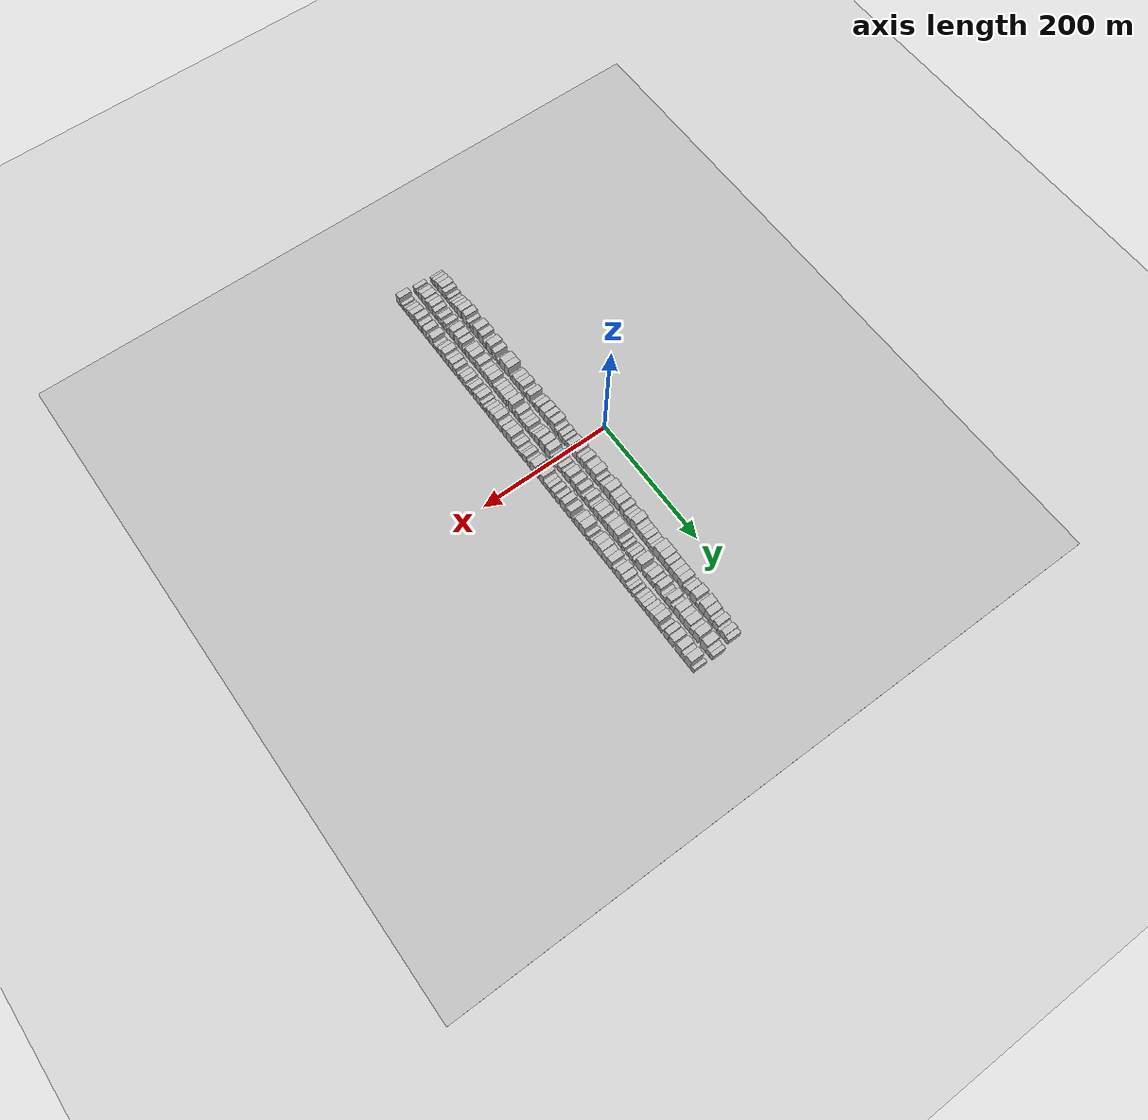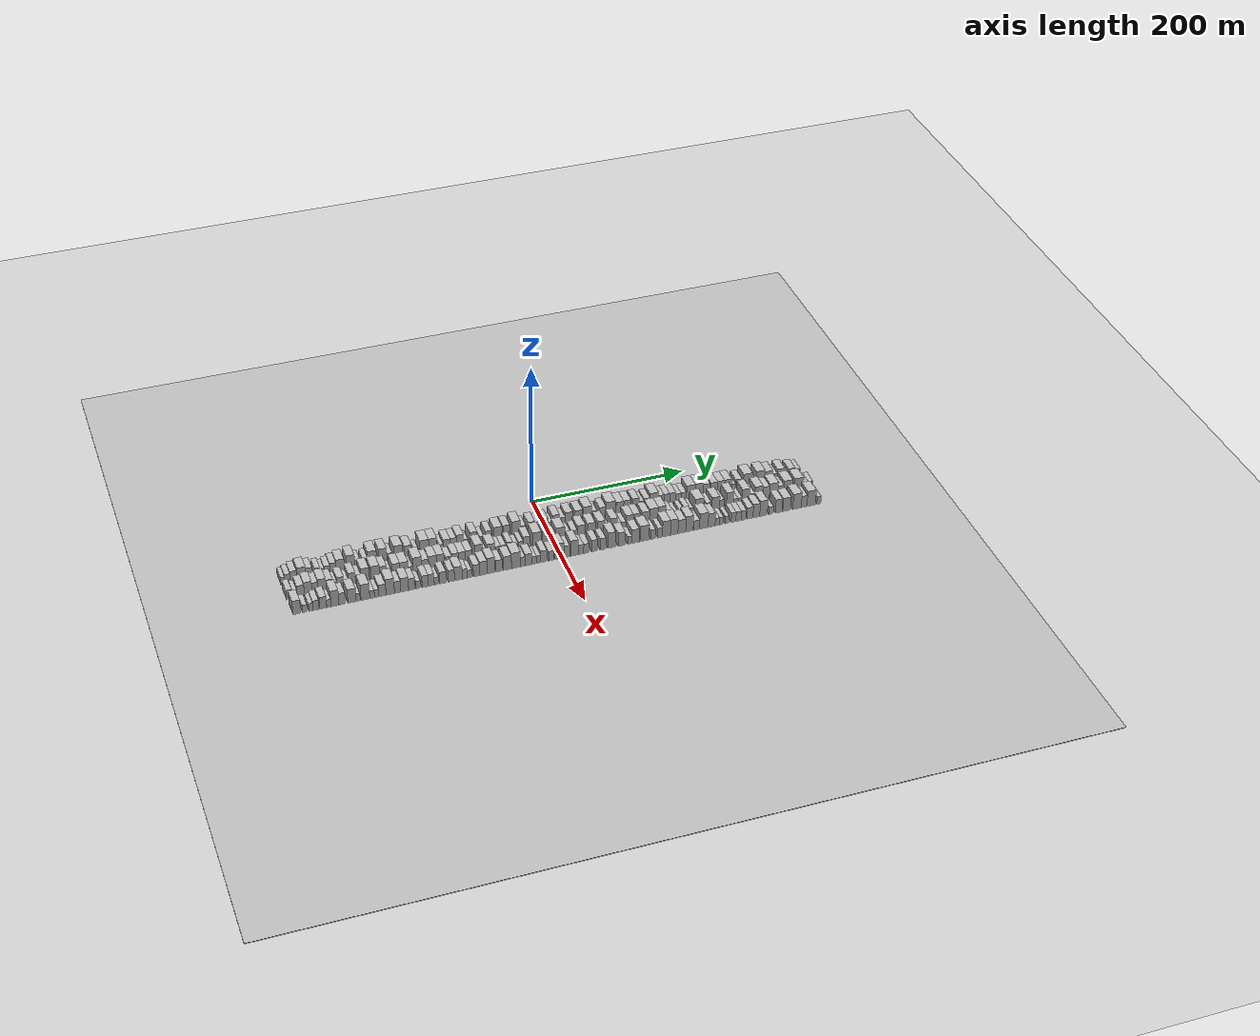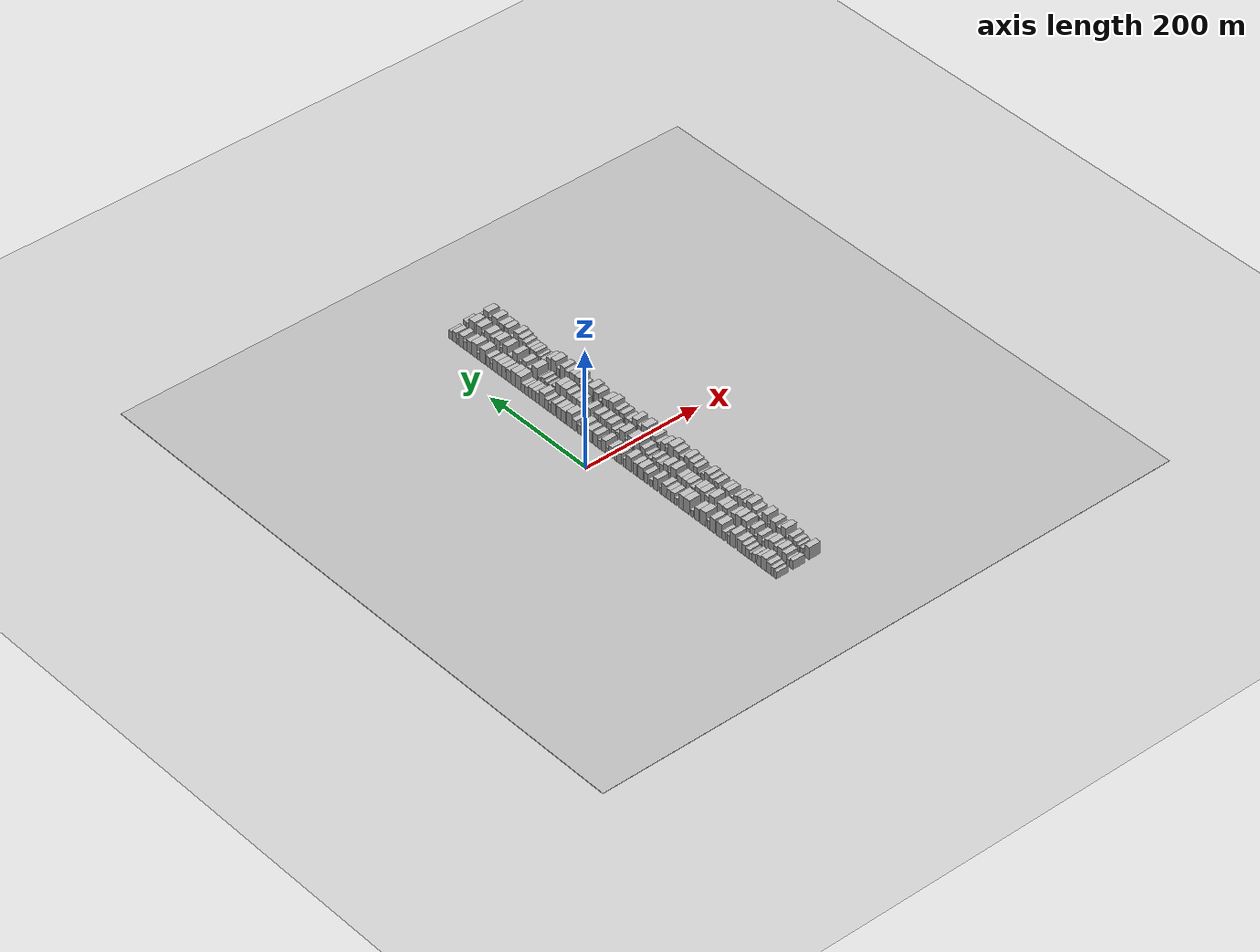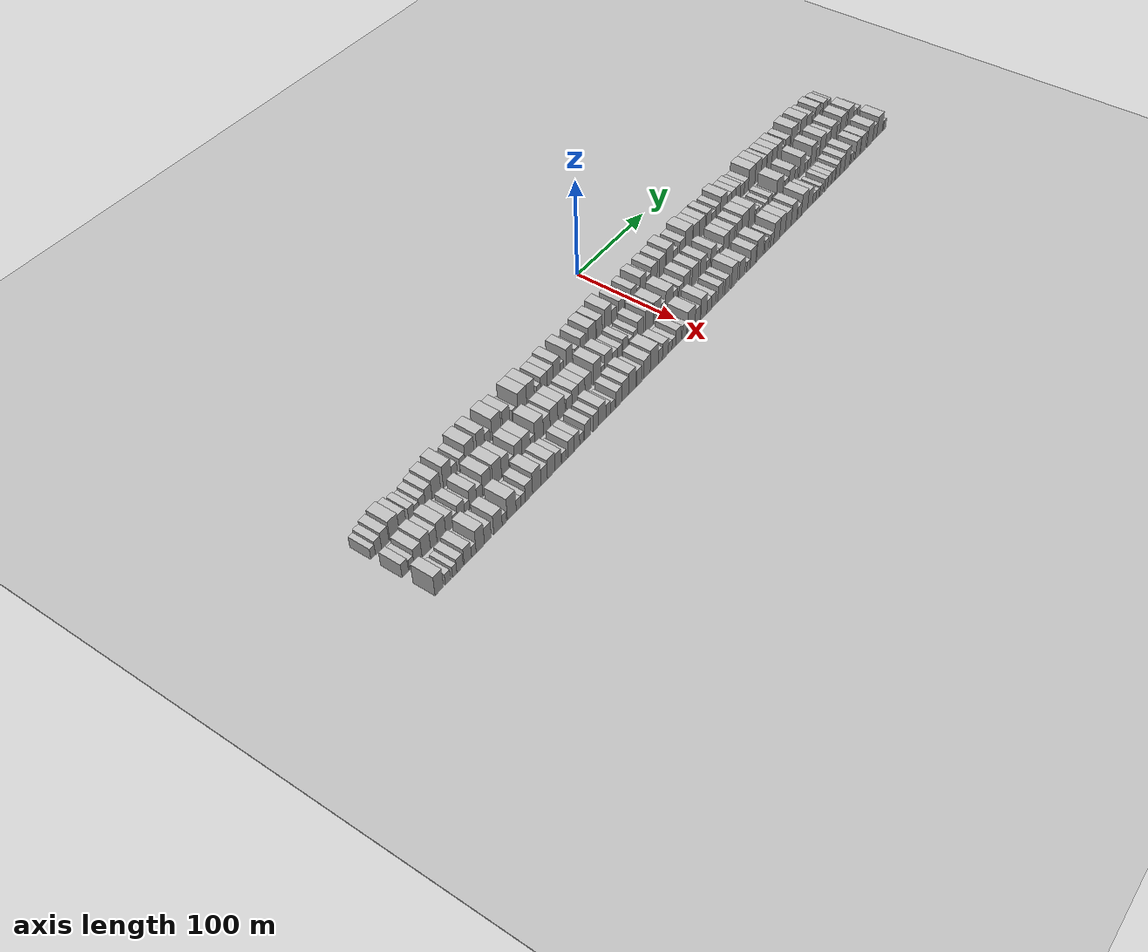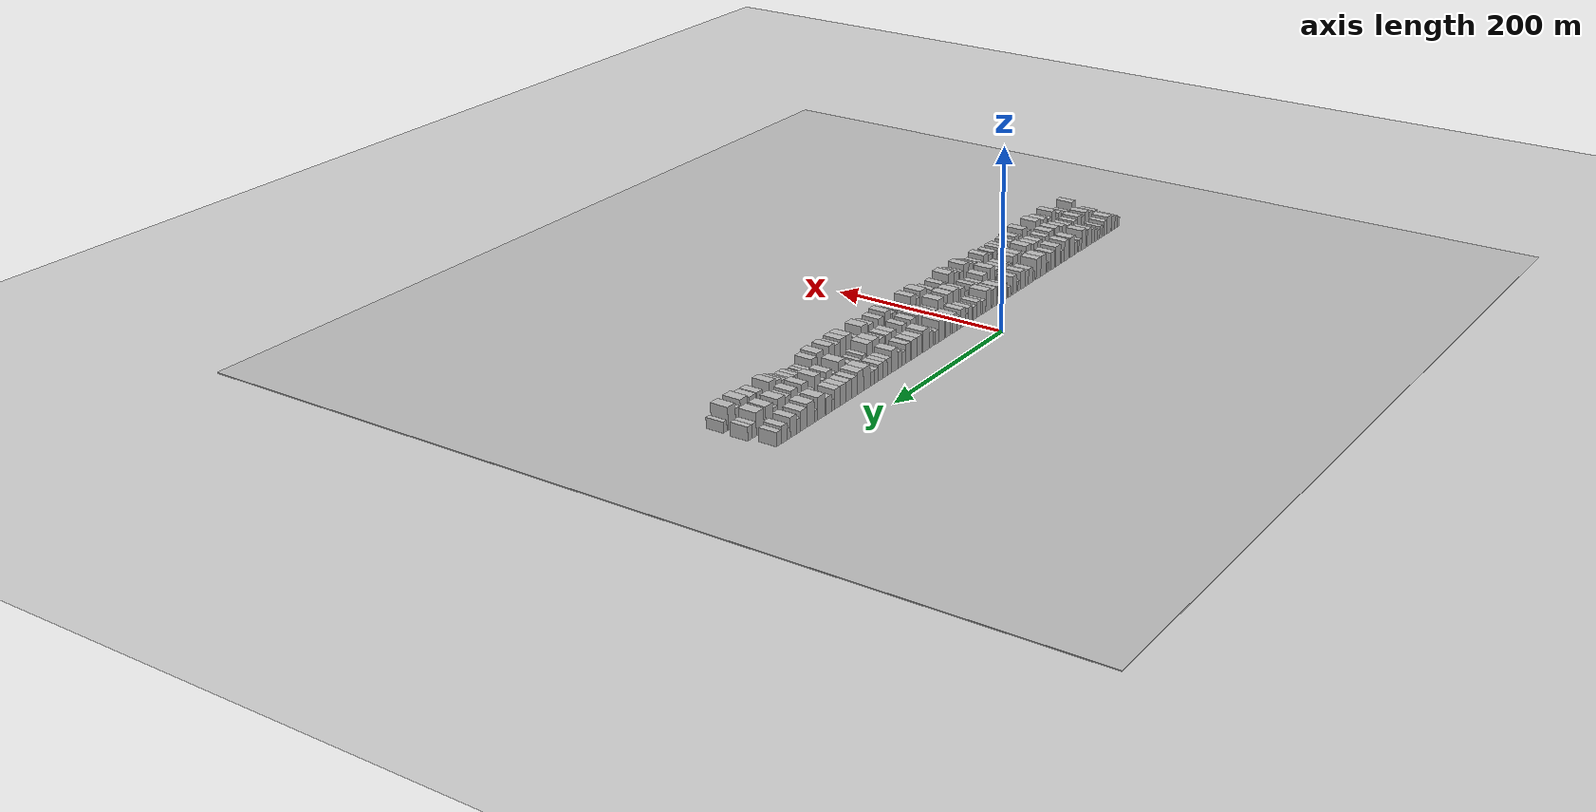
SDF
<?xml version="1.0" encoding="utf-8"?>

<sdf version="1.6">

   <world name="default">

      <gui fullscreen="0">

         <camera name="user_camera">

            <pose>-15 0 4.57585 0 0 0</pose>

            <view_controller>orbit</view_controller>

         </camera>

      </gui>

      <scene>

         <sky>

           <clouds>

             <speed>12</speed>

           </clouds>

         </sky>

         <ambient>0.4 0.4 0.4 1</ambient>

         <background>0.7 0.7 0.7 1</background>

         <shadows>1</shadows>

      </scene>

      <gravity>0 0 -9.8066</gravity>

      <magnetic_field>6e-06 2.3e-05 -4.2e-05</magnetic_field>

      <physics default="0" name="default_physics" type="ode">

         <ode>

            <solver>

               <type>quick</type>

               <iters>10</iters>

               <sor>1.0</sor>

               <use_dynamic_moi_rescaling>0</use_dynamic_moi_rescaling>

            </solver>

            <constraints>

               <cfm>0</cfm>

               <erp>0.2</erp>

               <contact_max_correcting_vel>100</contact_max_correcting_vel>

               <contact_surface_layer>0.001</contact_surface_layer>

            </constraints>

         </ode>

         <max_step_size>0.004</max_step_size>

         <real_time_factor>1</real_time_factor>

         <real_time_update_rate>250</real_time_update_rate>

      </physics>

      <light name="sun" type="directional">

         <cast_shadows>1</cast_shadows>

         <pose>0 0 10 0 0 0</pose>

         <diffuse>0.8 0.8 0.8 1</diffuse>

         <specular>0.2 0.2 0.2 1</specular>

         <attenuation>

            <range>1000</range>

            <constant>0.9</constant>

            <linear>0.01</linear>

            <quadratic>0.001</quadratic>

         </attenuation>

         <direction>-0.5 0.1 -0.9</direction>

      </light>

      <include>

         <name>ground_plane_1</name>

         <uri>model://HANNAS_ground_plane</uri>

         <pose>0 0 0  0 0 0</pose>

      </include>

      <include>

         <name>ground_plane_2</name>

         <uri>model://HANNAS_ground_plane</uri>

         <pose>100 0 0  0 0 0</pose>

      </include>

      <model name="building_1">

         <static>1</static>

         <pose frame="">50.0000 -333.4852 0 0.000000 0.000000 0.000000</pose>

         <link name="link">

            <pose frame="">0 0 6.00 0 0 0</pose>

            <collision name="collision">

               <geometry>

                  <box>

                     <size>20.0000 5.0296 12.0000</size>

                  </box>

               </geometry>

               <max_contacts>10</max_contacts>

               <surface>

                  <contact>

                     <ode/>

                  </contact>

                  <bounce/>

                  <friction>

                     <torsional>

                        <ode/>

                     </torsional>

                     <ode/>

                  </friction>

               </surface>

            </collision>

            <visual name="visual">

               <cast_shadows>0</cast_shadows>

               <geometry>

                  <box>

                     <size>20.0000 5.0296 12.0000</size>

                  </box>

               </geometry>

               <material>

                  <script>

                     <uri>model://HANNAS_wall/materials/scripts</uri>

                     <uri>model://HANNAS_wall/materials/textures</uri>

                     <name>vrc/HANNAS_wall</name>

                  </script>

               </material>

            </visual>

            <self_collide>0</self_collide>

            <enable_wind>0</enable_wind>

            <kinematic>0</kinematic>

         </link>

      </model>

      <model name="building_2">

         <static>1</static>

         <pose frame="">50.0000 -327.6248 0 0.000000 0.000000 0.000000</pose>

         <link name="link">

            <pose frame="">0 0 7.50 0 0 0</pose>

            <collision name="collision">

               <geometry>

                  <box>

                     <size>20.0000 6.6912 15.0000</size>

                  </box>

               </geometry>

               <max_contacts>10</max_contacts>

               <surface>

                  <contact>

                     <ode/>

                  </contact>

                  <bounce/>

                  <friction>

                     <torsional>

                        <ode/>

                     </torsional>

                     <ode/>

                  </friction>

               </surface>

            </collision>

            <visual name="visual">

               <cast_shadows>0</cast_shadows>

               <geometry>

                  <box>

                     <size>20.0000 6.6912 15.0000</size>

                  </box>

               </geometry>

               <material>

                  <script>

                     <uri>model://HANNAS_wall/materials/scripts</uri>

                     <uri>model://HANNAS_wall/materials/textures</uri>

                     <name>vrc/HANNAS_wall</name>

                  </script>

               </material>

            </visual>

            <self_collide>0</self_collide>

            <enable_wind>0</enable_wind>

            <kinematic>0</kinematic>

         </link>

      </model>

      <model name="building_3">

         <static>1</static>

         <pose frame="">50.0000 -320.2911 0 0.000000 0.000000 0.000000</pose>

         <link name="link">

            <pose frame="">0 0 9.00 0 0 0</pose>

            <collision name="collision">

               <geometry>

                  <box>

                     <size>20.0000 7.9762 18.0000</size>

                  </box>

               </geometry>

               <max_contacts>10</max_contacts>

               <surface>

                  <contact>

                     <ode/>

                  </contact>

                  <bounce/>

                  <friction>

                     <torsional>

                        <ode/>

                     </torsional>

                     <ode/>

                  </friction>

               </surface>

            </collision>

            <visual name="visual">

               <cast_shadows>0</cast_shadows>

               <geometry>

                  <box>

                     <size>20.0000 7.9762 18.0000</size>

                  </box>

               </geometry>

               <material>

                  <script>

                     <uri>model://HANNAS_wall/materials/scripts</uri>

                     <uri>model://HANNAS_wall/materials/textures</uri>

                     <name>vrc/HANNAS_wall</name>

                  </script>

               </material>

            </visual>

            <self_collide>0</self_collide>

            <enable_wind>0</enable_wind>

            <kinematic>0</kinematic>

         </link>

      </model>

      <model name="building_4">

         <static>1</static>

         <pose frame="">50.0000 -310.1145 0 0.000000 0.000000 0.000000</pose>

         <link name="link">

            <pose frame="">0 0 10.50 0 0 0</pose>

            <collision name="collision">

               <geometry>

                  <box>

                     <size>20.0000 10.3770 21.0000</size>

                  </box>

               </geometry>

               <max_contacts>10</max_contacts>

               <surface>

                  <contact>

                     <ode/>

                  </contact>

                  <bounce/>

                  <friction>

                     <torsional>

                        <ode/>

                     </torsional>

                     <ode/>

                  </friction>

               </surface>

            </collision>

            <visual name="visual">

               <cast_shadows>0</cast_shadows>

               <geometry>

                  <box>

                     <size>20.0000 10.3770 21.0000</size>

                  </box>

               </geometry>

               <material>

                  <script>

                     <uri>model://HANNAS_wall/materials/scripts</uri>

                     <uri>model://HANNAS_wall/materials/textures</uri>

                     <name>vrc/HANNAS_wall</name>

                  </script>

               </material>

            </visual>

            <self_collide>0</self_collide>

            <enable_wind>0</enable_wind>

            <kinematic>0</kinematic>

         </link>

      </model>

      <model name="building_5">

         <static>1</static>

         <pose frame="">50.0000 -301.0032 0 0.000000 0.000000 0.000000</pose>

         <link name="link">

            <pose frame="">0 0 9.00 0 0 0</pose>

            <collision name="collision">

               <geometry>

                  <box>

                     <size>20.0000 7.8455 18.0000</size>

                  </box>

               </geometry>

               <max_contacts>10</max_contacts>

               <surface>

                  <contact>

                     <ode/>

                  </contact>

                  <bounce/>

                  <friction>

                     <torsional>

                        <ode/>

                     </torsional>

                     <ode/>

                  </friction>

               </surface>

            </collision>

            <visual name="visual">

               <cast_shadows>0</cast_shadows>

               <geometry>

                  <box>

                     <size>20.0000 7.8455 18.0000</size>

                  </box>

               </geometry>

               <material>

                  <script>

                     <uri>model://HANNAS_wall/materials/scripts</uri>

                     <uri>model://HANNAS_wall/materials/textures</uri>

                     <name>vrc/HANNAS_wall</name>

                  </script>

               </material>

            </visual>

            <self_collide>0</self_collide>

            <enable_wind>0</enable_wind>

            <kinematic>0</kinematic>

         </link>

      </model>

      <model name="building_6">

         <static>1</static>

         <pose frame="">50.0000 -290.8323 0 0.000000 0.000000 0.000000</pose>

         <link name="link">

            <pose frame="">0 0 7.50 0 0 0</pose>

            <collision name="collision">

               <geometry>

                  <box>

                     <size>20.0000 6.4964 15.0000</size>

                  </box>

               </geometry>

               <max_contacts>10</max_contacts>

               <surface>

                  <contact>

                     <ode/>

                  </contact>

                  <bounce/>

                  <friction>

                     <torsional>

                        <ode/>

                     </torsional>

                     <ode/>

                  </friction>

               </surface>

            </collision>

            <visual name="visual">

               <cast_shadows>0</cast_shadows>

               <geometry>

                  <box>

                     <size>20.0000 6.4964 15.0000</size>

                  </box>

               </geometry>

               <material>

                  <script>

                     <uri>model://HANNAS_wall/materials/scripts</uri>

                     <uri>model://HANNAS_wall/materials/textures</uri>

                     <name>vrc/HANNAS_wall</name>

                  </script>

               </material>

            </visual>

            <self_collide>0</self_collide>

            <enable_wind>0</enable_wind>

            <kinematic>0</kinematic>

         </link>

      </model>

      <model name="building_7">

         <static>1</static>

         <pose frame="">50.0000 -284.9107 0 0.000000 0.000000 0.000000</pose>

         <link name="link">

            <pose frame="">0 0 6.00 0 0 0</pose>

            <collision name="collision">

               <geometry>

                  <box>

                     <size>20.0000 5.3466 12.0000</size>

                  </box>

               </geometry>

               <max_contacts>10</max_contacts>

               <surface>

                  <contact>

                     <ode/>

                  </contact>

                  <bounce/>

                  <friction>

                     <torsional>

                        <ode/>

                     </torsional>

                     <ode/>

                  </friction>

               </surface>

            </collision>

            <visual name="visual">

               <cast_shadows>0</cast_shadows>

               <geometry>

                  <box>

                     <size>20.0000 5.3466 12.0000</size>

                  </box>

               </geometry>

               <material>

                  <script>

                     <uri>model://HANNAS_wall/materials/scripts</uri>

                     <uri>model://HANNAS_wall/materials/textures</uri>

                     <name>vrc/HANNAS_wall</name>

                  </script>

               </material>

            </visual>

            <self_collide>0</self_collide>

            <enable_wind>0</enable_wind>

            <kinematic>0</kinematic>

         </link>

      </model>

      <model name="building_8">

         <static>1</static>

         <pose frame="">50.0000 -278.7191 0 0.000000 0.000000 0.000000</pose>

         <link name="link">

            <pose frame="">0 0 7.50 0 0 0</pose>

            <collision name="collision">

               <geometry>

                  <box>

                     <size>20.0000 7.0367 15.0000</size>

                  </box>

               </geometry>

               <max_contacts>10</max_contacts>

               <surface>

                  <contact>

                     <ode/>

                  </contact>

                  <bounce/>

                  <friction>

                     <torsional>

                        <ode/>

                     </torsional>

                     <ode/>

                  </friction>

               </surface>

            </collision>

            <visual name="visual">

               <cast_shadows>0</cast_shadows>

               <geometry>

                  <box>

                     <size>20.0000 7.0367 15.0000</size>

                  </box>

               </geometry>

               <material>

                  <script>

                     <uri>model://HANNAS_wall/materials/scripts</uri>

                     <uri>model://HANNAS_wall/materials/textures</uri>

                     <name>vrc/HANNAS_wall</name>

                  </script>

               </material>

            </visual>

            <self_collide>0</self_collide>

            <enable_wind>0</enable_wind>

            <kinematic>0</kinematic>

         </link>

      </model>

      <model name="building_9">

         <static>1</static>

         <pose frame="">50.0000 -271.3886 0 0.000000 0.000000 0.000000</pose>

         <link name="link">

            <pose frame="">0 0 9.00 0 0 0</pose>

            <collision name="collision">

               <geometry>

                  <box>

                     <size>20.0000 7.6242 18.0000</size>

                  </box>

               </geometry>

               <max_contacts>10</max_contacts>

               <surface>

                  <contact>

                     <ode/>

                  </contact>

                  <bounce/>

                  <friction>

                     <torsional>

                        <ode/>

                     </torsional>

                     <ode/>

                  </friction>

               </surface>

            </collision>

            <visual name="visual">

               <cast_shadows>0</cast_shadows>

               <geometry>

                  <box>

                     <size>20.0000 7.6242 18.0000</size>

                  </box>

               </geometry>

               <material>

                  <script>

                     <uri>model://HANNAS_wall/materials/scripts</uri>

                     <uri>model://HANNAS_wall/materials/textures</uri>

                     <name>vrc/HANNAS_wall</name>

                  </script>

               </material>

            </visual>

            <self_collide>0</self_collide>

            <enable_wind>0</enable_wind>

            <kinematic>0</kinematic>

         </link>

      </model>

      <model name="building_10">

         <static>1</static>

         <pose frame="">50.0000 -262.5840 0 0.000000 0.000000 0.000000</pose>

         <link name="link">

            <pose frame="">0 0 10.50 0 0 0</pose>

            <collision name="collision">

               <geometry>

                  <box>

                     <size>20.0000 9.9851 21.0000</size>

                  </box>

               </geometry>

               <max_contacts>10</max_contacts>

               <surface>

                  <contact>

                     <ode/>

                  </contact>

                  <bounce/>

                  <friction>

                     <torsional>

                        <ode/>

                     </torsional>

                     <ode/>

                  </friction>

               </surface>

            </collision>

            <visual name="visual">

               <cast_shadows>0</cast_shadows>

               <geometry>

                  <box>

                     <size>20.0000 9.9851 21.0000</size>

                  </box>

               </geometry>

               <material>

                  <script>

                     <uri>model://HANNAS_wall/materials/scripts</uri>

                     <uri>model://HANNAS_wall/materials/textures</uri>

                     <name>vrc/HANNAS_wall</name>

                  </script>

               </material>

            </visual>

            <self_collide>0</self_collide>

            <enable_wind>0</enable_wind>

            <kinematic>0</kinematic>

         </link>

      </model>

      <model name="building_11">

         <static>1</static>

         <pose frame="">50.0000 -249.5773 0 0.000000 0.000000 0.000000</pose>

         <link name="link">

            <pose frame="">0 0 12.00 0 0 0</pose>

            <collision name="collision">

               <geometry>

                  <box>

                     <size>20.0000 10.0284 24.0000</size>

                  </box>

               </geometry>

               <max_contacts>10</max_contacts>

               <surface>

                  <contact>

                     <ode/>

                  </contact>

                  <bounce/>

                  <friction>

                     <torsional>

                        <ode/>

                     </torsional>

                     <ode/>

                  </friction>

               </surface>

            </collision>

            <visual name="visual">

               <cast_shadows>0</cast_shadows>

               <geometry>

                  <box>

                     <size>20.0000 10.0284 24.0000</size>

                  </box>

               </geometry>

               <material>

                  <script>

                     <uri>model://HANNAS_wall/materials/scripts</uri>

                     <uri>model://HANNAS_wall/materials/textures</uri>

                     <name>vrc/HANNAS_wall</name>

                  </script>

               </material>

            </visual>

            <self_collide>0</self_collide>

            <enable_wind>0</enable_wind>

            <kinematic>0</kinematic>

         </link>

      </model>

      <model name="building_12">

         <static>1</static>

         <pose frame="">50.0000 -241.2419 0 0.000000 0.000000 0.000000</pose>

         <link name="link">

            <pose frame="">0 0 7.50 0 0 0</pose>

            <collision name="collision">

               <geometry>

                  <box>

                     <size>20.0000 6.6423 15.0000</size>

                  </box>

               </geometry>

               <max_contacts>10</max_contacts>

               <surface>

                  <contact>

                     <ode/>

                  </contact>

                  <bounce/>

                  <friction>

                     <torsional>

                        <ode/>

                     </torsional>

                     <ode/>

                  </friction>

               </surface>

            </collision>

            <visual name="visual">

               <cast_shadows>0</cast_shadows>

               <geometry>

                  <box>

                     <size>20.0000 6.6423 15.0000</size>

                  </box>

               </geometry>

               <material>

                  <script>

                     <uri>model://HANNAS_wall/materials/scripts</uri>

                     <uri>model://HANNAS_wall/materials/textures</uri>

                     <name>vrc/HANNAS_wall</name>

                  </script>

               </material>

            </visual>

            <self_collide>0</self_collide>

            <enable_wind>0</enable_wind>

            <kinematic>0</kinematic>

         </link>

      </model>

      <model name="building_13">

         <static>1</static>

         <pose frame="">50.0000 -231.6286 0 0.000000 0.000000 0.000000</pose>

         <link name="link">

            <pose frame="">0 0 7.50 0 0 0</pose>

            <collision name="collision">

               <geometry>

                  <box>

                     <size>20.0000 6.5844 15.0000</size>

                  </box>

               </geometry>

               <max_contacts>10</max_contacts>

               <surface>

                  <contact>

                     <ode/>

                  </contact>

                  <bounce/>

                  <friction>

                     <torsional>

                        <ode/>

                     </torsional>

                     <ode/>

                  </friction>

               </surface>

            </collision>

            <visual name="visual">

               <cast_shadows>0</cast_shadows>

               <geometry>

                  <box>

                     <size>20.0000 6.5844 15.0000</size>

                  </box>

               </geometry>

               <material>

                  <script>

                     <uri>model://HANNAS_wall/materials/scripts</uri>

                     <uri>model://HANNAS_wall/materials/textures</uri>

                     <name>vrc/HANNAS_wall</name>

                  </script>

               </material>

            </visual>

            <self_collide>0</self_collide>

            <enable_wind>0</enable_wind>

            <kinematic>0</kinematic>

         </link>

      </model>

      <model name="building_14">

         <static>1</static>

         <pose frame="">50.0000 -222.8365 0 0.000000 0.000000 0.000000</pose>

         <link name="link">

            <pose frame="">0 0 12.00 0 0 0</pose>

            <collision name="collision">

               <geometry>

                  <box>

                     <size>20.0000 10.9997 24.0000</size>

                  </box>

               </geometry>

               <max_contacts>10</max_contacts>

               <surface>

                  <contact>

                     <ode/>

                  </contact>

                  <bounce/>

                  <friction>

                     <torsional>

                        <ode/>

                     </torsional>

                     <ode/>

                  </friction>

               </surface>

            </collision>

            <visual name="visual">

               <cast_shadows>0</cast_shadows>

               <geometry>

                  <box>

                     <size>20.0000 10.9997 24.0000</size>

                  </box>

               </geometry>

               <material>

                  <script>

                     <uri>model://HANNAS_wall/materials/scripts</uri>

                     <uri>model://HANNAS_wall/materials/textures</uri>

                     <name>vrc/HANNAS_wall</name>

                  </script>

               </material>

            </visual>

            <self_collide>0</self_collide>

            <enable_wind>0</enable_wind>

            <kinematic>0</kinematic>

         </link>

      </model>

      <model name="building_15">

         <static>1</static>

         <pose frame="">50.0000 -209.4388 0 0.000000 0.000000 0.000000</pose>

         <link name="link">

            <pose frame="">0 0 12.00 0 0 0</pose>

            <collision name="collision">

               <geometry>

                  <box>

                     <size>20.0000 9.7958 24.0000</size>

                  </box>

               </geometry>

               <max_contacts>10</max_contacts>

               <surface>

                  <contact>

                     <ode/>

                  </contact>

                  <bounce/>

                  <friction>

                     <torsional>

                        <ode/>

                     </torsional>

                     <ode/>

                  </friction>

               </surface>

            </collision>

            <visual name="visual">

               <cast_shadows>0</cast_shadows>

               <geometry>

                  <box>

                     <size>20.0000 9.7958 24.0000</size>

                  </box>

               </geometry>

               <material>

                  <script>

                     <uri>model://HANNAS_wall/materials/scripts</uri>

                     <uri>model://HANNAS_wall/materials/textures</uri>

                     <name>vrc/HANNAS_wall</name>

                  </script>

               </material>

            </visual>

            <self_collide>0</self_collide>

            <enable_wind>0</enable_wind>

            <kinematic>0</kinematic>

         </link>

      </model>

      <model name="building_16">

         <static>1</static>

         <pose frame="">50.0000 -201.1808 0 0.000000 0.000000 0.000000</pose>

         <link name="link">

            <pose frame="">0 0 7.50 0 0 0</pose>

            <collision name="collision">

               <geometry>

                  <box>

                     <size>20.0000 6.7202 15.0000</size>

                  </box>

               </geometry>

               <max_contacts>10</max_contacts>

               <surface>

                  <contact>

                     <ode/>

                  </contact>

                  <bounce/>

                  <friction>

                     <torsional>

                        <ode/>

                     </torsional>

                     <ode/>

                  </friction>

               </surface>

            </collision>

            <visual name="visual">

               <cast_shadows>0</cast_shadows>

               <geometry>

                  <box>

                     <size>20.0000 6.7202 15.0000</size>

                  </box>

               </geometry>

               <material>

                  <script>

                     <uri>model://HANNAS_wall/materials/scripts</uri>

                     <uri>model://HANNAS_wall/materials/textures</uri>

                     <name>vrc/HANNAS_wall</name>

                  </script>

               </material>

            </visual>

            <self_collide>0</self_collide>

            <enable_wind>0</enable_wind>

            <kinematic>0</kinematic>

         </link>

      </model>

      <model name="building_17">

         <static>1</static>

         <pose frame="">50.0000 -190.1766 0 0.000000 0.000000 0.000000</pose>

         <link name="link">

            <pose frame="">0 0 12.00 0 0 0</pose>

            <collision name="collision">

               <geometry>

                  <box>

                     <size>20.0000 11.2882 24.0000</size>

                  </box>

               </geometry>

               <max_contacts>10</max_contacts>

               <surface>

                  <contact>

                     <ode/>

                  </contact>

                  <bounce/>

                  <friction>

                     <torsional>

                        <ode/>

                     </torsional>

                     <ode/>

                  </friction>

               </surface>

            </collision>

            <visual name="visual">

               <cast_shadows>0</cast_shadows>

               <geometry>

                  <box>

                     <size>20.0000 11.2882 24.0000</size>

                  </box>

               </geometry>

               <material>

                  <script>

                     <uri>model://HANNAS_wall/materials/scripts</uri>

                     <uri>model://HANNAS_wall/materials/textures</uri>

                     <name>vrc/HANNAS_wall</name>

                  </script>

               </material>

            </visual>

            <self_collide>0</self_collide>

            <enable_wind>0</enable_wind>

            <kinematic>0</kinematic>

         </link>

      </model>

      <model name="building_18">

         <static>1</static>

         <pose frame="">50.0000 -177.9957 0 0.000000 0.000000 0.000000</pose>

         <link name="link">

            <pose frame="">0 0 10.50 0 0 0</pose>

            <collision name="collision">

               <geometry>

                  <box>

                     <size>20.0000 9.0736 21.0000</size>

                  </box>

               </geometry>

               <max_contacts>10</max_contacts>

               <surface>

                  <contact>

                     <ode/>

                  </contact>

                  <bounce/>

                  <friction>

                     <torsional>

                        <ode/>

                     </torsional>

                     <ode/>

                  </friction>

               </surface>

            </collision>

            <visual name="visual">

               <cast_shadows>0</cast_shadows>

               <geometry>

                  <box>

                     <size>20.0000 9.0736 21.0000</size>

                  </box>

               </geometry>

               <material>

                  <script>

                     <uri>model://HANNAS_wall/materials/scripts</uri>

                     <uri>model://HANNAS_wall/materials/textures</uri>

                     <name>vrc/HANNAS_wall</name>

                  </script>

               </material>

            </visual>

            <self_collide>0</self_collide>

            <enable_wind>0</enable_wind>

            <kinematic>0</kinematic>

         </link>

      </model>

      <model name="building_19">

         <static>1</static>

         <pose frame="">50.0000 -167.7257 0 0.000000 0.000000 0.000000</pose>

         <link name="link">

            <pose frame="">0 0 6.00 0 0 0</pose>

            <collision name="collision">

               <geometry>

                  <box>

                     <size>20.0000 5.4664 12.0000</size>

                  </box>

               </geometry>

               <max_contacts>10</max_contacts>

               <surface>

                  <contact>

                     <ode/>

                  </contact>

                  <bounce/>

                  <friction>

                     <torsional>

                        <ode/>

                     </torsional>

                     <ode/>

                  </friction>

               </surface>

            </collision>

            <visual name="visual">

               <cast_shadows>0</cast_shadows>

               <geometry>

                  <box>

                     <size>20.0000 5.4664 12.0000</size>

                  </box>

               </geometry>

               <material>

                  <script>

                     <uri>model://HANNAS_wall/materials/scripts</uri>

                     <uri>model://HANNAS_wall/materials/textures</uri>

                     <name>vrc/HANNAS_wall</name>

                  </script>

               </material>

            </visual>

            <self_collide>0</self_collide>

            <enable_wind>0</enable_wind>

            <kinematic>0</kinematic>

         </link>

      </model>

      <model name="building_20">

         <static>1</static>

         <pose frame="">50.0000 -157.3953 0 0.000000 0.000000 0.000000</pose>

         <link name="link">

            <pose frame="">0 0 12.00 0 0 0</pose>

            <collision name="collision">

               <geometry>

                  <box>

                     <size>20.0000 11.1945 24.0000</size>

                  </box>

               </geometry>

               <max_contacts>10</max_contacts>

               <surface>

                  <contact>

                     <ode/>

                  </contact>

                  <bounce/>

                  <friction>

                     <torsional>

                        <ode/>

                     </torsional>

                     <ode/>

                  </friction>

               </surface>

            </collision>

            <visual name="visual">

               <cast_shadows>0</cast_shadows>

               <geometry>

                  <box>

                     <size>20.0000 11.1945 24.0000</size>

                  </box>

               </geometry>

               <material>

                  <script>

                     <uri>model://HANNAS_wall/materials/scripts</uri>

                     <uri>model://HANNAS_wall/materials/textures</uri>

                     <name>vrc/HANNAS_wall</name>

                  </script>

               </material>

            </visual>

            <self_collide>0</self_collide>

            <enable_wind>0</enable_wind>

            <kinematic>0</kinematic>

         </link>

      </model>

      <model name="building_21">

         <static>1</static>

         <pose frame="">50.0000 -146.7273 0 0.000000 0.000000 0.000000</pose>

         <link name="link">

            <pose frame="">0 0 12.00 0 0 0</pose>

            <collision name="collision">

               <geometry>

                  <box>

                     <size>20.0000 10.1413 24.0000</size>

                  </box>

               </geometry>

               <max_contacts>10</max_contacts>

               <surface>

                  <contact>

                     <ode/>

                  </contact>

                  <bounce/>

                  <friction>

                     <torsional>

                        <ode/>

                     </torsional>

                     <ode/>

                  </friction>

               </surface>

            </collision>

            <visual name="visual">

               <cast_shadows>0</cast_shadows>

               <geometry>

                  <box>

                     <size>20.0000 10.1413 24.0000</size>

                  </box>

               </geometry>

               <material>

                  <script>

                     <uri>model://HANNAS_wall/materials/scripts</uri>

                     <uri>model://HANNAS_wall/materials/textures</uri>

                     <name>vrc/HANNAS_wall</name>

                  </script>

               </material>

            </visual>

            <self_collide>0</self_collide>

            <enable_wind>0</enable_wind>

            <kinematic>0</kinematic>

         </link>

      </model>

      <model name="building_22">

         <static>1</static>

         <pose frame="">50.0000 -136.1086 0 0.000000 0.000000 0.000000</pose>

         <link name="link">

            <pose frame="">0 0 6.00 0 0 0</pose>

            <collision name="collision">

               <geometry>

                  <box>

                     <size>20.0000 5.0961 12.0000</size>

                  </box>

               </geometry>

               <max_contacts>10</max_contacts>

               <surface>

                  <contact>

                     <ode/>

                  </contact>

                  <bounce/>

                  <friction>

                     <torsional>

                        <ode/>

                     </torsional>

                     <ode/>

                  </friction>

               </surface>

            </collision>

            <visual name="visual">

               <cast_shadows>0</cast_shadows>

               <geometry>

                  <box>

                     <size>20.0000 5.0961 12.0000</size>

                  </box>

               </geometry>

               <material>

                  <script>

                     <uri>model://HANNAS_wall/materials/scripts</uri>

                     <uri>model://HANNAS_wall/materials/textures</uri>

                     <name>vrc/HANNAS_wall</name>

                  </script>

               </material>

            </visual>

            <self_collide>0</self_collide>

            <enable_wind>0</enable_wind>

            <kinematic>0</kinematic>

         </link>

      </model>

      <model name="building_23">

         <static>1</static>

         <pose frame="">50.0000 -129.1905 0 0.000000 0.000000 0.000000</pose>

         <link name="link">

            <pose frame="">0 0 9.00 0 0 0</pose>

            <collision name="collision">

               <geometry>

                  <box>

                     <size>20.0000 8.7401 18.0000</size>

                  </box>

               </geometry>

               <max_contacts>10</max_contacts>

               <surface>

                  <contact>

                     <ode/>

                  </contact>

                  <bounce/>

                  <friction>

                     <torsional>

                        <ode/>

                     </torsional>

                     <ode/>

                  </friction>

               </surface>

            </collision>

            <visual name="visual">

               <cast_shadows>0</cast_shadows>

               <geometry>

                  <box>

                     <size>20.0000 8.7401 18.0000</size>

                  </box>

               </geometry>

               <material>

                  <script>

                     <uri>model://HANNAS_wall/materials/scripts</uri>

                     <uri>model://HANNAS_wall/materials/textures</uri>

                     <name>vrc/HANNAS_wall</name>

                  </script>

               </material>

            </visual>

            <self_collide>0</self_collide>

            <enable_wind>0</enable_wind>

            <kinematic>0</kinematic>

         </link>

      </model>

      <model name="building_24">

         <static>1</static>

         <pose frame="">50.0000 -120.9280 0 0.000000 0.000000 0.000000</pose>

         <link name="link">

            <pose frame="">0 0 9.00 0 0 0</pose>

            <collision name="collision">

               <geometry>

                  <box>

                     <size>20.0000 7.7850 18.0000</size>

                  </box>

               </geometry>

               <max_contacts>10</max_contacts>

               <surface>

                  <contact>

                     <ode/>

                  </contact>

                  <bounce/>

                  <friction>

                     <torsional>

                        <ode/>

                     </torsional>

                     <ode/>

                  </friction>

               </surface>

            </collision>

            <visual name="visual">

               <cast_shadows>0</cast_shadows>

               <geometry>

                  <box>

                     <size>20.0000 7.7850 18.0000</size>

                  </box>

               </geometry>

               <material>

                  <script>

                     <uri>model://HANNAS_wall/materials/scripts</uri>

                     <uri>model://HANNAS_wall/materials/textures</uri>

                     <name>vrc/HANNAS_wall</name>

                  </script>

               </material>

            </visual>

            <self_collide>0</self_collide>

            <enable_wind>0</enable_wind>

            <kinematic>0</kinematic>

         </link>

      </model>

      <model name="building_25">

         <static>1</static>

         <pose frame="">50.0000 -112.3726 0 0.000000 0.000000 0.000000</pose>

         <link name="link">

            <pose frame="">0 0 10.50 0 0 0</pose>

            <collision name="collision">

               <geometry>

                  <box>

                     <size>20.0000 9.3259 21.0000</size>

                  </box>

               </geometry>

               <max_contacts>10</max_contacts>

               <surface>

                  <contact>

                     <ode/>

                  </contact>

                  <bounce/>

                  <friction>

                     <torsional>

                        <ode/>

                     </torsional>

                     <ode/>

                  </friction>

               </surface>

            </collision>

            <visual name="visual">

               <cast_shadows>0</cast_shadows>

               <geometry>

                  <box>

                     <size>20.0000 9.3259 21.0000</size>

                  </box>

               </geometry>

               <material>

                  <script>

                     <uri>model://HANNAS_wall/materials/scripts</uri>

                     <uri>model://HANNAS_wall/materials/textures</uri>

                     <name>vrc/HANNAS_wall</name>

                  </script>

               </material>

            </visual>

            <self_collide>0</self_collide>

            <enable_wind>0</enable_wind>

            <kinematic>0</kinematic>

         </link>

      </model>

      <model name="building_26">

         <static>1</static>

         <pose frame="">50.0000 -105.0843 0 0.000000 0.000000 0.000000</pose>

         <link name="link">

            <pose frame="">0 0 6.00 0 0 0</pose>

            <collision name="collision">

               <geometry>

                  <box>

                     <size>20.0000 5.2507 12.0000</size>

                  </box>

               </geometry>

               <max_contacts>10</max_contacts>

               <surface>

                  <contact>

                     <ode/>

                  </contact>

                  <bounce/>

                  <friction>

                     <torsional>

                        <ode/>

                     </torsional>

                     <ode/>

                  </friction>

               </surface>

            </collision>

            <visual name="visual">

               <cast_shadows>0</cast_shadows>

               <geometry>

                  <box>

                     <size>20.0000 5.2507 12.0000</size>

                  </box>

               </geometry>

               <material>

                  <script>

                     <uri>model://HANNAS_wall/materials/scripts</uri>

                     <uri>model://HANNAS_wall/materials/textures</uri>

                     <name>vrc/HANNAS_wall</name>

                  </script>

               </material>

            </visual>

            <self_collide>0</self_collide>

            <enable_wind>0</enable_wind>

            <kinematic>0</kinematic>

         </link>

      </model>

      <model name="building_27">

         <static>1</static>

         <pose frame="">50.0000 -95.0004 0 0.000000 0.000000 0.000000</pose>

         <link name="link">

            <pose frame="">0 0 10.50 0 0 0</pose>

            <collision name="collision">

               <geometry>

                  <box>

                     <size>20.0000 8.9172 21.0000</size>

                  </box>

               </geometry>

               <max_contacts>10</max_contacts>

               <surface>

                  <contact>

                     <ode/>

                  </contact>

                  <bounce/>

                  <friction>

                     <torsional>

                        <ode/>

                     </torsional>

                     <ode/>

                  </friction>

               </surface>

            </collision>

            <visual name="visual">

               <cast_shadows>0</cast_shadows>

               <geometry>

                  <box>

                     <size>20.0000 8.9172 21.0000</size>

                  </box>

               </geometry>

               <material>

                  <script>

                     <uri>model://HANNAS_wall/materials/scripts</uri>

                     <uri>model://HANNAS_wall/materials/textures</uri>

                     <name>vrc/HANNAS_wall</name>

                  </script>

               </material>

            </visual>

            <self_collide>0</self_collide>

            <enable_wind>0</enable_wind>

            <kinematic>0</kinematic>

         </link>

      </model>

      <model name="building_28">

         <static>1</static>

         <pose frame="">50.0000 -84.7550 0 0.000000 0.000000 0.000000</pose>

         <link name="link">

            <pose frame="">0 0 6.00 0 0 0</pose>

            <collision name="collision">

               <geometry>

                  <box>

                     <size>20.0000 5.5736 12.0000</size>

                  </box>

               </geometry>

               <max_contacts>10</max_contacts>

               <surface>

                  <contact>

                     <ode/>

                  </contact>

                  <bounce/>

                  <friction>

                     <torsional>

                        <ode/>

                     </torsional>

                     <ode/>

                  </friction>

               </surface>

            </collision>

            <visual name="visual">

               <cast_shadows>0</cast_shadows>

               <geometry>

                  <box>

                     <size>20.0000 5.5736 12.0000</size>

                  </box>

               </geometry>

               <material>

                  <script>

                     <uri>model://HANNAS_wall/materials/scripts</uri>

                     <uri>model://HANNAS_wall/materials/textures</uri>

                     <name>vrc/HANNAS_wall</name>

                  </script>

               </material>

            </visual>

            <self_collide>0</self_collide>

            <enable_wind>0</enable_wind>

            <kinematic>0</kinematic>

         </link>

      </model>

      <model name="building_29">

         <static>1</static>

         <pose frame="">50.0000 -76.0003 0 0.000000 0.000000 0.000000</pose>

         <link name="link">

            <pose frame="">0 0 9.00 0 0 0</pose>

            <collision name="collision">

               <geometry>

                  <box>

                     <size>20.0000 7.9358 18.0000</size>

                  </box>

               </geometry>

               <max_contacts>10</max_contacts>

               <surface>

                  <contact>

                     <ode/>

                  </contact>

                  <bounce/>

                  <friction>

                     <torsional>

                        <ode/>

                     </torsional>

                     <ode/>

                  </friction>

               </surface>

            </collision>

            <visual name="visual">

               <cast_shadows>0</cast_shadows>

               <geometry>

                  <box>

                     <size>20.0000 7.9358 18.0000</size>

                  </box>

               </geometry>

               <material>

                  <script>

                     <uri>model://HANNAS_wall/materials/scripts</uri>

                     <uri>model://HANNAS_wall/materials/textures</uri>

                     <name>vrc/HANNAS_wall</name>

                  </script>

               </material>

            </visual>

            <self_collide>0</self_collide>

            <enable_wind>0</enable_wind>

            <kinematic>0</kinematic>

         </link>

      </model>

      <model name="building_30">

         <static>1</static>

         <pose frame="">50.0000 -63.7899 0 0.000000 0.000000 0.000000</pose>

         <link name="link">

            <pose frame="">0 0 10.50 0 0 0</pose>

            <collision name="collision">

               <geometry>

                  <box>

                     <size>20.0000 10.4850 21.0000</size>

                  </box>

               </geometry>

               <max_contacts>10</max_contacts>

               <surface>

                  <contact>

                     <ode/>

                  </contact>

                  <bounce/>

                  <friction>

                     <torsional>

                        <ode/>

                     </torsional>

                     <ode/>

                  </friction>

               </surface>

            </collision>

            <visual name="visual">

               <cast_shadows>0</cast_shadows>

               <geometry>

                  <box>

                     <size>20.0000 10.4850 21.0000</size>

                  </box>

               </geometry>

               <material>

                  <script>

                     <uri>model://HANNAS_wall/materials/scripts</uri>

                     <uri>model://HANNAS_wall/materials/textures</uri>

                     <name>vrc/HANNAS_wall</name>

                  </script>

               </material>

            </visual>

            <self_collide>0</self_collide>

            <enable_wind>0</enable_wind>

            <kinematic>0</kinematic>

         </link>

      </model>

      <model name="building_31">

         <static>1</static>

         <pose frame="">50.0000 -53.2239 0 0.000000 0.000000 0.000000</pose>

         <link name="link">

            <pose frame="">0 0 10.50 0 0 0</pose>

            <collision name="collision">

               <geometry>

                  <box>

                     <size>20.0000 8.6469 21.0000</size>

                  </box>

               </geometry>

               <max_contacts>10</max_contacts>

               <surface>

                  <contact>

                     <ode/>

                  </contact>

                  <bounce/>

                  <friction>

                     <torsional>

                        <ode/>

                     </torsional>

                     <ode/>

                  </friction>

               </surface>

            </collision>

            <visual name="visual">

               <cast_shadows>0</cast_shadows>

               <geometry>

                  <box>

                     <size>20.0000 8.6469 21.0000</size>

                  </box>

               </geometry>

               <material>

                  <script>

                     <uri>model://HANNAS_wall/materials/scripts</uri>

                     <uri>model://HANNAS_wall/materials/textures</uri>

                     <name>vrc/HANNAS_wall</name>

                  </script>

               </material>

            </visual>

            <self_collide>0</self_collide>

            <enable_wind>0</enable_wind>

            <kinematic>0</kinematic>

         </link>

      </model>

      <model name="building_32">

         <static>1</static>

         <pose frame="">50.0000 -40.5641 0 0.000000 0.000000 0.000000</pose>

         <link name="link">

            <pose frame="">0 0 12.00 0 0 0</pose>

            <collision name="collision">

               <geometry>

                  <box>

                     <size>20.0000 10.6726 24.0000</size>

                  </box>

               </geometry>

               <max_contacts>10</max_contacts>

               <surface>

                  <contact>

                     <ode/>

                  </contact>

                  <bounce/>

                  <friction>

                     <torsional>

                        <ode/>

                     </torsional>

                     <ode/>

                  </friction>

               </surface>

            </collision>

            <visual name="visual">

               <cast_shadows>0</cast_shadows>

               <geometry>

                  <box>

                     <size>20.0000 10.6726 24.0000</size>

                  </box>

               </geometry>

               <material>

                  <script>

                     <uri>model://HANNAS_wall/materials/scripts</uri>

                     <uri>model://HANNAS_wall/materials/textures</uri>

                     <name>vrc/HANNAS_wall</name>

                  </script>

               </material>

            </visual>

            <self_collide>0</self_collide>

            <enable_wind>0</enable_wind>

            <kinematic>0</kinematic>

         </link>

      </model>

      <model name="building_33">

         <static>1</static>

         <pose frame="">50.0000 -31.6713 0 0.000000 0.000000 0.000000</pose>

         <link name="link">

            <pose frame="">0 0 7.50 0 0 0</pose>

            <collision name="collision">

               <geometry>

                  <box>

                     <size>20.0000 7.1129 15.0000</size>

                  </box>

               </geometry>

               <max_contacts>10</max_contacts>

               <surface>

                  <contact>

                     <ode/>

                  </contact>

                  <bounce/>

                  <friction>

                     <torsional>

                        <ode/>

                     </torsional>

                     <ode/>

                  </friction>

               </surface>

            </collision>

            <visual name="visual">

               <cast_shadows>0</cast_shadows>

               <geometry>

                  <box>

                     <size>20.0000 7.1129 15.0000</size>

                  </box>

               </geometry>

               <material>

                  <script>

                     <uri>model://HANNAS_wall/materials/scripts</uri>

                     <uri>model://HANNAS_wall/materials/textures</uri>

                     <name>vrc/HANNAS_wall</name>

                  </script>

               </material>

            </visual>

            <self_collide>0</self_collide>

            <enable_wind>0</enable_wind>

            <kinematic>0</kinematic>

         </link>

      </model>

      <model name="building_34">

         <static>1</static>

         <pose frame="">50.0000 -20.8521 0 0.000000 0.000000 0.000000</pose>

         <link name="link">

            <pose frame="">0 0 9.00 0 0 0</pose>

            <collision name="collision">

               <geometry>

                  <box>

                     <size>20.0000 8.5255 18.0000</size>

                  </box>

               </geometry>

               <max_contacts>10</max_contacts>

               <surface>

                  <contact>

                     <ode/>

                  </contact>

                  <bounce/>

                  <friction>

                     <torsional>

                        <ode/>

                     </torsional>

                     <ode/>

                  </friction>

               </surface>

            </collision>

            <visual name="visual">

               <cast_shadows>0</cast_shadows>

               <geometry>

                  <box>

                     <size>20.0000 8.5255 18.0000</size>

                  </box>

               </geometry>

               <material>

                  <script>

                     <uri>model://HANNAS_wall/materials/scripts</uri>

                     <uri>model://HANNAS_wall/materials/textures</uri>

                     <name>vrc/HANNAS_wall</name>

                  </script>

               </material>

            </visual>

            <self_collide>0</self_collide>

            <enable_wind>0</enable_wind>

            <kinematic>0</kinematic>

         </link>

      </model>

      <model name="building_35">

         <static>1</static>

         <pose frame="">50.0000 -13.3748 0 0.000000 0.000000 0.000000</pose>

         <link name="link">

            <pose frame="">0 0 7.50 0 0 0</pose>

            <collision name="collision">

               <geometry>

                  <box>

                     <size>20.0000 6.4291 15.0000</size>

                  </box>

               </geometry>

               <max_contacts>10</max_contacts>

               <surface>

                  <contact>

                     <ode/>

                  </contact>

                  <bounce/>

                  <friction>

                     <torsional>

                        <ode/>

                     </torsional>

                     <ode/>

                  </friction>

               </surface>

            </collision>

            <visual name="visual">

               <cast_shadows>0</cast_shadows>

               <geometry>

                  <box>

                     <size>20.0000 6.4291 15.0000</size>

                  </box>

               </geometry>

               <material>

                  <script>

                     <uri>model://HANNAS_wall/materials/scripts</uri>

                     <uri>model://HANNAS_wall/materials/textures</uri>

                     <name>vrc/HANNAS_wall</name>

                  </script>

               </material>

            </visual>

            <self_collide>0</self_collide>

            <enable_wind>0</enable_wind>

            <kinematic>0</kinematic>

         </link>

      </model>

      <model name="building_36">

         <static>1</static>

         <pose frame="">50.0000 -3.1231 0 0.000000 0.000000 0.000000</pose>

         <link name="link">

            <pose frame="">0 0 9.00 0 0 0</pose>

            <collision name="collision">

               <geometry>

                  <box>

                     <size>20.0000 8.0743 18.0000</size>

                  </box>

               </geometry>

               <max_contacts>10</max_contacts>

               <surface>

                  <contact>

                     <ode/>

                  </contact>

                  <bounce/>

                  <friction>

                     <torsional>

                        <ode/>

                     </torsional>

                     <ode/>

                  </friction>

               </surface>

            </collision>

            <visual name="visual">

               <cast_shadows>0</cast_shadows>

               <geometry>

                  <box>

                     <size>20.0000 8.0743 18.0000</size>

                  </box>

               </geometry>

               <material>

                  <script>

                     <uri>model://HANNAS_wall/materials/scripts</uri>

                     <uri>model://HANNAS_wall/materials/textures</uri>

                     <name>vrc/HANNAS_wall</name>

                  </script>

               </material>

            </visual>

            <self_collide>0</self_collide>

            <enable_wind>0</enable_wind>

            <kinematic>0</kinematic>

         </link>

      </model>

      <model name="building_37">

         <static>1</static>

         <pose frame="">50.0000 3.6202 0 0.000000 0.000000 0.000000</pose>

         <link name="link">

            <pose frame="">0 0 6.00 0 0 0</pose>

            <collision name="collision">

               <geometry>

                  <box>

                     <size>20.0000 5.4123 12.0000</size>

                  </box>

               </geometry>

               <max_contacts>10</max_contacts>

               <surface>

                  <contact>

                     <ode/>

                  </contact>

                  <bounce/>

                  <friction>

                     <torsional>

                        <ode/>

                     </torsional>

                     <ode/>

                  </friction>

               </surface>

            </collision>

            <visual name="visual">

               <cast_shadows>0</cast_shadows>

               <geometry>

                  <box>

                     <size>20.0000 5.4123 12.0000</size>

                  </box>

               </geometry>

               <material>

                  <script>

                     <uri>model://HANNAS_wall/materials/scripts</uri>

                     <uri>model://HANNAS_wall/materials/textures</uri>

                     <name>vrc/HANNAS_wall</name>

                  </script>

               </material>

            </visual>

            <self_collide>0</self_collide>

            <enable_wind>0</enable_wind>

            <kinematic>0</kinematic>

         </link>

      </model>

      <model name="building_38">

         <static>1</static>

         <pose frame="">50.0000 10.9065 0 0.000000 0.000000 0.000000</pose>

         <link name="link">

            <pose frame="">0 0 10.50 0 0 0</pose>

            <collision name="collision">

               <geometry>

                  <box>

                     <size>20.0000 9.1602 21.0000</size>

                  </box>

               </geometry>

               <max_contacts>10</max_contacts>

               <surface>

                  <contact>

                     <ode/>

                  </contact>

                  <bounce/>

                  <friction>

                     <torsional>

                        <ode/>

                     </torsional>

                     <ode/>

                  </friction>

               </surface>

            </collision>

            <visual name="visual">

               <cast_shadows>0</cast_shadows>

               <geometry>

                  <box>

                     <size>20.0000 9.1602 21.0000</size>

                  </box>

               </geometry>

               <material>

                  <script>

                     <uri>model://HANNAS_wall/materials/scripts</uri>

                     <uri>model://HANNAS_wall/materials/textures</uri>

                     <name>vrc/HANNAS_wall</name>

                  </script>

               </material>

            </visual>

            <self_collide>0</self_collide>

            <enable_wind>0</enable_wind>

            <kinematic>0</kinematic>

         </link>

      </model>

      <model name="building_39">

         <static>1</static>

         <pose frame="">50.0000 19.1723 0 0.000000 0.000000 0.000000</pose>

         <link name="link">

            <pose frame="">0 0 7.50 0 0 0</pose>

            <collision name="collision">

               <geometry>

                  <box>

                     <size>20.0000 7.3716 15.0000</size>

                  </box>

               </geometry>

               <max_contacts>10</max_contacts>

               <surface>

                  <contact>

                     <ode/>

                  </contact>

                  <bounce/>

                  <friction>

                     <torsional>

                        <ode/>

                     </torsional>

                     <ode/>

                  </friction>

               </surface>

            </collision>

            <visual name="visual">

               <cast_shadows>0</cast_shadows>

               <geometry>

                  <box>

                     <size>20.0000 7.3716 15.0000</size>

                  </box>

               </geometry>

               <material>

                  <script>

                     <uri>model://HANNAS_wall/materials/scripts</uri>

                     <uri>model://HANNAS_wall/materials/textures</uri>

                     <name>vrc/HANNAS_wall</name>

                  </script>

               </material>

            </visual>

            <self_collide>0</self_collide>

            <enable_wind>0</enable_wind>

            <kinematic>0</kinematic>

         </link>

      </model>

      <model name="building_40">

         <static>1</static>

         <pose frame="">50.0000 27.6833 0 0.000000 0.000000 0.000000</pose>

         <link name="link">

            <pose frame="">0 0 10.50 0 0 0</pose>

            <collision name="collision">

               <geometry>

                  <box>

                     <size>20.0000 9.6505 21.0000</size>

                  </box>

               </geometry>

               <max_contacts>10</max_contacts>

               <surface>

                  <contact>

                     <ode/>

                  </contact>

                  <bounce/>

                  <friction>

                     <torsional>

                        <ode/>

                     </torsional>

                     <ode/>

                  </friction>

               </surface>

            </collision>

            <visual name="visual">

               <cast_shadows>0</cast_shadows>

               <geometry>

                  <box>

                     <size>20.0000 9.6505 21.0000</size>

                  </box>

               </geometry>

               <material>

                  <script>

                     <uri>model://HANNAS_wall/materials/scripts</uri>

                     <uri>model://HANNAS_wall/materials/textures</uri>

                     <name>vrc/HANNAS_wall</name>

                  </script>

               </material>

            </visual>

            <self_collide>0</self_collide>

            <enable_wind>0</enable_wind>

            <kinematic>0</kinematic>

         </link>

      </model>

      <model name="building_41">

         <static>1</static>

         <pose frame="">50.0000 40.5229 0 0.000000 0.000000 0.000000</pose>

         <link name="link">

            <pose frame="">0 0 10.50 0 0 0</pose>

            <collision name="collision">

               <geometry>

                  <box>

                     <size>20.0000 10.0286 21.0000</size>

                  </box>

               </geometry>

               <max_contacts>10</max_contacts>

               <surface>

                  <contact>

                     <ode/>

                  </contact>

                  <bounce/>

                  <friction>

                     <torsional>

                        <ode/>

                     </torsional>

                     <ode/>

                  </friction>

               </surface>

            </collision>

            <visual name="visual">

               <cast_shadows>0</cast_shadows>

               <geometry>

                  <box>

                     <size>20.0000 10.0286 21.0000</size>

                  </box>

               </geometry>

               <material>

                  <script>

                     <uri>model://HANNAS_wall/materials/scripts</uri>

                     <uri>model://HANNAS_wall/materials/textures</uri>

                     <name>vrc/HANNAS_wall</name>

                  </script>

               </material>

            </visual>

            <self_collide>0</self_collide>

            <enable_wind>0</enable_wind>

            <kinematic>0</kinematic>

         </link>

      </model>

      <model name="building_42">

         <static>1</static>

         <pose frame="">50.0000 52.1175 0 0.000000 0.000000 0.000000</pose>

         <link name="link">

            <pose frame="">0 0 12.00 0 0 0</pose>

            <collision name="collision">

               <geometry>

                  <box>

                     <size>20.0000 11.1605 24.0000</size>

                  </box>

               </geometry>

               <max_contacts>10</max_contacts>

               <surface>

                  <contact>

                     <ode/>

                  </contact>

                  <bounce/>

                  <friction>

                     <torsional>

                        <ode/>

                     </torsional>

                     <ode/>

                  </friction>

               </surface>

            </collision>

            <visual name="visual">

               <cast_shadows>0</cast_shadows>

               <geometry>

                  <box>

                     <size>20.0000 11.1605 24.0000</size>

                  </box>

               </geometry>

               <material>

                  <script>

                     <uri>model://HANNAS_wall/materials/scripts</uri>

                     <uri>model://HANNAS_wall/materials/textures</uri>

                     <name>vrc/HANNAS_wall</name>

                  </script>

               </material>

            </visual>

            <self_collide>0</self_collide>

            <enable_wind>0</enable_wind>

            <kinematic>0</kinematic>

         </link>

      </model>

      <model name="building_43">

         <static>1</static>

         <pose frame="">50.0000 61.1366 0 0.000000 0.000000 0.000000</pose>

         <link name="link">

            <pose frame="">0 0 7.50 0 0 0</pose>

            <collision name="collision">

               <geometry>

                  <box>

                     <size>20.0000 6.8779 15.0000</size>

                  </box>

               </geometry>

               <max_contacts>10</max_contacts>

               <surface>

                  <contact>

                     <ode/>

                  </contact>

                  <bounce/>

                  <friction>

                     <torsional>

                        <ode/>

                     </torsional>

                     <ode/>

                  </friction>

               </surface>

            </collision>

            <visual name="visual">

               <cast_shadows>0</cast_shadows>

               <geometry>

                  <box>

                     <size>20.0000 6.8779 15.0000</size>

                  </box>

               </geometry>

               <material>

                  <script>

                     <uri>model://HANNAS_wall/materials/scripts</uri>

                     <uri>model://HANNAS_wall/materials/textures</uri>

                     <name>vrc/HANNAS_wall</name>

                  </script>

               </material>

            </visual>

            <self_collide>0</self_collide>

            <enable_wind>0</enable_wind>

            <kinematic>0</kinematic>

         </link>

      </model>

      <model name="building_44">

         <static>1</static>

         <pose frame="">50.0000 71.9413 0 0.000000 0.000000 0.000000</pose>

         <link name="link">

            <pose frame="">0 0 9.00 0 0 0</pose>

            <collision name="collision">

               <geometry>

                  <box>

                     <size>20.0000 8.7314 18.0000</size>

                  </box>

               </geometry>

               <max_contacts>10</max_contacts>

               <surface>

                  <contact>

                     <ode/>

                  </contact>

                  <bounce/>

                  <friction>

                     <torsional>

                        <ode/>

                     </torsional>

                     <ode/>

                  </friction>

               </surface>

            </collision>

            <visual name="visual">

               <cast_shadows>0</cast_shadows>

               <geometry>

                  <box>

                     <size>20.0000 8.7314 18.0000</size>

                  </box>

               </geometry>

               <material>

                  <script>

                     <uri>model://HANNAS_wall/materials/scripts</uri>

                     <uri>model://HANNAS_wall/materials/textures</uri>

                     <name>vrc/HANNAS_wall</name>

                  </script>

               </material>

            </visual>

            <self_collide>0</self_collide>

            <enable_wind>0</enable_wind>

            <kinematic>0</kinematic>

         </link>

      </model>

      <model name="building_45">

         <static>1</static>

         <pose frame="">50.0000 82.3066 0 0.000000 0.000000 0.000000</pose>

         <link name="link">

            <pose frame="">0 0 12.00 0 0 0</pose>

            <collision name="collision">

               <geometry>

                  <box>

                     <size>20.0000 11.9993 24.0000</size>

                  </box>

               </geometry>

               <max_contacts>10</max_contacts>

               <surface>

                  <contact>

                     <ode/>

                  </contact>

                  <bounce/>

                  <friction>

                     <torsional>

                        <ode/>

                     </torsional>

                     <ode/>

                  </friction>

               </surface>

            </collision>

            <visual name="visual">

               <cast_shadows>0</cast_shadows>

               <geometry>

                  <box>

                     <size>20.0000 11.9993 24.0000</size>

                  </box>

               </geometry>

               <material>

                  <script>

                     <uri>model://HANNAS_wall/materials/scripts</uri>

                     <uri>model://HANNAS_wall/materials/textures</uri>

                     <name>vrc/HANNAS_wall</name>

                  </script>

               </material>

            </visual>

            <self_collide>0</self_collide>

            <enable_wind>0</enable_wind>

            <kinematic>0</kinematic>

         </link>

      </model>

      <model name="building_46">

         <static>1</static>

         <pose frame="">50.0000 94.3098 0 0.000000 0.000000 0.000000</pose>

         <link name="link">

            <pose frame="">0 0 10.50 0 0 0</pose>

            <collision name="collision">

               <geometry>

                  <box>

                     <size>20.0000 10.0070 21.0000</size>

                  </box>

               </geometry>

               <max_contacts>10</max_contacts>

               <surface>

                  <contact>

                     <ode/>

                  </contact>

                  <bounce/>

                  <friction>

                     <torsional>

                        <ode/>

                     </torsional>

                     <ode/>

                  </friction>

               </surface>

            </collision>

            <visual name="visual">

               <cast_shadows>0</cast_shadows>

               <geometry>

                  <box>

                     <size>20.0000 10.0070 21.0000</size>

                  </box>

               </geometry>

               <material>

                  <script>

                     <uri>model://HANNAS_wall/materials/scripts</uri>

                     <uri>model://HANNAS_wall/materials/textures</uri>

                     <name>vrc/HANNAS_wall</name>

                  </script>

               </material>

            </visual>

            <self_collide>0</self_collide>

            <enable_wind>0</enable_wind>

            <kinematic>0</kinematic>

         </link>

      </model>

      <model name="building_47">

         <static>1</static>

         <pose frame="">50.0000 104.0893 0 0.000000 0.000000 0.000000</pose>

         <link name="link">

            <pose frame="">0 0 10.50 0 0 0</pose>

            <collision name="collision">

               <geometry>

                  <box>

                     <size>20.0000 9.5521 21.0000</size>

                  </box>

               </geometry>

               <max_contacts>10</max_contacts>

               <surface>

                  <contact>

                     <ode/>

                  </contact>

                  <bounce/>

                  <friction>

                     <torsional>

                        <ode/>

                     </torsional>

                     <ode/>

                  </friction>

               </surface>

            </collision>

            <visual name="visual">

               <cast_shadows>0</cast_shadows>

               <geometry>

                  <box>

                     <size>20.0000 9.5521 21.0000</size>

                  </box>

               </geometry>

               <material>

                  <script>

                     <uri>model://HANNAS_wall/materials/scripts</uri>

                     <uri>model://HANNAS_wall/materials/textures</uri>

                     <name>vrc/HANNAS_wall</name>

                  </script>

               </material>

            </visual>

            <self_collide>0</self_collide>

            <enable_wind>0</enable_wind>

            <kinematic>0</kinematic>

         </link>

      </model>

      <model name="building_48">

         <static>1</static>

         <pose frame="">50.0000 115.2018 0 0.000000 0.000000 0.000000</pose>

         <link name="link">

            <pose frame="">0 0 10.50 0 0 0</pose>

            <collision name="collision">

               <geometry>

                  <box>

                     <size>20.0000 8.6728 21.0000</size>

                  </box>

               </geometry>

               <max_contacts>10</max_contacts>

               <surface>

                  <contact>

                     <ode/>

                  </contact>

                  <bounce/>

                  <friction>

                     <torsional>

                        <ode/>

                     </torsional>

                     <ode/>

                  </friction>

               </surface>

            </collision>

            <visual name="visual">

               <cast_shadows>0</cast_shadows>

               <geometry>

                  <box>

                     <size>20.0000 8.6728 21.0000</size>

                  </box>

               </geometry>

               <material>

                  <script>

                     <uri>model://HANNAS_wall/materials/scripts</uri>

                     <uri>model://HANNAS_wall/materials/textures</uri>

                     <name>vrc/HANNAS_wall</name>

                  </script>

               </material>

            </visual>

            <self_collide>0</self_collide>

            <enable_wind>0</enable_wind>

            <kinematic>0</kinematic>

         </link>

      </model>

      <model name="building_49">

         <static>1</static>

         <pose frame="">50.0000 122.9129 0 0.000000 0.000000 0.000000</pose>

         <link name="link">

            <pose frame="">0 0 7.50 0 0 0</pose>

            <collision name="collision">

               <geometry>

                  <box>

                     <size>20.0000 6.7494 15.0000</size>

                  </box>

               </geometry>

               <max_contacts>10</max_contacts>

               <surface>

                  <contact>

                     <ode/>

                  </contact>

                  <bounce/>

                  <friction>

                     <torsional>

                        <ode/>

                     </torsional>

                     <ode/>

                  </friction>

               </surface>

            </collision>

            <visual name="visual">

               <cast_shadows>0</cast_shadows>

               <geometry>

                  <box>

                     <size>20.0000 6.7494 15.0000</size>

                  </box>

               </geometry>

               <material>

                  <script>

                     <uri>model://HANNAS_wall/materials/scripts</uri>

                     <uri>model://HANNAS_wall/materials/textures</uri>

                     <name>vrc/HANNAS_wall</name>

                  </script>

               </material>

            </visual>

            <self_collide>0</self_collide>

            <enable_wind>0</enable_wind>

            <kinematic>0</kinematic>

         </link>

      </model>

      <model name="building_50">

         <static>1</static>

         <pose frame="">50.0000 130.1622 0 0.000000 0.000000 0.000000</pose>

         <link name="link">

            <pose frame="">0 0 9.00 0 0 0</pose>

            <collision name="collision">

               <geometry>

                  <box>

                     <size>20.0000 7.7492 18.0000</size>

                  </box>

               </geometry>

               <max_contacts>10</max_contacts>

               <surface>

                  <contact>

                     <ode/>

                  </contact>

                  <bounce/>

                  <friction>

                     <torsional>

                        <ode/>

                     </torsional>

                     <ode/>

                  </friction>

               </surface>

            </collision>

            <visual name="visual">

               <cast_shadows>0</cast_shadows>

               <geometry>

                  <box>

                     <size>20.0000 7.7492 18.0000</size>

                  </box>

               </geometry>

               <material>

                  <script>

                     <uri>model://HANNAS_wall/materials/scripts</uri>

                     <uri>model://HANNAS_wall/materials/textures</uri>

                     <name>vrc/HANNAS_wall</name>

                  </script>

               </material>

            </visual>

            <self_collide>0</self_collide>

            <enable_wind>0</enable_wind>

            <kinematic>0</kinematic>

         </link>

      </model>

      <model name="building_51">

         <static>1</static>

         <pose frame="">50.0000 139.5643 0 0.000000 0.000000 0.000000</pose>

         <link name="link">

            <pose frame="">0 0 12.00 0 0 0</pose>

            <collision name="collision">

               <geometry>

                  <box>

                     <size>20.0000 11.0550 24.0000</size>

                  </box>

               </geometry>

               <max_contacts>10</max_contacts>

               <surface>

                  <contact>

                     <ode/>

                  </contact>

                  <bounce/>

                  <friction>

                     <torsional>

                        <ode/>

                     </torsional>

                     <ode/>

                  </friction>

               </surface>

            </collision>

            <visual name="visual">

               <cast_shadows>0</cast_shadows>

               <geometry>

                  <box>

                     <size>20.0000 11.0550 24.0000</size>

                  </box>

               </geometry>

               <material>

                  <script>

                     <uri>model://HANNAS_wall/materials/scripts</uri>

                     <uri>model://HANNAS_wall/materials/textures</uri>

                     <name>vrc/HANNAS_wall</name>

                  </script>

               </material>

            </visual>

            <self_collide>0</self_collide>

            <enable_wind>0</enable_wind>

            <kinematic>0</kinematic>

         </link>

      </model>

      <model name="building_52">

         <static>1</static>

         <pose frame="">50.0000 148.9306 0 0.000000 0.000000 0.000000</pose>

         <link name="link">

            <pose frame="">0 0 9.00 0 0 0</pose>

            <collision name="collision">

               <geometry>

                  <box>

                     <size>20.0000 7.6774 18.0000</size>

                  </box>

               </geometry>

               <max_contacts>10</max_contacts>

               <surface>

                  <contact>

                     <ode/>

                  </contact>

                  <bounce/>

                  <friction>

                     <torsional>

                        <ode/>

                     </torsional>

                     <ode/>

                  </friction>

               </surface>

            </collision>

            <visual name="visual">

               <cast_shadows>0</cast_shadows>

               <geometry>

                  <box>

                     <size>20.0000 7.6774 18.0000</size>

                  </box>

               </geometry>

               <material>

                  <script>

                     <uri>model://HANNAS_wall/materials/scripts</uri>

                     <uri>model://HANNAS_wall/materials/textures</uri>

                     <name>vrc/HANNAS_wall</name>

                  </script>

               </material>

            </visual>

            <self_collide>0</self_collide>

            <enable_wind>0</enable_wind>

            <kinematic>0</kinematic>

         </link>

      </model>

      <model name="building_53">

         <static>1</static>

         <pose frame="">50.0000 156.5016 0 0.000000 0.000000 0.000000</pose>

         <link name="link">

            <pose frame="">0 0 9.00 0 0 0</pose>

            <collision name="collision">

               <geometry>

                  <box>

                     <size>20.0000 7.4646 18.0000</size>

                  </box>

               </geometry>

               <max_contacts>10</max_contacts>

               <surface>

                  <contact>

                     <ode/>

                  </contact>

                  <bounce/>

                  <friction>

                     <torsional>

                        <ode/>

                     </torsional>

                     <ode/>

                  </friction>

               </surface>

            </collision>

            <visual name="visual">

               <cast_shadows>0</cast_shadows>

               <geometry>

                  <box>

                     <size>20.0000 7.4646 18.0000</size>

                  </box>

               </geometry>

               <material>

                  <script>

                     <uri>model://HANNAS_wall/materials/scripts</uri>

                     <uri>model://HANNAS_wall/materials/textures</uri>

                     <name>vrc/HANNAS_wall</name>

                  </script>

               </material>

            </visual>

            <self_collide>0</self_collide>

            <enable_wind>0</enable_wind>

            <kinematic>0</kinematic>

         </link>

      </model>

      <model name="building_54">

         <static>1</static>

         <pose frame="">50.0000 164.2882 0 0.000000 0.000000 0.000000</pose>

         <link name="link">

            <pose frame="">0 0 9.00 0 0 0</pose>

            <collision name="collision">

               <geometry>

                  <box>

                     <size>20.0000 8.1086 18.0000</size>

                  </box>

               </geometry>

               <max_contacts>10</max_contacts>

               <surface>

                  <contact>

                     <ode/>

                  </contact>

                  <bounce/>

                  <friction>

                     <torsional>

                        <ode/>

                     </torsional>

                     <ode/>

                  </friction>

               </surface>

            </collision>

            <visual name="visual">

               <cast_shadows>0</cast_shadows>

               <geometry>

                  <box>

                     <size>20.0000 8.1086 18.0000</size>

                  </box>

               </geometry>

               <material>

                  <script>

                     <uri>model://HANNAS_wall/materials/scripts</uri>

                     <uri>model://HANNAS_wall/materials/textures</uri>

                     <name>vrc/HANNAS_wall</name>

                  </script>

               </material>

            </visual>

            <self_collide>0</self_collide>

            <enable_wind>0</enable_wind>

            <kinematic>0</kinematic>

         </link>

      </model>

      <model name="building_55">

         <static>1</static>

         <pose frame="">50.0000 171.9306 0 0.000000 0.000000 0.000000</pose>

         <link name="link">

            <pose frame="">0 0 7.50 0 0 0</pose>

            <collision name="collision">

               <geometry>

                  <box>

                     <size>20.0000 7.1762 15.0000</size>

                  </box>

               </geometry>

               <max_contacts>10</max_contacts>

               <surface>

                  <contact>

                     <ode/>

                  </contact>

                  <bounce/>

                  <friction>

                     <torsional>

                        <ode/>

                     </torsional>

                     <ode/>

                  </friction>

               </surface>

            </collision>

            <visual name="visual">

               <cast_shadows>0</cast_shadows>

               <geometry>

                  <box>

                     <size>20.0000 7.1762 15.0000</size>

                  </box>

               </geometry>

               <material>

                  <script>

                     <uri>model://HANNAS_wall/materials/scripts</uri>

                     <uri>model://HANNAS_wall/materials/textures</uri>

                     <name>vrc/HANNAS_wall</name>

                  </script>

               </material>

            </visual>

            <self_collide>0</self_collide>

            <enable_wind>0</enable_wind>

            <kinematic>0</kinematic>

         </link>

      </model>

      <model name="building_56">

         <static>1</static>

         <pose frame="">50.0000 179.1338 0 0.000000 0.000000 0.000000</pose>

         <link name="link">

            <pose frame="">0 0 7.50 0 0 0</pose>

            <collision name="collision">

               <geometry>

                  <box>

                     <size>20.0000 7.2301 15.0000</size>

                  </box>

               </geometry>

               <max_contacts>10</max_contacts>

               <surface>

                  <contact>

                     <ode/>

                  </contact>

                  <bounce/>

                  <friction>

                     <torsional>

                        <ode/>

                     </torsional>

                     <ode/>

                  </friction>

               </surface>

            </collision>

            <visual name="visual">

               <cast_shadows>0</cast_shadows>

               <geometry>

                  <box>

                     <size>20.0000 7.2301 15.0000</size>

                  </box>

               </geometry>

               <material>

                  <script>

                     <uri>model://HANNAS_wall/materials/scripts</uri>

                     <uri>model://HANNAS_wall/materials/textures</uri>

                     <name>vrc/HANNAS_wall</name>

                  </script>

               </material>

            </visual>

            <self_collide>0</self_collide>

            <enable_wind>0</enable_wind>

            <kinematic>0</kinematic>

         </link>

      </model>

      <model name="building_57">

         <static>1</static>

         <pose frame="">50.0000 188.5393 0 0.000000 0.000000 0.000000</pose>

         <link name="link">

            <pose frame="">0 0 12.00 0 0 0</pose>

            <collision name="collision">

               <geometry>

                  <box>

                     <size>20.0000 11.5809 24.0000</size>

                  </box>

               </geometry>

               <max_contacts>10</max_contacts>

               <surface>

                  <contact>

                     <ode/>

                  </contact>

                  <bounce/>

                  <friction>

                     <torsional>

                        <ode/>

                     </torsional>

                     <ode/>

                  </friction>

               </surface>

            </collision>

            <visual name="visual">

               <cast_shadows>0</cast_shadows>

               <geometry>

                  <box>

                     <size>20.0000 11.5809 24.0000</size>

                  </box>

               </geometry>

               <material>

                  <script>

                     <uri>model://HANNAS_wall/materials/scripts</uri>

                     <uri>model://HANNAS_wall/materials/textures</uri>

                     <name>vrc/HANNAS_wall</name>

                  </script>

               </material>

            </visual>

            <self_collide>0</self_collide>

            <enable_wind>0</enable_wind>

            <kinematic>0</kinematic>

         </link>

      </model>

      <model name="building_58">

         <static>1</static>

         <pose frame="">50.0000 199.7946 0 0.000000 0.000000 0.000000</pose>

         <link name="link">

            <pose frame="">0 0 12.00 0 0 0</pose>

            <collision name="collision">

               <geometry>

                  <box>

                     <size>20.0000 10.9297 24.0000</size>

                  </box>

               </geometry>

               <max_contacts>10</max_contacts>

               <surface>

                  <contact>

                     <ode/>

                  </contact>

                  <bounce/>

                  <friction>

                     <torsional>

                        <ode/>

                     </torsional>

                     <ode/>

                  </friction>

               </surface>

            </collision>

            <visual name="visual">

               <cast_shadows>0</cast_shadows>

               <geometry>

                  <box>

                     <size>20.0000 10.9297 24.0000</size>

                  </box>

               </geometry>

               <material>

                  <script>

                     <uri>model://HANNAS_wall/materials/scripts</uri>

                     <uri>model://HANNAS_wall/materials/textures</uri>

                     <name>vrc/HANNAS_wall</name>

                  </script>

               </material>

            </visual>

            <self_collide>0</self_collide>

            <enable_wind>0</enable_wind>

            <kinematic>0</kinematic>

         </link>

      </model>

      <model name="building_59">

         <static>1</static>

         <pose frame="">50.0000 209.7275 0 0.000000 0.000000 0.000000</pose>

         <link name="link">

            <pose frame="">0 0 10.50 0 0 0</pose>

            <collision name="collision">

               <geometry>

                  <box>

                     <size>20.0000 8.9361 21.0000</size>

                  </box>

               </geometry>

               <max_contacts>10</max_contacts>

               <surface>

                  <contact>

                     <ode/>

                  </contact>

                  <bounce/>

                  <friction>

                     <torsional>

                        <ode/>

                     </torsional>

                     <ode/>

                  </friction>

               </surface>

            </collision>

            <visual name="visual">

               <cast_shadows>0</cast_shadows>

               <geometry>

                  <box>

                     <size>20.0000 8.9361 21.0000</size>

                  </box>

               </geometry>

               <material>

                  <script>

                     <uri>model://HANNAS_wall/materials/scripts</uri>

                     <uri>model://HANNAS_wall/materials/textures</uri>

                     <name>vrc/HANNAS_wall</name>

                  </script>

               </material>

            </visual>

            <self_collide>0</self_collide>

            <enable_wind>0</enable_wind>

            <kinematic>0</kinematic>

         </link>

      </model>

      <model name="building_60">

         <static>1</static>

         <pose frame="">50.0000 219.7772 0 0.000000 0.000000 0.000000</pose>

         <link name="link">

            <pose frame="">0 0 10.50 0 0 0</pose>

            <collision name="collision">

               <geometry>

                  <box>

                     <size>20.0000 9.1634 21.0000</size>

                  </box>

               </geometry>

               <max_contacts>10</max_contacts>

               <surface>

                  <contact>

                     <ode/>

                  </contact>

                  <bounce/>

                  <friction>

                     <torsional>

                        <ode/>

                     </torsional>

                     <ode/>

                  </friction>

               </surface>

            </collision>

            <visual name="visual">

               <cast_shadows>0</cast_shadows>

               <geometry>

                  <box>

                     <size>20.0000 9.1634 21.0000</size>

                  </box>

               </geometry>

               <material>

                  <script>

                     <uri>model://HANNAS_wall/materials/scripts</uri>

                     <uri>model://HANNAS_wall/materials/textures</uri>

                     <name>vrc/HANNAS_wall</name>

                  </script>

               </material>

            </visual>

            <self_collide>0</self_collide>

            <enable_wind>0</enable_wind>

            <kinematic>0</kinematic>

         </link>

      </model>

      <model name="building_61">

         <static>1</static>

         <pose frame="">50.0000 229.0346 0 0.000000 0.000000 0.000000</pose>

         <link name="link">

            <pose frame="">0 0 10.50 0 0 0</pose>

            <collision name="collision">

               <geometry>

                  <box>

                     <size>20.0000 9.3516 21.0000</size>

                  </box>

               </geometry>

               <max_contacts>10</max_contacts>

               <surface>

                  <contact>

                     <ode/>

                  </contact>

                  <bounce/>

                  <friction>

                     <torsional>

                        <ode/>

                     </torsional>

                     <ode/>

                  </friction>

               </surface>

            </collision>

            <visual name="visual">

               <cast_shadows>0</cast_shadows>

               <geometry>

                  <box>

                     <size>20.0000 9.3516 21.0000</size>

                  </box>

               </geometry>

               <material>

                  <script>

                     <uri>model://HANNAS_wall/materials/scripts</uri>

                     <uri>model://HANNAS_wall/materials/textures</uri>

                     <name>vrc/HANNAS_wall</name>

                  </script>

               </material>

            </visual>

            <self_collide>0</self_collide>

            <enable_wind>0</enable_wind>

            <kinematic>0</kinematic>

         </link>

      </model>

      <model name="building_62">

         <static>1</static>

         <pose frame="">50.0000 238.4718 0 0.000000 0.000000 0.000000</pose>

         <link name="link">

            <pose frame="">0 0 10.50 0 0 0</pose>

            <collision name="collision">

               <geometry>

                  <box>

                     <size>20.0000 9.5228 21.0000</size>

                  </box>

               </geometry>

               <max_contacts>10</max_contacts>

               <surface>

                  <contact>

                     <ode/>

                  </contact>

                  <bounce/>

                  <friction>

                     <torsional>

                        <ode/>

                     </torsional>

                     <ode/>

                  </friction>

               </surface>

            </collision>

            <visual name="visual">

               <cast_shadows>0</cast_shadows>

               <geometry>

                  <box>

                     <size>20.0000 9.5228 21.0000</size>

                  </box>

               </geometry>

               <material>

                  <script>

                     <uri>model://HANNAS_wall/materials/scripts</uri>

                     <uri>model://HANNAS_wall/materials/textures</uri>

                     <name>vrc/HANNAS_wall</name>

                  </script>

               </material>

            </visual>

            <self_collide>0</self_collide>

            <enable_wind>0</enable_wind>

            <kinematic>0</kinematic>

         </link>

      </model>

      <model name="building_63">

         <static>1</static>

         <pose frame="">50.0000 245.9495 0 0.000000 0.000000 0.000000</pose>

         <link name="link">

            <pose frame="">0 0 6.00 0 0 0</pose>

            <collision name="collision">

               <geometry>

                  <box>

                     <size>20.0000 5.4326 12.0000</size>

                  </box>

               </geometry>

               <max_contacts>10</max_contacts>

               <surface>

                  <contact>

                     <ode/>

                  </contact>

                  <bounce/>

                  <friction>

                     <torsional>

                        <ode/>

                     </torsional>

                     <ode/>

                  </friction>

               </surface>

            </collision>

            <visual name="visual">

               <cast_shadows>0</cast_shadows>

               <geometry>

                  <box>

                     <size>20.0000 5.4326 12.0000</size>

                  </box>

               </geometry>

               <material>

                  <script>

                     <uri>model://HANNAS_wall/materials/scripts</uri>

                     <uri>model://HANNAS_wall/materials/textures</uri>

                     <name>vrc/HANNAS_wall</name>

                  </script>

               </material>

            </visual>

            <self_collide>0</self_collide>

            <enable_wind>0</enable_wind>

            <kinematic>0</kinematic>

         </link>

      </model>

      <model name="building_64">

         <static>1</static>

         <pose frame="">50.0000 252.9692 0 0.000000 0.000000 0.000000</pose>

         <link name="link">

            <pose frame="">0 0 9.00 0 0 0</pose>

            <collision name="collision">

               <geometry>

                  <box>

                     <size>20.0000 8.6067 18.0000</size>

                  </box>

               </geometry>

               <max_contacts>10</max_contacts>

               <surface>

                  <contact>

                     <ode/>

                  </contact>

                  <bounce/>

                  <friction>

                     <torsional>

                        <ode/>

                     </torsional>

                     <ode/>

                  </friction>

               </surface>

            </collision>

            <visual name="visual">

               <cast_shadows>0</cast_shadows>

               <geometry>

                  <box>

                     <size>20.0000 8.6067 18.0000</size>

                  </box>

               </geometry>

               <material>

                  <script>

                     <uri>model://HANNAS_wall/materials/scripts</uri>

                     <uri>model://HANNAS_wall/materials/textures</uri>

                     <name>vrc/HANNAS_wall</name>

                  </script>

               </material>

            </visual>

            <self_collide>0</self_collide>

            <enable_wind>0</enable_wind>

            <kinematic>0</kinematic>

         </link>

      </model>

      <model name="building_65">

         <static>1</static>

         <pose frame="">50.0000 265.2506 0 0.000000 0.000000 0.000000</pose>

         <link name="link">

            <pose frame="">0 0 12.00 0 0 0</pose>

            <collision name="collision">

               <geometry>

                  <box>

                     <size>20.0000 11.9563 24.0000</size>

                  </box>

               </geometry>

               <max_contacts>10</max_contacts>

               <surface>

                  <contact>

                     <ode/>

                  </contact>

                  <bounce/>

                  <friction>

                     <torsional>

                        <ode/>

                     </torsional>

                     <ode/>

                  </friction>

               </surface>

            </collision>

            <visual name="visual">

               <cast_shadows>0</cast_shadows>

               <geometry>

                  <box>

                     <size>20.0000 11.9563 24.0000</size>

                  </box>

               </geometry>

               <material>

                  <script>

                     <uri>model://HANNAS_wall/materials/scripts</uri>

                     <uri>model://HANNAS_wall/materials/textures</uri>

                     <name>vrc/HANNAS_wall</name>

                  </script>

               </material>

            </visual>

            <self_collide>0</self_collide>

            <enable_wind>0</enable_wind>

            <kinematic>0</kinematic>

         </link>

      </model>

      <model name="building_66">

         <static>1</static>

         <pose frame="">50.0000 273.9183 0 0.000000 0.000000 0.000000</pose>

         <link name="link">

            <pose frame="">0 0 6.00 0 0 0</pose>

            <collision name="collision">

               <geometry>

                  <box>

                     <size>20.0000 5.3791 12.0000</size>

                  </box>

               </geometry>

               <max_contacts>10</max_contacts>

               <surface>

                  <contact>

                     <ode/>

                  </contact>

                  <bounce/>

                  <friction>

                     <torsional>

                        <ode/>

                     </torsional>

                     <ode/>

                  </friction>

               </surface>

            </collision>

            <visual name="visual">

               <cast_shadows>0</cast_shadows>

               <geometry>

                  <box>

                     <size>20.0000 5.3791 12.0000</size>

                  </box>

               </geometry>

               <material>

                  <script>

                     <uri>model://HANNAS_wall/materials/scripts</uri>

                     <uri>model://HANNAS_wall/materials/textures</uri>

                     <name>vrc/HANNAS_wall</name>

                  </script>

               </material>

            </visual>

            <self_collide>0</self_collide>

            <enable_wind>0</enable_wind>

            <kinematic>0</kinematic>

         </link>

      </model>

      <model name="building_67">

         <static>1</static>

         <pose frame="">50.0000 282.5137 0 0.000000 0.000000 0.000000</pose>

         <link name="link">

            <pose frame="">0 0 12.00 0 0 0</pose>

            <collision name="collision">

               <geometry>

                  <box>

                     <size>20.0000 11.8119 24.0000</size>

                  </box>

               </geometry>

               <max_contacts>10</max_contacts>

               <surface>

                  <contact>

                     <ode/>

                  </contact>

                  <bounce/>

                  <friction>

                     <torsional>

                        <ode/>

                     </torsional>

                     <ode/>

                  </friction>

               </surface>

            </collision>

            <visual name="visual">

               <cast_shadows>0</cast_shadows>

               <geometry>

                  <box>

                     <size>20.0000 11.8119 24.0000</size>

                  </box>

               </geometry>

               <material>

                  <script>

                     <uri>model://HANNAS_wall/materials/scripts</uri>

                     <uri>model://HANNAS_wall/materials/textures</uri>

                     <name>vrc/HANNAS_wall</name>

                  </script>

               </material>

            </visual>

            <self_collide>0</self_collide>

            <enable_wind>0</enable_wind>

            <kinematic>0</kinematic>

         </link>

      </model>

      <model name="building_68">

         <static>1</static>

         <pose frame="">50.0000 293.5801 0 0.000000 0.000000 0.000000</pose>

         <link name="link">

            <pose frame="">0 0 10.50 0 0 0</pose>

            <collision name="collision">

               <geometry>

                  <box>

                     <size>20.0000 10.3208 21.0000</size>

                  </box>

               </geometry>

               <max_contacts>10</max_contacts>

               <surface>

                  <contact>

                     <ode/>

                  </contact>

                  <bounce/>

                  <friction>

                     <torsional>

                        <ode/>

                     </torsional>

                     <ode/>

                  </friction>

               </surface>

            </collision>

            <visual name="visual">

               <cast_shadows>0</cast_shadows>

               <geometry>

                  <box>

                     <size>20.0000 10.3208 21.0000</size>

                  </box>

               </geometry>

               <material>

                  <script>

                     <uri>model://HANNAS_wall/materials/scripts</uri>

                     <uri>model://HANNAS_wall/materials/textures</uri>

                     <name>vrc/HANNAS_wall</name>

                  </script>

               </material>

            </visual>

            <self_collide>0</self_collide>

            <enable_wind>0</enable_wind>

            <kinematic>0</kinematic>

         </link>

      </model>

      <model name="building_69">

         <static>1</static>

         <pose frame="">50.0000 302.0350 0 0.000000 0.000000 0.000000</pose>

         <link name="link">

            <pose frame="">0 0 7.50 0 0 0</pose>

            <collision name="collision">

               <geometry>

                  <box>

                     <size>20.0000 6.5890 15.0000</size>

                  </box>

               </geometry>

               <max_contacts>10</max_contacts>

               <surface>

                  <contact>

                     <ode/>

                  </contact>

                  <bounce/>

                  <friction>

                     <torsional>

                        <ode/>

                     </torsional>

                     <ode/>

                  </friction>

               </surface>

            </collision>

            <visual name="visual">

               <cast_shadows>0</cast_shadows>

               <geometry>

                  <box>

                     <size>20.0000 6.5890 15.0000</size>

                  </box>

               </geometry>

               <material>

                  <script>

                     <uri>model://HANNAS_wall/materials/scripts</uri>

                     <uri>model://HANNAS_wall/materials/textures</uri>

                     <name>vrc/HANNAS_wall</name>

                  </script>

               </material>

            </visual>

            <self_collide>0</self_collide>

            <enable_wind>0</enable_wind>

            <kinematic>0</kinematic>

         </link>

      </model>

      <model name="building_70">

         <static>1</static>

         <pose frame="">50.0000 310.1927 0 0.000000 0.000000 0.000000</pose>

         <link name="link">

            <pose frame="">0 0 10.50 0 0 0</pose>

            <collision name="collision">

               <geometry>

                  <box>

                     <size>20.0000 9.7264 21.0000</size>

                  </box>

               </geometry>

               <max_contacts>10</max_contacts>

               <surface>

                  <contact>

                     <ode/>

                  </contact>

                  <bounce/>

                  <friction>

                     <torsional>

                        <ode/>

                     </torsional>

                     <ode/>

                  </friction>

               </surface>

            </collision>

            <visual name="visual">

               <cast_shadows>0</cast_shadows>

               <geometry>

                  <box>

                     <size>20.0000 9.7264 21.0000</size>

                  </box>

               </geometry>

               <material>

                  <script>

                     <uri>model://HANNAS_wall/materials/scripts</uri>

                     <uri>model://HANNAS_wall/materials/textures</uri>

                     <name>vrc/HANNAS_wall</name>

                  </script>

               </material>

            </visual>

            <self_collide>0</self_collide>

            <enable_wind>0</enable_wind>

            <kinematic>0</kinematic>

         </link>

      </model>

      <model name="building_71">

         <static>1</static>

         <pose frame="">50.0000 317.7797 0 0.000000 0.000000 0.000000</pose>

         <link name="link">

            <pose frame="">0 0 6.00 0 0 0</pose>

            <collision name="collision">

               <geometry>

                  <box>

                     <size>20.0000 5.4477 12.0000</size>

                  </box>

               </geometry>

               <max_contacts>10</max_contacts>

               <surface>

                  <contact>

                     <ode/>

                  </contact>

                  <bounce/>

                  <friction>

                     <torsional>

                        <ode/>

                     </torsional>

                     <ode/>

                  </friction>

               </surface>

            </collision>

            <visual name="visual">

               <cast_shadows>0</cast_shadows>

               <geometry>

                  <box>

                     <size>20.0000 5.4477 12.0000</size>

                  </box>

               </geometry>

               <material>

                  <script>

                     <uri>model://HANNAS_wall/materials/scripts</uri>

                     <uri>model://HANNAS_wall/materials/textures</uri>

                     <name>vrc/HANNAS_wall</name>

                  </script>

               </material>

            </visual>

            <self_collide>0</self_collide>

            <enable_wind>0</enable_wind>

            <kinematic>0</kinematic>

         </link>

      </model>

      <model name="building_72">

         <static>1</static>

         <pose frame="">50.0000 324.9481 0 0.000000 0.000000 0.000000</pose>

         <link name="link">

            <pose frame="">0 0 9.00 0 0 0</pose>

            <collision name="collision">

               <geometry>

                  <box>

                     <size>20.0000 8.8891 18.0000</size>

                  </box>

               </geometry>

               <max_contacts>10</max_contacts>

               <surface>

                  <contact>

                     <ode/>

                  </contact>

                  <bounce/>

                  <friction>

                     <torsional>

                        <ode/>

                     </torsional>

                     <ode/>

                  </friction>

               </surface>

            </collision>

            <visual name="visual">

               <cast_shadows>0</cast_shadows>

               <geometry>

                  <box>

                     <size>20.0000 8.8891 18.0000</size>

                  </box>

               </geometry>

               <material>

                  <script>

                     <uri>model://HANNAS_wall/materials/scripts</uri>

                     <uri>model://HANNAS_wall/materials/textures</uri>

                     <name>vrc/HANNAS_wall</name>

                  </script>

               </material>

            </visual>

            <self_collide>0</self_collide>

            <enable_wind>0</enable_wind>

            <kinematic>0</kinematic>

         </link>

      </model>

      <model name="building_73">

         <static>1</static>

         <pose frame="">50.0000 333.0290 0 0.000000 0.000000 0.000000</pose>

         <link name="link">

            <pose frame="">0 0 7.50 0 0 0</pose>

            <collision name="collision">

               <geometry>

                  <box>

                     <size>20.0000 7.2727 15.0000</size>

                  </box>

               </geometry>

               <max_contacts>10</max_contacts>

               <surface>

                  <contact>

                     <ode/>

                  </contact>

                  <bounce/>

                  <friction>

                     <torsional>

                        <ode/>

                     </torsional>

                     <ode/>

                  </friction>

               </surface>

            </collision>

            <visual name="visual">

               <cast_shadows>0</cast_shadows>

               <geometry>

                  <box>

                     <size>20.0000 7.2727 15.0000</size>

                  </box>

               </geometry>

               <material>

                  <script>

                     <uri>model://HANNAS_wall/materials/scripts</uri>

                     <uri>model://HANNAS_wall/materials/textures</uri>

                     <name>vrc/HANNAS_wall</name>

                  </script>

               </material>

            </visual>

            <self_collide>0</self_collide>

            <enable_wind>0</enable_wind>

            <kinematic>0</kinematic>

         </link>

      </model>

      <model name="building_74">

         <static>1</static>

         <pose frame="">79.0000 -332.5751 0 0.000000 0.000000 0.000000</pose>

         <link name="link">

            <pose frame="">0 0 7.50 0 0 0</pose>

            <collision name="collision">

               <geometry>

                  <box>

                     <size>20.0000 6.8497 15.0000</size>

                  </box>

               </geometry>

               <max_contacts>10</max_contacts>

               <surface>

                  <contact>

                     <ode/>

                  </contact>

                  <bounce/>

                  <friction>

                     <torsional>

                        <ode/>

                     </torsional>

                     <ode/>

                  </friction>

               </surface>

            </collision>

            <visual name="visual">

               <cast_shadows>0</cast_shadows>

               <geometry>

                  <box>

                     <size>20.0000 6.8497 15.0000</size>

                  </box>

               </geometry>

               <material>

                  <script>

                     <uri>model://HANNAS_wall/materials/scripts</uri>

                     <uri>model://HANNAS_wall/materials/textures</uri>

                     <name>vrc/HANNAS_wall</name>

                  </script>

               </material>

            </visual>

            <self_collide>0</self_collide>

            <enable_wind>0</enable_wind>

            <kinematic>0</kinematic>

         </link>

      </model>

      <model name="building_75">

         <static>1</static>

         <pose frame="">79.0000 -325.4915 0 0.000000 0.000000 0.000000</pose>

         <link name="link">

            <pose frame="">0 0 6.00 0 0 0</pose>

            <collision name="collision">

               <geometry>

                  <box>

                     <size>20.0000 5.3175 12.0000</size>

                  </box>

               </geometry>

               <max_contacts>10</max_contacts>

               <surface>

                  <contact>

                     <ode/>

                  </contact>

                  <bounce/>

                  <friction>

                     <torsional>

                        <ode/>

                     </torsional>

                     <ode/>

                  </friction>

               </surface>

            </collision>

            <visual name="visual">

               <cast_shadows>0</cast_shadows>

               <geometry>

                  <box>

                     <size>20.0000 5.3175 12.0000</size>

                  </box>

               </geometry>

               <material>

                  <script>

                     <uri>model://HANNAS_wall/materials/scripts</uri>

                     <uri>model://HANNAS_wall/materials/textures</uri>

                     <name>vrc/HANNAS_wall</name>

                  </script>

               </material>

            </visual>

            <self_collide>0</self_collide>

            <enable_wind>0</enable_wind>

            <kinematic>0</kinematic>

         </link>

      </model>

      <model name="building_76">

         <static>1</static>

         <pose frame="">79.0000 -318.4937 0 0.000000 0.000000 0.000000</pose>

         <link name="link">

            <pose frame="">0 0 9.00 0 0 0</pose>

            <collision name="collision">

               <geometry>

                  <box>

                     <size>20.0000 8.6781 18.0000</size>

                  </box>

               </geometry>

               <max_contacts>10</max_contacts>

               <surface>

                  <contact>

                     <ode/>

                  </contact>

                  <bounce/>

                  <friction>

                     <torsional>

                        <ode/>

                     </torsional>

                     <ode/>

                  </friction>

               </surface>

            </collision>

            <visual name="visual">

               <cast_shadows>0</cast_shadows>

               <geometry>

                  <box>

                     <size>20.0000 8.6781 18.0000</size>

                  </box>

               </geometry>

               <material>

                  <script>

                     <uri>model://HANNAS_wall/materials/scripts</uri>

                     <uri>model://HANNAS_wall/materials/textures</uri>

                     <name>vrc/HANNAS_wall</name>

                  </script>

               </material>

            </visual>

            <self_collide>0</self_collide>

            <enable_wind>0</enable_wind>

            <kinematic>0</kinematic>

         </link>

      </model>

      <model name="building_77">

         <static>1</static>

         <pose frame="">79.0000 -309.3799 0 0.000000 0.000000 0.000000</pose>

         <link name="link">

            <pose frame="">0 0 10.50 0 0 0</pose>

            <collision name="collision">

               <geometry>

                  <box>

                     <size>20.0000 9.5495 21.0000</size>

                  </box>

               </geometry>

               <max_contacts>10</max_contacts>

               <surface>

                  <contact>

                     <ode/>

                  </contact>

                  <bounce/>

                  <friction>

                     <torsional>

                        <ode/>

                     </torsional>

                     <ode/>

                  </friction>

               </surface>

            </collision>

            <visual name="visual">

               <cast_shadows>0</cast_shadows>

               <geometry>

                  <box>

                     <size>20.0000 9.5495 21.0000</size>

                  </box>

               </geometry>

               <material>

                  <script>

                     <uri>model://HANNAS_wall/materials/scripts</uri>

                     <uri>model://HANNAS_wall/materials/textures</uri>

                     <name>vrc/HANNAS_wall</name>

                  </script>

               </material>

            </visual>

            <self_collide>0</self_collide>

            <enable_wind>0</enable_wind>

            <kinematic>0</kinematic>

         </link>

      </model>

      <model name="building_78">

         <static>1</static>

         <pose frame="">79.0000 -300.9435 0 0.000000 0.000000 0.000000</pose>

         <link name="link">

            <pose frame="">0 0 9.00 0 0 0</pose>

            <collision name="collision">

               <geometry>

                  <box>

                     <size>20.0000 7.3232 18.0000</size>

                  </box>

               </geometry>

               <max_contacts>10</max_contacts>

               <surface>

                  <contact>

                     <ode/>

                  </contact>

                  <bounce/>

                  <friction>

                     <torsional>

                        <ode/>

                     </torsional>

                     <ode/>

                  </friction>

               </surface>

            </collision>

            <visual name="visual">

               <cast_shadows>0</cast_shadows>

               <geometry>

                  <box>

                     <size>20.0000 7.3232 18.0000</size>

                  </box>

               </geometry>

               <material>

                  <script>

                     <uri>model://HANNAS_wall/materials/scripts</uri>

                     <uri>model://HANNAS_wall/materials/textures</uri>

                     <name>vrc/HANNAS_wall</name>

                  </script>

               </material>

            </visual>

            <self_collide>0</self_collide>

            <enable_wind>0</enable_wind>

            <kinematic>0</kinematic>

         </link>

      </model>

      <model name="building_79">

         <static>1</static>

         <pose frame="">79.0000 -292.3238 0 0.000000 0.000000 0.000000</pose>

         <link name="link">

            <pose frame="">0 0 10.50 0 0 0</pose>

            <collision name="collision">

               <geometry>

                  <box>

                     <size>20.0000 9.9163 21.0000</size>

                  </box>

               </geometry>

               <max_contacts>10</max_contacts>

               <surface>

                  <contact>

                     <ode/>

                  </contact>

                  <bounce/>

                  <friction>

                     <torsional>

                        <ode/>

                     </torsional>

                     <ode/>

                  </friction>

               </surface>

            </collision>

            <visual name="visual">

               <cast_shadows>0</cast_shadows>

               <geometry>

                  <box>

                     <size>20.0000 9.9163 21.0000</size>

                  </box>

               </geometry>

               <material>

                  <script>

                     <uri>model://HANNAS_wall/materials/scripts</uri>

                     <uri>model://HANNAS_wall/materials/textures</uri>

                     <name>vrc/HANNAS_wall</name>

                  </script>

               </material>

            </visual>

            <self_collide>0</self_collide>

            <enable_wind>0</enable_wind>

            <kinematic>0</kinematic>

         </link>

      </model>

      <model name="building_80">

         <static>1</static>

         <pose frame="">79.0000 -283.2356 0 0.000000 0.000000 0.000000</pose>

         <link name="link">

            <pose frame="">0 0 9.00 0 0 0</pose>

            <collision name="collision">

               <geometry>

                  <box>

                     <size>20.0000 8.2599 18.0000</size>

                  </box>

               </geometry>

               <max_contacts>10</max_contacts>

               <surface>

                  <contact>

                     <ode/>

                  </contact>

                  <bounce/>

                  <friction>

                     <torsional>

                        <ode/>

                     </torsional>

                     <ode/>

                  </friction>

               </surface>

            </collision>

            <visual name="visual">

               <cast_shadows>0</cast_shadows>

               <geometry>

                  <box>

                     <size>20.0000 8.2599 18.0000</size>

                  </box>

               </geometry>

               <material>

                  <script>

                     <uri>model://HANNAS_wall/materials/scripts</uri>

                     <uri>model://HANNAS_wall/materials/textures</uri>

                     <name>vrc/HANNAS_wall</name>

                  </script>

               </material>

            </visual>

            <self_collide>0</self_collide>

            <enable_wind>0</enable_wind>

            <kinematic>0</kinematic>

         </link>

      </model>

      <model name="building_81">

         <static>1</static>

         <pose frame="">79.0000 -276.4984 0 0.000000 0.000000 0.000000</pose>

         <link name="link">

            <pose frame="">0 0 6.00 0 0 0</pose>

            <collision name="collision">

               <geometry>

                  <box>

                     <size>20.0000 5.2145 12.0000</size>

                  </box>

               </geometry>

               <max_contacts>10</max_contacts>

               <surface>

                  <contact>

                     <ode/>

                  </contact>

                  <bounce/>

                  <friction>

                     <torsional>

                        <ode/>

                     </torsional>

                     <ode/>

                  </friction>

               </surface>

            </collision>

            <visual name="visual">

               <cast_shadows>0</cast_shadows>

               <geometry>

                  <box>

                     <size>20.0000 5.2145 12.0000</size>

                  </box>

               </geometry>

               <material>

                  <script>

                     <uri>model://HANNAS_wall/materials/scripts</uri>

                     <uri>model://HANNAS_wall/materials/textures</uri>

                     <name>vrc/HANNAS_wall</name>

                  </script>

               </material>

            </visual>

            <self_collide>0</self_collide>

            <enable_wind>0</enable_wind>

            <kinematic>0</kinematic>

         </link>

      </model>

      <model name="building_82">

         <static>1</static>

         <pose frame="">79.0000 -269.6746 0 0.000000 0.000000 0.000000</pose>

         <link name="link">

            <pose frame="">0 0 9.00 0 0 0</pose>

            <collision name="collision">

               <geometry>

                  <box>

                     <size>20.0000 8.4332 18.0000</size>

                  </box>

               </geometry>

               <max_contacts>10</max_contacts>

               <surface>

                  <contact>

                     <ode/>

                  </contact>

                  <bounce/>

                  <friction>

                     <torsional>

                        <ode/>

                     </torsional>

                     <ode/>

                  </friction>

               </surface>

            </collision>

            <visual name="visual">

               <cast_shadows>0</cast_shadows>

               <geometry>

                  <box>

                     <size>20.0000 8.4332 18.0000</size>

                  </box>

               </geometry>

               <material>

                  <script>

                     <uri>model://HANNAS_wall/materials/scripts</uri>

                     <uri>model://HANNAS_wall/materials/textures</uri>

                     <name>vrc/HANNAS_wall</name>

                  </script>

               </material>

            </visual>

            <self_collide>0</self_collide>

            <enable_wind>0</enable_wind>

            <kinematic>0</kinematic>

         </link>

      </model>

      <model name="building_83">

         <static>1</static>

         <pose frame="">79.0000 -262.6511 0 0.000000 0.000000 0.000000</pose>

         <link name="link">

            <pose frame="">0 0 6.00 0 0 0</pose>

            <collision name="collision">

               <geometry>

                  <box>

                     <size>20.0000 5.6137 12.0000</size>

                  </box>

               </geometry>

               <max_contacts>10</max_contacts>

               <surface>

                  <contact>

                     <ode/>

                  </contact>

                  <bounce/>

                  <friction>

                     <torsional>

                        <ode/>

                     </torsional>

                     <ode/>

                  </friction>

               </surface>

            </collision>

            <visual name="visual">

               <cast_shadows>0</cast_shadows>

               <geometry>

                  <box>

                     <size>20.0000 5.6137 12.0000</size>

                  </box>

               </geometry>

               <material>

                  <script>

                     <uri>model://HANNAS_wall/materials/scripts</uri>

                     <uri>model://HANNAS_wall/materials/textures</uri>

                     <name>vrc/HANNAS_wall</name>

                  </script>

               </material>

            </visual>

            <self_collide>0</self_collide>

            <enable_wind>0</enable_wind>

            <kinematic>0</kinematic>

         </link>

      </model>

      <model name="building_84">

         <static>1</static>

         <pose frame="">79.0000 -255.5519 0 0.000000 0.000000 0.000000</pose>

         <link name="link">

            <pose frame="">0 0 10.50 0 0 0</pose>

            <collision name="collision">

               <geometry>

                  <box>

                     <size>20.0000 8.5848 21.0000</size>

                  </box>

               </geometry>

               <max_contacts>10</max_contacts>

               <surface>

                  <contact>

                     <ode/>

                  </contact>

                  <bounce/>

                  <friction>

                     <torsional>

                        <ode/>

                     </torsional>

                     <ode/>

                  </friction>

               </surface>

            </collision>

            <visual name="visual">

               <cast_shadows>0</cast_shadows>

               <geometry>

                  <box>

                     <size>20.0000 8.5848 21.0000</size>

                  </box>

               </geometry>

               <material>

                  <script>

                     <uri>model://HANNAS_wall/materials/scripts</uri>

                     <uri>model://HANNAS_wall/materials/textures</uri>

                     <name>vrc/HANNAS_wall</name>

                  </script>

               </material>

            </visual>

            <self_collide>0</self_collide>

            <enable_wind>0</enable_wind>

            <kinematic>0</kinematic>

         </link>

      </model>

      <model name="building_85">

         <static>1</static>

         <pose frame="">79.0000 -247.7483 0 0.000000 0.000000 0.000000</pose>

         <link name="link">

            <pose frame="">0 0 7.50 0 0 0</pose>

            <collision name="collision">

               <geometry>

                  <box>

                     <size>20.0000 7.0223 15.0000</size>

                  </box>

               </geometry>

               <max_contacts>10</max_contacts>

               <surface>

                  <contact>

                     <ode/>

                  </contact>

                  <bounce/>

                  <friction>

                     <torsional>

                        <ode/>

                     </torsional>

                     <ode/>

                  </friction>

               </surface>

            </collision>

            <visual name="visual">

               <cast_shadows>0</cast_shadows>

               <geometry>

                  <box>

                     <size>20.0000 7.0223 15.0000</size>

                  </box>

               </geometry>

               <material>

                  <script>

                     <uri>model://HANNAS_wall/materials/scripts</uri>

                     <uri>model://HANNAS_wall/materials/textures</uri>

                     <name>vrc/HANNAS_wall</name>

                  </script>

               </material>

            </visual>

            <self_collide>0</self_collide>

            <enable_wind>0</enable_wind>

            <kinematic>0</kinematic>

         </link>

      </model>

      <model name="building_86">

         <static>1</static>

         <pose frame="">79.0000 -239.1898 0 0.000000 0.000000 0.000000</pose>

         <link name="link">

            <pose frame="">0 0 12.00 0 0 0</pose>

            <collision name="collision">

               <geometry>

                  <box>

                     <size>20.0000 10.0948 24.0000</size>

                  </box>

               </geometry>

               <max_contacts>10</max_contacts>

               <surface>

                  <contact>

                     <ode/>

                  </contact>

                  <bounce/>

                  <friction>

                     <torsional>

                        <ode/>

                     </torsional>

                     <ode/>

                  </friction>

               </surface>

            </collision>

            <visual name="visual">

               <cast_shadows>0</cast_shadows>

               <geometry>

                  <box>

                     <size>20.0000 10.0948 24.0000</size>

                  </box>

               </geometry>

               <material>

                  <script>

                     <uri>model://HANNAS_wall/materials/scripts</uri>

                     <uri>model://HANNAS_wall/materials/textures</uri>

                     <name>vrc/HANNAS_wall</name>

                  </script>

               </material>

            </visual>

            <self_collide>0</self_collide>

            <enable_wind>0</enable_wind>

            <kinematic>0</kinematic>

         </link>

      </model>

      <model name="building_87">

         <static>1</static>

         <pose frame="">79.0000 -226.8092 0 0.000000 0.000000 0.000000</pose>

         <link name="link">

            <pose frame="">0 0 12.00 0 0 0</pose>

            <collision name="collision">

               <geometry>

                  <box>

                     <size>20.0000 10.6663 24.0000</size>

                  </box>

               </geometry>

               <max_contacts>10</max_contacts>

               <surface>

                  <contact>

                     <ode/>

                  </contact>

                  <bounce/>

                  <friction>

                     <torsional>

                        <ode/>

                     </torsional>

                     <ode/>

                  </friction>

               </surface>

            </collision>

            <visual name="visual">

               <cast_shadows>0</cast_shadows>

               <geometry>

                  <box>

                     <size>20.0000 10.6663 24.0000</size>

                  </box>

               </geometry>

               <material>

                  <script>

                     <uri>model://HANNAS_wall/materials/scripts</uri>

                     <uri>model://HANNAS_wall/materials/textures</uri>

                     <name>vrc/HANNAS_wall</name>

                  </script>

               </material>

            </visual>

            <self_collide>0</self_collide>

            <enable_wind>0</enable_wind>

            <kinematic>0</kinematic>

         </link>

      </model>

      <model name="building_88">

         <static>1</static>

         <pose frame="">79.0000 -216.9134 0 0.000000 0.000000 0.000000</pose>

         <link name="link">

            <pose frame="">0 0 10.50 0 0 0</pose>

            <collision name="collision">

               <geometry>

                  <box>

                     <size>20.0000 9.1253 21.0000</size>

                  </box>

               </geometry>

               <max_contacts>10</max_contacts>

               <surface>

                  <contact>

                     <ode/>

                  </contact>

                  <bounce/>

                  <friction>

                     <torsional>

                        <ode/>

                     </torsional>

                     <ode/>

                  </friction>

               </surface>

            </collision>

            <visual name="visual">

               <cast_shadows>0</cast_shadows>

               <geometry>

                  <box>

                     <size>20.0000 9.1253 21.0000</size>

                  </box>

               </geometry>

               <material>

                  <script>

                     <uri>model://HANNAS_wall/materials/scripts</uri>

                     <uri>model://HANNAS_wall/materials/textures</uri>

                     <name>vrc/HANNAS_wall</name>

                  </script>

               </material>

            </visual>

            <self_collide>0</self_collide>

            <enable_wind>0</enable_wind>

            <kinematic>0</kinematic>

         </link>

      </model>

      <model name="building_89">

         <static>1</static>

         <pose frame="">79.0000 -209.4420 0 0.000000 0.000000 0.000000</pose>

         <link name="link">

            <pose frame="">0 0 6.00 0 0 0</pose>

            <collision name="collision">

               <geometry>

                  <box>

                     <size>20.0000 5.8174 12.0000</size>

                  </box>

               </geometry>

               <max_contacts>10</max_contacts>

               <surface>

                  <contact>

                     <ode/>

                  </contact>

                  <bounce/>

                  <friction>

                     <torsional>

                        <ode/>

                     </torsional>

                     <ode/>

                  </friction>

               </surface>

            </collision>

            <visual name="visual">

               <cast_shadows>0</cast_shadows>

               <geometry>

                  <box>

                     <size>20.0000 5.8174 12.0000</size>

                  </box>

               </geometry>

               <material>

                  <script>

                     <uri>model://HANNAS_wall/materials/scripts</uri>

                     <uri>model://HANNAS_wall/materials/textures</uri>

                     <name>vrc/HANNAS_wall</name>

                  </script>

               </material>

            </visual>

            <self_collide>0</self_collide>

            <enable_wind>0</enable_wind>

            <kinematic>0</kinematic>

         </link>

      </model>

      <model name="building_90">

         <static>1</static>

         <pose frame="">79.0000 -200.8661 0 0.000000 0.000000 0.000000</pose>

         <link name="link">

            <pose frame="">0 0 10.50 0 0 0</pose>

            <collision name="collision">

               <geometry>

                  <box>

                     <size>20.0000 9.3345 21.0000</size>

                  </box>

               </geometry>

               <max_contacts>10</max_contacts>

               <surface>

                  <contact>

                     <ode/>

                  </contact>

                  <bounce/>

                  <friction>

                     <torsional>

                        <ode/>

                     </torsional>

                     <ode/>

                  </friction>

               </surface>

            </collision>

            <visual name="visual">

               <cast_shadows>0</cast_shadows>

               <geometry>

                  <box>

                     <size>20.0000 9.3345 21.0000</size>

                  </box>

               </geometry>

               <material>

                  <script>

                     <uri>model://HANNAS_wall/materials/scripts</uri>

                     <uri>model://HANNAS_wall/materials/textures</uri>

                     <name>vrc/HANNAS_wall</name>

                  </script>

               </material>

            </visual>

            <self_collide>0</self_collide>

            <enable_wind>0</enable_wind>

            <kinematic>0</kinematic>

         </link>

      </model>

      <model name="building_91">

         <static>1</static>

         <pose frame="">79.0000 -191.0532 0 0.000000 0.000000 0.000000</pose>

         <link name="link">

            <pose frame="">0 0 10.50 0 0 0</pose>

            <collision name="collision">

               <geometry>

                  <box>

                     <size>20.0000 10.2913 21.0000</size>

                  </box>

               </geometry>

               <max_contacts>10</max_contacts>

               <surface>

                  <contact>

                     <ode/>

                  </contact>

                  <bounce/>

                  <friction>

                     <torsional>

                        <ode/>

                     </torsional>

                     <ode/>

                  </friction>

               </surface>

            </collision>

            <visual name="visual">

               <cast_shadows>0</cast_shadows>

               <geometry>

                  <box>

                     <size>20.0000 10.2913 21.0000</size>

                  </box>

               </geometry>

               <material>

                  <script>

                     <uri>model://HANNAS_wall/materials/scripts</uri>

                     <uri>model://HANNAS_wall/materials/textures</uri>

                     <name>vrc/HANNAS_wall</name>

                  </script>

               </material>

            </visual>

            <self_collide>0</self_collide>

            <enable_wind>0</enable_wind>

            <kinematic>0</kinematic>

         </link>

      </model>

      <model name="building_92">

         <static>1</static>

         <pose frame="">79.0000 -183.0735 0 0.000000 0.000000 0.000000</pose>

         <link name="link">

            <pose frame="">0 0 6.00 0 0 0</pose>

            <collision name="collision">

               <geometry>

                  <box>

                     <size>20.0000 5.6679 12.0000</size>

                  </box>

               </geometry>

               <max_contacts>10</max_contacts>

               <surface>

                  <contact>

                     <ode/>

                  </contact>

                  <bounce/>

                  <friction>

                     <torsional>

                        <ode/>

                     </torsional>

                     <ode/>

                  </friction>

               </surface>

            </collision>

            <visual name="visual">

               <cast_shadows>0</cast_shadows>

               <geometry>

                  <box>

                     <size>20.0000 5.6679 12.0000</size>

                  </box>

               </geometry>

               <material>

                  <script>

                     <uri>model://HANNAS_wall/materials/scripts</uri>

                     <uri>model://HANNAS_wall/materials/textures</uri>

                     <name>vrc/HANNAS_wall</name>

                  </script>

               </material>

            </visual>

            <self_collide>0</self_collide>

            <enable_wind>0</enable_wind>

            <kinematic>0</kinematic>

         </link>

      </model>

      <model name="building_93">

         <static>1</static>

         <pose frame="">79.0000 -174.6421 0 0.000000 0.000000 0.000000</pose>

         <link name="link">

            <pose frame="">0 0 12.00 0 0 0</pose>

            <collision name="collision">

               <geometry>

                  <box>

                     <size>20.0000 11.1949 24.0000</size>

                  </box>

               </geometry>

               <max_contacts>10</max_contacts>

               <surface>

                  <contact>

                     <ode/>

                  </contact>

                  <bounce/>

                  <friction>

                     <torsional>

                        <ode/>

                     </torsional>

                     <ode/>

                  </friction>

               </surface>

            </collision>

            <visual name="visual">

               <cast_shadows>0</cast_shadows>

               <geometry>

                  <box>

                     <size>20.0000 11.1949 24.0000</size>

                  </box>

               </geometry>

               <material>

                  <script>

                     <uri>model://HANNAS_wall/materials/scripts</uri>

                     <uri>model://HANNAS_wall/materials/textures</uri>

                     <name>vrc/HANNAS_wall</name>

                  </script>

               </material>

            </visual>

            <self_collide>0</self_collide>

            <enable_wind>0</enable_wind>

            <kinematic>0</kinematic>

         </link>

      </model>

      <model name="building_94">

         <static>1</static>

         <pose frame="">79.0000 -164.7249 0 0.000000 0.000000 0.000000</pose>

         <link name="link">

            <pose frame="">0 0 9.00 0 0 0</pose>

            <collision name="collision">

               <geometry>

                  <box>

                     <size>20.0000 8.6396 18.0000</size>

                  </box>

               </geometry>

               <max_contacts>10</max_contacts>

               <surface>

                  <contact>

                     <ode/>

                  </contact>

                  <bounce/>

                  <friction>

                     <torsional>

                        <ode/>

                     </torsional>

                     <ode/>

                  </friction>

               </surface>

            </collision>

            <visual name="visual">

               <cast_shadows>0</cast_shadows>

               <geometry>

                  <box>

                     <size>20.0000 8.6396 18.0000</size>

                  </box>

               </geometry>

               <material>

                  <script>

                     <uri>model://HANNAS_wall/materials/scripts</uri>

                     <uri>model://HANNAS_wall/materials/textures</uri>

                     <name>vrc/HANNAS_wall</name>

                  </script>

               </material>

            </visual>

            <self_collide>0</self_collide>

            <enable_wind>0</enable_wind>

            <kinematic>0</kinematic>

         </link>

      </model>

      <model name="building_95">

         <static>1</static>

         <pose frame="">79.0000 -155.3647 0 0.000000 0.000000 0.000000</pose>

         <link name="link">

            <pose frame="">0 0 10.50 0 0 0</pose>

            <collision name="collision">

               <geometry>

                  <box>

                     <size>20.0000 10.0809 21.0000</size>

                  </box>

               </geometry>

               <max_contacts>10</max_contacts>

               <surface>

                  <contact>

                     <ode/>

                  </contact>

                  <bounce/>

                  <friction>

                     <torsional>

                        <ode/>

                     </torsional>

                     <ode/>

                  </friction>

               </surface>

            </collision>

            <visual name="visual">

               <cast_shadows>0</cast_shadows>

               <geometry>

                  <box>

                     <size>20.0000 10.0809 21.0000</size>

                  </box>

               </geometry>

               <material>

                  <script>

                     <uri>model://HANNAS_wall/materials/scripts</uri>

                     <uri>model://HANNAS_wall/materials/textures</uri>

                     <name>vrc/HANNAS_wall</name>

                  </script>

               </material>

            </visual>

            <self_collide>0</self_collide>

            <enable_wind>0</enable_wind>

            <kinematic>0</kinematic>

         </link>

      </model>

      <model name="building_96">

         <static>1</static>

         <pose frame="">79.0000 -145.6294 0 0.000000 0.000000 0.000000</pose>

         <link name="link">

            <pose frame="">0 0 10.50 0 0 0</pose>

            <collision name="collision">

               <geometry>

                  <box>

                     <size>20.0000 9.3896 21.0000</size>

                  </box>

               </geometry>

               <max_contacts>10</max_contacts>

               <surface>

                  <contact>

                     <ode/>

                  </contact>

                  <bounce/>

                  <friction>

                     <torsional>

                        <ode/>

                     </torsional>

                     <ode/>

                  </friction>

               </surface>

            </collision>

            <visual name="visual">

               <cast_shadows>0</cast_shadows>

               <geometry>

                  <box>

                     <size>20.0000 9.3896 21.0000</size>

                  </box>

               </geometry>

               <material>

                  <script>

                     <uri>model://HANNAS_wall/materials/scripts</uri>

                     <uri>model://HANNAS_wall/materials/textures</uri>

                     <name>vrc/HANNAS_wall</name>

                  </script>

               </material>

            </visual>

            <self_collide>0</self_collide>

            <enable_wind>0</enable_wind>

            <kinematic>0</kinematic>

         </link>

      </model>

      <model name="building_97">

         <static>1</static>

         <pose frame="">79.0000 -135.2980 0 0.000000 0.000000 0.000000</pose>

         <link name="link">

            <pose frame="">0 0 7.50 0 0 0</pose>

            <collision name="collision">

               <geometry>

                  <box>

                     <size>20.0000 7.2731 15.0000</size>

                  </box>

               </geometry>

               <max_contacts>10</max_contacts>

               <surface>

                  <contact>

                     <ode/>

                  </contact>

                  <bounce/>

                  <friction>

                     <torsional>

                        <ode/>

                     </torsional>

                     <ode/>

                  </friction>

               </surface>

            </collision>

            <visual name="visual">

               <cast_shadows>0</cast_shadows>

               <geometry>

                  <box>

                     <size>20.0000 7.2731 15.0000</size>

                  </box>

               </geometry>

               <material>

                  <script>

                     <uri>model://HANNAS_wall/materials/scripts</uri>

                     <uri>model://HANNAS_wall/materials/textures</uri>

                     <name>vrc/HANNAS_wall</name>

                  </script>

               </material>

            </visual>

            <self_collide>0</self_collide>

            <enable_wind>0</enable_wind>

            <kinematic>0</kinematic>

         </link>

      </model>

      <model name="building_98">

         <static>1</static>

         <pose frame="">79.0000 -127.3431 0 0.000000 0.000000 0.000000</pose>

         <link name="link">

            <pose frame="">0 0 9.00 0 0 0</pose>

            <collision name="collision">

               <geometry>

                  <box>

                     <size>20.0000 8.6368 18.0000</size>

                  </box>

               </geometry>

               <max_contacts>10</max_contacts>

               <surface>

                  <contact>

                     <ode/>

                  </contact>

                  <bounce/>

                  <friction>

                     <torsional>

                        <ode/>

                     </torsional>

                     <ode/>

                  </friction>

               </surface>

            </collision>

            <visual name="visual">

               <cast_shadows>0</cast_shadows>

               <geometry>

                  <box>

                     <size>20.0000 8.6368 18.0000</size>

                  </box>

               </geometry>

               <material>

                  <script>

                     <uri>model://HANNAS_wall/materials/scripts</uri>

                     <uri>model://HANNAS_wall/materials/textures</uri>

                     <name>vrc/HANNAS_wall</name>

                  </script>

               </material>

            </visual>

            <self_collide>0</self_collide>

            <enable_wind>0</enable_wind>

            <kinematic>0</kinematic>

         </link>

      </model>

      <model name="building_99">

         <static>1</static>

         <pose frame="">79.0000 -118.6363 0 0.000000 0.000000 0.000000</pose>

         <link name="link">

            <pose frame="">0 0 9.00 0 0 0</pose>

            <collision name="collision">

               <geometry>

                  <box>

                     <size>20.0000 8.7768 18.0000</size>

                  </box>

               </geometry>

               <max_contacts>10</max_contacts>

               <surface>

                  <contact>

                     <ode/>

                  </contact>

                  <bounce/>

                  <friction>

                     <torsional>

                        <ode/>

                     </torsional>

                     <ode/>

                  </friction>

               </surface>

            </collision>

            <visual name="visual">

               <cast_shadows>0</cast_shadows>

               <geometry>

                  <box>

                     <size>20.0000 8.7768 18.0000</size>

                  </box>

               </geometry>

               <material>

                  <script>

                     <uri>model://HANNAS_wall/materials/scripts</uri>

                     <uri>model://HANNAS_wall/materials/textures</uri>

                     <name>vrc/HANNAS_wall</name>

                  </script>

               </material>

            </visual>

            <self_collide>0</self_collide>

            <enable_wind>0</enable_wind>

            <kinematic>0</kinematic>

         </link>

      </model>

      <model name="building_100">

         <static>1</static>

         <pose frame="">79.0000 -109.9008 0 0.000000 0.000000 0.000000</pose>

         <link name="link">

            <pose frame="">0 0 9.00 0 0 0</pose>

            <collision name="collision">

               <geometry>

                  <box>

                     <size>20.0000 8.6943 18.0000</size>

                  </box>

               </geometry>

               <max_contacts>10</max_contacts>

               <surface>

                  <contact>

                     <ode/>

                  </contact>

                  <bounce/>

                  <friction>

                     <torsional>

                        <ode/>

                     </torsional>

                     <ode/>

                  </friction>

               </surface>

            </collision>

            <visual name="visual">

               <cast_shadows>0</cast_shadows>

               <geometry>

                  <box>

                     <size>20.0000 8.6943 18.0000</size>

                  </box>

               </geometry>

               <material>

                  <script>

                     <uri>model://HANNAS_wall/materials/scripts</uri>

                     <uri>model://HANNAS_wall/materials/textures</uri>

                     <name>vrc/HANNAS_wall</name>

                  </script>

               </material>

            </visual>

            <self_collide>0</self_collide>

            <enable_wind>0</enable_wind>

            <kinematic>0</kinematic>

         </link>

      </model>

      <model name="building_101">

         <static>1</static>

         <pose frame="">79.0000 -97.3235 0 0.000000 0.000000 0.000000</pose>

         <link name="link">

            <pose frame="">0 0 12.00 0 0 0</pose>

            <collision name="collision">

               <geometry>

                  <box>

                     <size>20.0000 10.4603 24.0000</size>

                  </box>

               </geometry>

               <max_contacts>10</max_contacts>

               <surface>

                  <contact>

                     <ode/>

                  </contact>

                  <bounce/>

                  <friction>

                     <torsional>

                        <ode/>

                     </torsional>

                     <ode/>

                  </friction>

               </surface>

            </collision>

            <visual name="visual">

               <cast_shadows>0</cast_shadows>

               <geometry>

                  <box>

                     <size>20.0000 10.4603 24.0000</size>

                  </box>

               </geometry>

               <material>

                  <script>

                     <uri>model://HANNAS_wall/materials/scripts</uri>

                     <uri>model://HANNAS_wall/materials/textures</uri>

                     <name>vrc/HANNAS_wall</name>

                  </script>

               </material>

            </visual>

            <self_collide>0</self_collide>

            <enable_wind>0</enable_wind>

            <kinematic>0</kinematic>

         </link>

      </model>

      <model name="building_102">

         <static>1</static>

         <pose frame="">79.0000 -89.5181 0 0.000000 0.000000 0.000000</pose>

         <link name="link">

            <pose frame="">0 0 6.00 0 0 0</pose>

            <collision name="collision">

               <geometry>

                  <box>

                     <size>20.0000 5.1506 12.0000</size>

                  </box>

               </geometry>

               <max_contacts>10</max_contacts>

               <surface>

                  <contact>

                     <ode/>

                  </contact>

                  <bounce/>

                  <friction>

                     <torsional>

                        <ode/>

                     </torsional>

                     <ode/>

                  </friction>

               </surface>

            </collision>

            <visual name="visual">

               <cast_shadows>0</cast_shadows>

               <geometry>

                  <box>

                     <size>20.0000 5.1506 12.0000</size>

                  </box>

               </geometry>

               <material>

                  <script>

                     <uri>model://HANNAS_wall/materials/scripts</uri>

                     <uri>model://HANNAS_wall/materials/textures</uri>

                     <name>vrc/HANNAS_wall</name>

                  </script>

               </material>

            </visual>

            <self_collide>0</self_collide>

            <enable_wind>0</enable_wind>

            <kinematic>0</kinematic>

         </link>

      </model>

      <model name="building_103">

         <static>1</static>

         <pose frame="">79.0000 -81.7245 0 0.000000 0.000000 0.000000</pose>

         <link name="link">

            <pose frame="">0 0 10.50 0 0 0</pose>

            <collision name="collision">

               <geometry>

                  <box>

                     <size>20.0000 10.4366 21.0000</size>

                  </box>

               </geometry>

               <max_contacts>10</max_contacts>

               <surface>

                  <contact>

                     <ode/>

                  </contact>

                  <bounce/>

                  <friction>

                     <torsional>

                        <ode/>

                     </torsional>

                     <ode/>

                  </friction>

               </surface>

            </collision>

            <visual name="visual">

               <cast_shadows>0</cast_shadows>

               <geometry>

                  <box>

                     <size>20.0000 10.4366 21.0000</size>

                  </box>

               </geometry>

               <material>

                  <script>

                     <uri>model://HANNAS_wall/materials/scripts</uri>

                     <uri>model://HANNAS_wall/materials/textures</uri>

                     <name>vrc/HANNAS_wall</name>

                  </script>

               </material>

            </visual>

            <self_collide>0</self_collide>

            <enable_wind>0</enable_wind>

            <kinematic>0</kinematic>

         </link>

      </model>

      <model name="building_104">

         <static>1</static>

         <pose frame="">79.0000 -73.0098 0 0.000000 0.000000 0.000000</pose>

         <link name="link">

            <pose frame="">0 0 7.50 0 0 0</pose>

            <collision name="collision">

               <geometry>

                  <box>

                     <size>20.0000 6.9927 15.0000</size>

                  </box>

               </geometry>

               <max_contacts>10</max_contacts>

               <surface>

                  <contact>

                     <ode/>

                  </contact>

                  <bounce/>

                  <friction>

                     <torsional>

                        <ode/>

                     </torsional>

                     <ode/>

                  </friction>

               </surface>

            </collision>

            <visual name="visual">

               <cast_shadows>0</cast_shadows>

               <geometry>

                  <box>

                     <size>20.0000 6.9927 15.0000</size>

                  </box>

               </geometry>

               <material>

                  <script>

                     <uri>model://HANNAS_wall/materials/scripts</uri>

                     <uri>model://HANNAS_wall/materials/textures</uri>

                     <name>vrc/HANNAS_wall</name>

                  </script>

               </material>

            </visual>

            <self_collide>0</self_collide>

            <enable_wind>0</enable_wind>

            <kinematic>0</kinematic>

         </link>

      </model>

      <model name="building_105">

         <static>1</static>

         <pose frame="">79.0000 -66.1398 0 0.000000 0.000000 0.000000</pose>

         <link name="link">

            <pose frame="">0 0 7.50 0 0 0</pose>

            <collision name="collision">

               <geometry>

                  <box>

                     <size>20.0000 6.7475 15.0000</size>

                  </box>

               </geometry>

               <max_contacts>10</max_contacts>

               <surface>

                  <contact>

                     <ode/>

                  </contact>

                  <bounce/>

                  <friction>

                     <torsional>

                        <ode/>

                     </torsional>

                     <ode/>

                  </friction>

               </surface>

            </collision>

            <visual name="visual">

               <cast_shadows>0</cast_shadows>

               <geometry>

                  <box>

                     <size>20.0000 6.7475 15.0000</size>

                  </box>

               </geometry>

               <material>

                  <script>

                     <uri>model://HANNAS_wall/materials/scripts</uri>

                     <uri>model://HANNAS_wall/materials/textures</uri>

                     <name>vrc/HANNAS_wall</name>

                  </script>

               </material>

            </visual>

            <self_collide>0</self_collide>

            <enable_wind>0</enable_wind>

            <kinematic>0</kinematic>

         </link>

      </model>

      <model name="building_106">

         <static>1</static>

         <pose frame="">79.0000 -58.1463 0 0.000000 0.000000 0.000000</pose>

         <link name="link">

            <pose frame="">0 0 9.00 0 0 0</pose>

            <collision name="collision">

               <geometry>

                  <box>

                     <size>20.0000 7.2394 18.0000</size>

                  </box>

               </geometry>

               <max_contacts>10</max_contacts>

               <surface>

                  <contact>

                     <ode/>

                  </contact>

                  <bounce/>

                  <friction>

                     <torsional>

                        <ode/>

                     </torsional>

                     <ode/>

                  </friction>

               </surface>

            </collision>

            <visual name="visual">

               <cast_shadows>0</cast_shadows>

               <geometry>

                  <box>

                     <size>20.0000 7.2394 18.0000</size>

                  </box>

               </geometry>

               <material>

                  <script>

                     <uri>model://HANNAS_wall/materials/scripts</uri>

                     <uri>model://HANNAS_wall/materials/textures</uri>

                     <name>vrc/HANNAS_wall</name>

                  </script>

               </material>

            </visual>

            <self_collide>0</self_collide>

            <enable_wind>0</enable_wind>

            <kinematic>0</kinematic>

         </link>

      </model>

      <model name="building_107">

         <static>1</static>

         <pose frame="">79.0000 -49.7408 0 0.000000 0.000000 0.000000</pose>

         <link name="link">

            <pose frame="">0 0 6.00 0 0 0</pose>

            <collision name="collision">

               <geometry>

                  <box>

                     <size>20.0000 5.5715 12.0000</size>

                  </box>

               </geometry>

               <max_contacts>10</max_contacts>

               <surface>

                  <contact>

                     <ode/>

                  </contact>

                  <bounce/>

                  <friction>

                     <torsional>

                        <ode/>

                     </torsional>

                     <ode/>

                  </friction>

               </surface>

            </collision>

            <visual name="visual">

               <cast_shadows>0</cast_shadows>

               <geometry>

                  <box>

                     <size>20.0000 5.5715 12.0000</size>

                  </box>

               </geometry>

               <material>

                  <script>

                     <uri>model://HANNAS_wall/materials/scripts</uri>

                     <uri>model://HANNAS_wall/materials/textures</uri>

                     <name>vrc/HANNAS_wall</name>

                  </script>

               </material>

            </visual>

            <self_collide>0</self_collide>

            <enable_wind>0</enable_wind>

            <kinematic>0</kinematic>

         </link>

      </model>

      <model name="building_108">

         <static>1</static>

         <pose frame="">79.0000 -43.7223 0 0.000000 0.000000 0.000000</pose>

         <link name="link">

            <pose frame="">0 0 7.50 0 0 0</pose>

            <collision name="collision">

               <geometry>

                  <box>

                     <size>20.0000 6.4656 15.0000</size>

                  </box>

               </geometry>

               <max_contacts>10</max_contacts>

               <surface>

                  <contact>

                     <ode/>

                  </contact>

                  <bounce/>

                  <friction>

                     <torsional>

                        <ode/>

                     </torsional>

                     <ode/>

                  </friction>

               </surface>

            </collision>

            <visual name="visual">

               <cast_shadows>0</cast_shadows>

               <geometry>

                  <box>

                     <size>20.0000 6.4656 15.0000</size>

                  </box>

               </geometry>

               <material>

                  <script>

                     <uri>model://HANNAS_wall/materials/scripts</uri>

                     <uri>model://HANNAS_wall/materials/textures</uri>

                     <name>vrc/HANNAS_wall</name>

                  </script>

               </material>

            </visual>

            <self_collide>0</self_collide>

            <enable_wind>0</enable_wind>

            <kinematic>0</kinematic>

         </link>

      </model>

      <model name="building_109">

         <static>1</static>

         <pose frame="">79.0000 -36.0960 0 0.000000 0.000000 0.000000</pose>

         <link name="link">

            <pose frame="">0 0 10.50 0 0 0</pose>

            <collision name="collision">

               <geometry>

                  <box>

                     <size>20.0000 8.7871 21.0000</size>

                  </box>

               </geometry>

               <max_contacts>10</max_contacts>

               <surface>

                  <contact>

                     <ode/>

                  </contact>

                  <bounce/>

                  <friction>

                     <torsional>

                        <ode/>

                     </torsional>

                     <ode/>

                  </friction>

               </surface>

            </collision>

            <visual name="visual">

               <cast_shadows>0</cast_shadows>

               <geometry>

                  <box>

                     <size>20.0000 8.7871 21.0000</size>

                  </box>

               </geometry>

               <material>

                  <script>

                     <uri>model://HANNAS_wall/materials/scripts</uri>

                     <uri>model://HANNAS_wall/materials/textures</uri>

                     <name>vrc/HANNAS_wall</name>

                  </script>

               </material>

            </visual>

            <self_collide>0</self_collide>

            <enable_wind>0</enable_wind>

            <kinematic>0</kinematic>

         </link>

      </model>

      <model name="building_110">

         <static>1</static>

         <pose frame="">79.0000 -23.1301 0 0.000000 0.000000 0.000000</pose>

         <link name="link">

            <pose frame="">0 0 12.00 0 0 0</pose>

            <collision name="collision">

               <geometry>

                  <box>

                     <size>20.0000 11.1446 24.0000</size>

                  </box>

               </geometry>

               <max_contacts>10</max_contacts>

               <surface>

                  <contact>

                     <ode/>

                  </contact>

                  <bounce/>

                  <friction>

                     <torsional>

                        <ode/>

                     </torsional>

                     <ode/>

                  </friction>

               </surface>

            </collision>

            <visual name="visual">

               <cast_shadows>0</cast_shadows>

               <geometry>

                  <box>

                     <size>20.0000 11.1446 24.0000</size>

                  </box>

               </geometry>

               <material>

                  <script>

                     <uri>model://HANNAS_wall/materials/scripts</uri>

                     <uri>model://HANNAS_wall/materials/textures</uri>

                     <name>vrc/HANNAS_wall</name>

                  </script>

               </material>

            </visual>

            <self_collide>0</self_collide>

            <enable_wind>0</enable_wind>

            <kinematic>0</kinematic>

         </link>

      </model>

      <model name="building_111">

         <static>1</static>

         <pose frame="">79.0000 -11.0410 0 0.000000 0.000000 0.000000</pose>

         <link name="link">

            <pose frame="">0 0 12.00 0 0 0</pose>

            <collision name="collision">

               <geometry>

                  <box>

                     <size>20.0000 11.0335 24.0000</size>

                  </box>

               </geometry>

               <max_contacts>10</max_contacts>

               <surface>

                  <contact>

                     <ode/>

                  </contact>

                  <bounce/>

                  <friction>

                     <torsional>

                        <ode/>

                     </torsional>

                     <ode/>

                  </friction>

               </surface>

            </collision>

            <visual name="visual">

               <cast_shadows>0</cast_shadows>

               <geometry>

                  <box>

                     <size>20.0000 11.0335 24.0000</size>

                  </box>

               </geometry>

               <material>

                  <script>

                     <uri>model://HANNAS_wall/materials/scripts</uri>

                     <uri>model://HANNAS_wall/materials/textures</uri>

                     <name>vrc/HANNAS_wall</name>

                  </script>

               </material>

            </visual>

            <self_collide>0</self_collide>

            <enable_wind>0</enable_wind>

            <kinematic>0</kinematic>

         </link>

      </model>

      <model name="building_112">

         <static>1</static>

         <pose frame="">79.0000 -2.1463 0 0.000000 0.000000 0.000000</pose>

         <link name="link">

            <pose frame="">0 0 7.50 0 0 0</pose>

            <collision name="collision">

               <geometry>

                  <box>

                     <size>20.0000 6.7559 15.0000</size>

                  </box>

               </geometry>

               <max_contacts>10</max_contacts>

               <surface>

                  <contact>

                     <ode/>

                  </contact>

                  <bounce/>

                  <friction>

                     <torsional>

                        <ode/>

                     </torsional>

                     <ode/>

                  </friction>

               </surface>

            </collision>

            <visual name="visual">

               <cast_shadows>0</cast_shadows>

               <geometry>

                  <box>

                     <size>20.0000 6.7559 15.0000</size>

                  </box>

               </geometry>

               <material>

                  <script>

                     <uri>model://HANNAS_wall/materials/scripts</uri>

                     <uri>model://HANNAS_wall/materials/textures</uri>

                     <name>vrc/HANNAS_wall</name>

                  </script>

               </material>

            </visual>

            <self_collide>0</self_collide>

            <enable_wind>0</enable_wind>

            <kinematic>0</kinematic>

         </link>

      </model>

      <model name="building_113">

         <static>1</static>

         <pose frame="">79.0000 6.8557 0 0.000000 0.000000 0.000000</pose>

         <link name="link">

            <pose frame="">0 0 12.00 0 0 0</pose>

            <collision name="collision">

               <geometry>

                  <box>

                     <size>20.0000 11.2482 24.0000</size>

                  </box>

               </geometry>

               <max_contacts>10</max_contacts>

               <surface>

                  <contact>

                     <ode/>

                  </contact>

                  <bounce/>

                  <friction>

                     <torsional>

                        <ode/>

                     </torsional>

                     <ode/>

                  </friction>

               </surface>

            </collision>

            <visual name="visual">

               <cast_shadows>0</cast_shadows>

               <geometry>

                  <box>

                     <size>20.0000 11.2482 24.0000</size>

                  </box>

               </geometry>

               <material>

                  <script>

                     <uri>model://HANNAS_wall/materials/scripts</uri>

                     <uri>model://HANNAS_wall/materials/textures</uri>

                     <name>vrc/HANNAS_wall</name>

                  </script>

               </material>

            </visual>

            <self_collide>0</self_collide>

            <enable_wind>0</enable_wind>

            <kinematic>0</kinematic>

         </link>

      </model>

      <model name="building_114">

         <static>1</static>

         <pose frame="">79.0000 16.0482 0 0.000000 0.000000 0.000000</pose>

         <link name="link">

            <pose frame="">0 0 7.50 0 0 0</pose>

            <collision name="collision">

               <geometry>

                  <box>

                     <size>20.0000 7.1368 15.0000</size>

                  </box>

               </geometry>

               <max_contacts>10</max_contacts>

               <surface>

                  <contact>

                     <ode/>

                  </contact>

                  <bounce/>

                  <friction>

                     <torsional>

                        <ode/>

                     </torsional>

                     <ode/>

                  </friction>

               </surface>

            </collision>

            <visual name="visual">

               <cast_shadows>0</cast_shadows>

               <geometry>

                  <box>

                     <size>20.0000 7.1368 15.0000</size>

                  </box>

               </geometry>

               <material>

                  <script>

                     <uri>model://HANNAS_wall/materials/scripts</uri>

                     <uri>model://HANNAS_wall/materials/textures</uri>

                     <name>vrc/HANNAS_wall</name>

                  </script>

               </material>

            </visual>

            <self_collide>0</self_collide>

            <enable_wind>0</enable_wind>

            <kinematic>0</kinematic>

         </link>

      </model>

      <model name="building_115">

         <static>1</static>

         <pose frame="">79.0000 25.1755 0 0.000000 0.000000 0.000000</pose>

         <link name="link">

            <pose frame="">0 0 7.50 0 0 0</pose>

            <collision name="collision">

               <geometry>

                  <box>

                     <size>20.0000 7.1177 15.0000</size>

                  </box>

               </geometry>

               <max_contacts>10</max_contacts>

               <surface>

                  <contact>

                     <ode/>

                  </contact>

                  <bounce/>

                  <friction>

                     <torsional>

                        <ode/>

                     </torsional>

                     <ode/>

                  </friction>

               </surface>

            </collision>

            <visual name="visual">

               <cast_shadows>0</cast_shadows>

               <geometry>

                  <box>

                     <size>20.0000 7.1177 15.0000</size>

                  </box>

               </geometry>

               <material>

                  <script>

                     <uri>model://HANNAS_wall/materials/scripts</uri>

                     <uri>model://HANNAS_wall/materials/textures</uri>

                     <name>vrc/HANNAS_wall</name>

                  </script>

               </material>

            </visual>

            <self_collide>0</self_collide>

            <enable_wind>0</enable_wind>

            <kinematic>0</kinematic>

         </link>

      </model>

      <model name="building_116">

         <static>1</static>

         <pose frame="">79.0000 33.8125 0 0.000000 0.000000 0.000000</pose>

         <link name="link">

            <pose frame="">0 0 10.50 0 0 0</pose>

            <collision name="collision">

               <geometry>

                  <box>

                     <size>20.0000 10.1564 21.0000</size>

                  </box>

               </geometry>

               <max_contacts>10</max_contacts>

               <surface>

                  <contact>

                     <ode/>

                  </contact>

                  <bounce/>

                  <friction>

                     <torsional>

                        <ode/>

                     </torsional>

                     <ode/>

                  </friction>

               </surface>

            </collision>

            <visual name="visual">

               <cast_shadows>0</cast_shadows>

               <geometry>

                  <box>

                     <size>20.0000 10.1564 21.0000</size>

                  </box>

               </geometry>

               <material>

                  <script>

                     <uri>model://HANNAS_wall/materials/scripts</uri>

                     <uri>model://HANNAS_wall/materials/textures</uri>

                     <name>vrc/HANNAS_wall</name>

                  </script>

               </material>

            </visual>

            <self_collide>0</self_collide>

            <enable_wind>0</enable_wind>

            <kinematic>0</kinematic>

         </link>

      </model>

      <model name="building_117">

         <static>1</static>

         <pose frame="">79.0000 47.0017 0 0.000000 0.000000 0.000000</pose>

         <link name="link">

            <pose frame="">0 0 10.50 0 0 0</pose>

            <collision name="collision">

               <geometry>

                  <box>

                     <size>20.0000 10.2220 21.0000</size>

                  </box>

               </geometry>

               <max_contacts>10</max_contacts>

               <surface>

                  <contact>

                     <ode/>

                  </contact>

                  <bounce/>

                  <friction>

                     <torsional>

                        <ode/>

                     </torsional>

                     <ode/>

                  </friction>

               </surface>

            </collision>

            <visual name="visual">

               <cast_shadows>0</cast_shadows>

               <geometry>

                  <box>

                     <size>20.0000 10.2220 21.0000</size>

                  </box>

               </geometry>

               <material>

                  <script>

                     <uri>model://HANNAS_wall/materials/scripts</uri>

                     <uri>model://HANNAS_wall/materials/textures</uri>

                     <name>vrc/HANNAS_wall</name>

                  </script>

               </material>

            </visual>

            <self_collide>0</self_collide>

            <enable_wind>0</enable_wind>

            <kinematic>0</kinematic>

         </link>

      </model>

      <model name="building_118">

         <static>1</static>

         <pose frame="">79.0000 60.0276 0 0.000000 0.000000 0.000000</pose>

         <link name="link">

            <pose frame="">0 0 10.50 0 0 0</pose>

            <collision name="collision">

               <geometry>

                  <box>

                     <size>20.0000 9.8298 21.0000</size>

                  </box>

               </geometry>

               <max_contacts>10</max_contacts>

               <surface>

                  <contact>

                     <ode/>

                  </contact>

                  <bounce/>

                  <friction>

                     <torsional>

                        <ode/>

                     </torsional>

                     <ode/>

                  </friction>

               </surface>

            </collision>

            <visual name="visual">

               <cast_shadows>0</cast_shadows>

               <geometry>

                  <box>

                     <size>20.0000 9.8298 21.0000</size>

                  </box>

               </geometry>

               <material>

                  <script>

                     <uri>model://HANNAS_wall/materials/scripts</uri>

                     <uri>model://HANNAS_wall/materials/textures</uri>

                     <name>vrc/HANNAS_wall</name>

                  </script>

               </material>

            </visual>

            <self_collide>0</self_collide>

            <enable_wind>0</enable_wind>

            <kinematic>0</kinematic>

         </link>

      </model>

      <model name="building_119">

         <static>1</static>

         <pose frame="">79.0000 67.4503 0 0.000000 0.000000 0.000000</pose>

         <link name="link">

            <pose frame="">0 0 6.00 0 0 0</pose>

            <collision name="collision">

               <geometry>

                  <box>

                     <size>20.0000 5.0156 12.0000</size>

                  </box>

               </geometry>

               <max_contacts>10</max_contacts>

               <surface>

                  <contact>

                     <ode/>

                  </contact>

                  <bounce/>

                  <friction>

                     <torsional>

                        <ode/>

                     </torsional>

                     <ode/>

                  </friction>

               </surface>

            </collision>

            <visual name="visual">

               <cast_shadows>0</cast_shadows>

               <geometry>

                  <box>

                     <size>20.0000 5.0156 12.0000</size>

                  </box>

               </geometry>

               <material>

                  <script>

                     <uri>model://HANNAS_wall/materials/scripts</uri>

                     <uri>model://HANNAS_wall/materials/textures</uri>

                     <name>vrc/HANNAS_wall</name>

                  </script>

               </material>

            </visual>

            <self_collide>0</self_collide>

            <enable_wind>0</enable_wind>

            <kinematic>0</kinematic>

         </link>

      </model>

      <model name="building_120">

         <static>1</static>

         <pose frame="">79.0000 76.5302 0 0.000000 0.000000 0.000000</pose>

         <link name="link">

            <pose frame="">0 0 10.50 0 0 0</pose>

            <collision name="collision">

               <geometry>

                  <box>

                     <size>20.0000 9.1442 21.0000</size>

                  </box>

               </geometry>

               <max_contacts>10</max_contacts>

               <surface>

                  <contact>

                     <ode/>

                  </contact>

                  <bounce/>

                  <friction>

                     <torsional>

                        <ode/>

                     </torsional>

                     <ode/>

                  </friction>

               </surface>

            </collision>

            <visual name="visual">

               <cast_shadows>0</cast_shadows>

               <geometry>

                  <box>

                     <size>20.0000 9.1442 21.0000</size>

                  </box>

               </geometry>

               <material>

                  <script>

                     <uri>model://HANNAS_wall/materials/scripts</uri>

                     <uri>model://HANNAS_wall/materials/textures</uri>

                     <name>vrc/HANNAS_wall</name>

                  </script>

               </material>

            </visual>

            <self_collide>0</self_collide>

            <enable_wind>0</enable_wind>

            <kinematic>0</kinematic>

         </link>

      </model>

      <model name="building_121">

         <static>1</static>

         <pose frame="">79.0000 83.5909 0 0.000000 0.000000 0.000000</pose>

         <link name="link">

            <pose frame="">0 0 6.00 0 0 0</pose>

            <collision name="collision">

               <geometry>

                  <box>

                     <size>20.0000 4.9772 12.0000</size>

                  </box>

               </geometry>

               <max_contacts>10</max_contacts>

               <surface>

                  <contact>

                     <ode/>

                  </contact>

                  <bounce/>

                  <friction>

                     <torsional>

                        <ode/>

                     </torsional>

                     <ode/>

                  </friction>

               </surface>

            </collision>

            <visual name="visual">

               <cast_shadows>0</cast_shadows>

               <geometry>

                  <box>

                     <size>20.0000 4.9772 12.0000</size>

                  </box>

               </geometry>

               <material>

                  <script>

                     <uri>model://HANNAS_wall/materials/scripts</uri>

                     <uri>model://HANNAS_wall/materials/textures</uri>

                     <name>vrc/HANNAS_wall</name>

                  </script>

               </material>

            </visual>

            <self_collide>0</self_collide>

            <enable_wind>0</enable_wind>

            <kinematic>0</kinematic>

         </link>

      </model>

      <model name="building_122">

         <static>1</static>

         <pose frame="">79.0000 89.0601 0 0.000000 0.000000 0.000000</pose>

         <link name="link">

            <pose frame="">0 0 6.00 0 0 0</pose>

            <collision name="collision">

               <geometry>

                  <box>

                     <size>20.0000 5.9613 12.0000</size>

                  </box>

               </geometry>

               <max_contacts>10</max_contacts>

               <surface>

                  <contact>

                     <ode/>

                  </contact>

                  <bounce/>

                  <friction>

                     <torsional>

                        <ode/>

                     </torsional>

                     <ode/>

                  </friction>

               </surface>

            </collision>

            <visual name="visual">

               <cast_shadows>0</cast_shadows>

               <geometry>

                  <box>

                     <size>20.0000 5.9613 12.0000</size>

                  </box>

               </geometry>

               <material>

                  <script>

                     <uri>model://HANNAS_wall/materials/scripts</uri>

                     <uri>model://HANNAS_wall/materials/textures</uri>

                     <name>vrc/HANNAS_wall</name>

                  </script>

               </material>

            </visual>

            <self_collide>0</self_collide>

            <enable_wind>0</enable_wind>

            <kinematic>0</kinematic>

         </link>

      </model>

      <model name="building_123">

         <static>1</static>

         <pose frame="">79.0000 96.8307 0 0.000000 0.000000 0.000000</pose>

         <link name="link">

            <pose frame="">0 0 10.50 0 0 0</pose>

            <collision name="collision">

               <geometry>

                  <box>

                     <size>20.0000 9.5799 21.0000</size>

                  </box>

               </geometry>

               <max_contacts>10</max_contacts>

               <surface>

                  <contact>

                     <ode/>

                  </contact>

                  <bounce/>

                  <friction>

                     <torsional>

                        <ode/>

                     </torsional>

                     <ode/>

                  </friction>

               </surface>

            </collision>

            <visual name="visual">

               <cast_shadows>0</cast_shadows>

               <geometry>

                  <box>

                     <size>20.0000 9.5799 21.0000</size>

                  </box>

               </geometry>

               <material>

                  <script>

                     <uri>model://HANNAS_wall/materials/scripts</uri>

                     <uri>model://HANNAS_wall/materials/textures</uri>

                     <name>vrc/HANNAS_wall</name>

                  </script>

               </material>

            </visual>

            <self_collide>0</self_collide>

            <enable_wind>0</enable_wind>

            <kinematic>0</kinematic>

         </link>

      </model>

      <model name="building_124">

         <static>1</static>

         <pose frame="">79.0000 106.0842 0 0.000000 0.000000 0.000000</pose>

         <link name="link">

            <pose frame="">0 0 10.50 0 0 0</pose>

            <collision name="collision">

               <geometry>

                  <box>

                     <size>20.0000 8.9272 21.0000</size>

                  </box>

               </geometry>

               <max_contacts>10</max_contacts>

               <surface>

                  <contact>

                     <ode/>

                  </contact>

                  <bounce/>

                  <friction>

                     <torsional>

                        <ode/>

                     </torsional>

                     <ode/>

                  </friction>

               </surface>

            </collision>

            <visual name="visual">

               <cast_shadows>0</cast_shadows>

               <geometry>

                  <box>

                     <size>20.0000 8.9272 21.0000</size>

                  </box>

               </geometry>

               <material>

                  <script>

                     <uri>model://HANNAS_wall/materials/scripts</uri>

                     <uri>model://HANNAS_wall/materials/textures</uri>

                     <name>vrc/HANNAS_wall</name>

                  </script>

               </material>

            </visual>

            <self_collide>0</self_collide>

            <enable_wind>0</enable_wind>

            <kinematic>0</kinematic>

         </link>

      </model>

      <model name="building_125">

         <static>1</static>

         <pose frame="">79.0000 118.1144 0 0.000000 0.000000 0.000000</pose>

         <link name="link">

            <pose frame="">0 0 10.50 0 0 0</pose>

            <collision name="collision">

               <geometry>

                  <box>

                     <size>20.0000 9.1332 21.0000</size>

                  </box>

               </geometry>

               <max_contacts>10</max_contacts>

               <surface>

                  <contact>

                     <ode/>

                  </contact>

                  <bounce/>

                  <friction>

                     <torsional>

                        <ode/>

                     </torsional>

                     <ode/>

                  </friction>

               </surface>

            </collision>

            <visual name="visual">

               <cast_shadows>0</cast_shadows>

               <geometry>

                  <box>

                     <size>20.0000 9.1332 21.0000</size>

                  </box>

               </geometry>

               <material>

                  <script>

                     <uri>model://HANNAS_wall/materials/scripts</uri>

                     <uri>model://HANNAS_wall/materials/textures</uri>

                     <name>vrc/HANNAS_wall</name>

                  </script>

               </material>

            </visual>

            <self_collide>0</self_collide>

            <enable_wind>0</enable_wind>

            <kinematic>0</kinematic>

         </link>

      </model>

      <model name="building_126">

         <static>1</static>

         <pose frame="">79.0000 128.5687 0 0.000000 0.000000 0.000000</pose>

         <link name="link">

            <pose frame="">0 0 12.00 0 0 0</pose>

            <collision name="collision">

               <geometry>

                  <box>

                     <size>20.0000 11.7753 24.0000</size>

                  </box>

               </geometry>

               <max_contacts>10</max_contacts>

               <surface>

                  <contact>

                     <ode/>

                  </contact>

                  <bounce/>

                  <friction>

                     <torsional>

                        <ode/>

                     </torsional>

                     <ode/>

                  </friction>

               </surface>

            </collision>

            <visual name="visual">

               <cast_shadows>0</cast_shadows>

               <geometry>

                  <box>

                     <size>20.0000 11.7753 24.0000</size>

                  </box>

               </geometry>

               <material>

                  <script>

                     <uri>model://HANNAS_wall/materials/scripts</uri>

                     <uri>model://HANNAS_wall/materials/textures</uri>

                     <name>vrc/HANNAS_wall</name>

                  </script>

               </material>

            </visual>

            <self_collide>0</self_collide>

            <enable_wind>0</enable_wind>

            <kinematic>0</kinematic>

         </link>

      </model>

      <model name="building_127">

         <static>1</static>

         <pose frame="">79.0000 139.4692 0 0.000000 0.000000 0.000000</pose>

         <link name="link">

            <pose frame="">0 0 12.00 0 0 0</pose>

            <collision name="collision">

               <geometry>

                  <box>

                     <size>20.0000 10.0257 24.0000</size>

                  </box>

               </geometry>

               <max_contacts>10</max_contacts>

               <surface>

                  <contact>

                     <ode/>

                  </contact>

                  <bounce/>

                  <friction>

                     <torsional>

                        <ode/>

                     </torsional>

                     <ode/>

                  </friction>

               </surface>

            </collision>

            <visual name="visual">

               <cast_shadows>0</cast_shadows>

               <geometry>

                  <box>

                     <size>20.0000 10.0257 24.0000</size>

                  </box>

               </geometry>

               <material>

                  <script>

                     <uri>model://HANNAS_wall/materials/scripts</uri>

                     <uri>model://HANNAS_wall/materials/textures</uri>

                     <name>vrc/HANNAS_wall</name>

                  </script>

               </material>

            </visual>

            <self_collide>0</self_collide>

            <enable_wind>0</enable_wind>

            <kinematic>0</kinematic>

         </link>

      </model>

      <model name="building_128">

         <static>1</static>

         <pose frame="">79.0000 149.6967 0 0.000000 0.000000 0.000000</pose>

         <link name="link">

            <pose frame="">0 0 7.50 0 0 0</pose>

            <collision name="collision">

               <geometry>

                  <box>

                     <size>20.0000 6.4292 15.0000</size>

                  </box>

               </geometry>

               <max_contacts>10</max_contacts>

               <surface>

                  <contact>

                     <ode/>

                  </contact>

                  <bounce/>

                  <friction>

                     <torsional>

                        <ode/>

                     </torsional>

                     <ode/>

                  </friction>

               </surface>

            </collision>

            <visual name="visual">

               <cast_shadows>0</cast_shadows>

               <geometry>

                  <box>

                     <size>20.0000 6.4292 15.0000</size>

                  </box>

               </geometry>

               <material>

                  <script>

                     <uri>model://HANNAS_wall/materials/scripts</uri>

                     <uri>model://HANNAS_wall/materials/textures</uri>

                     <name>vrc/HANNAS_wall</name>

                  </script>

               </material>

            </visual>

            <self_collide>0</self_collide>

            <enable_wind>0</enable_wind>

            <kinematic>0</kinematic>

         </link>

      </model>

      <model name="building_129">

         <static>1</static>

         <pose frame="">79.0000 156.7341 0 0.000000 0.000000 0.000000</pose>

         <link name="link">

            <pose frame="">0 0 6.00 0 0 0</pose>

            <collision name="collision">

               <geometry>

                  <box>

                     <size>20.0000 5.6455 12.0000</size>

                  </box>

               </geometry>

               <max_contacts>10</max_contacts>

               <surface>

                  <contact>

                     <ode/>

                  </contact>

                  <bounce/>

                  <friction>

                     <torsional>

                        <ode/>

                     </torsional>

                     <ode/>

                  </friction>

               </surface>

            </collision>

            <visual name="visual">

               <cast_shadows>0</cast_shadows>

               <geometry>

                  <box>

                     <size>20.0000 5.6455 12.0000</size>

                  </box>

               </geometry>

               <material>

                  <script>

                     <uri>model://HANNAS_wall/materials/scripts</uri>

                     <uri>model://HANNAS_wall/materials/textures</uri>

                     <name>vrc/HANNAS_wall</name>

                  </script>

               </material>

            </visual>

            <self_collide>0</self_collide>

            <enable_wind>0</enable_wind>

            <kinematic>0</kinematic>

         </link>

      </model>

      <model name="building_130">

         <static>1</static>

         <pose frame="">79.0000 165.4614 0 0.000000 0.000000 0.000000</pose>

         <link name="link">

            <pose frame="">0 0 6.00 0 0 0</pose>

            <collision name="collision">

               <geometry>

                  <box>

                     <size>20.0000 5.8091 12.0000</size>

                  </box>

               </geometry>

               <max_contacts>10</max_contacts>

               <surface>

                  <contact>

                     <ode/>

                  </contact>

                  <bounce/>

                  <friction>

                     <torsional>

                        <ode/>

                     </torsional>

                     <ode/>

                  </friction>

               </surface>

            </collision>

            <visual name="visual">

               <cast_shadows>0</cast_shadows>

               <geometry>

                  <box>

                     <size>20.0000 5.8091 12.0000</size>

                  </box>

               </geometry>

               <material>

                  <script>

                     <uri>model://HANNAS_wall/materials/scripts</uri>

                     <uri>model://HANNAS_wall/materials/textures</uri>

                     <name>vrc/HANNAS_wall</name>

                  </script>

               </material>

            </visual>

            <self_collide>0</self_collide>

            <enable_wind>0</enable_wind>

            <kinematic>0</kinematic>

         </link>

      </model>

      <model name="building_131">

         <static>1</static>

         <pose frame="">79.0000 171.8703 0 0.000000 0.000000 0.000000</pose>

         <link name="link">

            <pose frame="">0 0 7.50 0 0 0</pose>

            <collision name="collision">

               <geometry>

                  <box>

                     <size>20.0000 7.0088 15.0000</size>

                  </box>

               </geometry>

               <max_contacts>10</max_contacts>

               <surface>

                  <contact>

                     <ode/>

                  </contact>

                  <bounce/>

                  <friction>

                     <torsional>

                        <ode/>

                     </torsional>

                     <ode/>

                  </friction>

               </surface>

            </collision>

            <visual name="visual">

               <cast_shadows>0</cast_shadows>

               <geometry>

                  <box>

                     <size>20.0000 7.0088 15.0000</size>

                  </box>

               </geometry>

               <material>

                  <script>

                     <uri>model://HANNAS_wall/materials/scripts</uri>

                     <uri>model://HANNAS_wall/materials/textures</uri>

                     <name>vrc/HANNAS_wall</name>

                  </script>

               </material>

            </visual>

            <self_collide>0</self_collide>

            <enable_wind>0</enable_wind>

            <kinematic>0</kinematic>

         </link>

      </model>

      <model name="building_132">

         <static>1</static>

         <pose frame="">79.0000 178.1046 0 0.000000 0.000000 0.000000</pose>

         <link name="link">

            <pose frame="">0 0 6.00 0 0 0</pose>

            <collision name="collision">

               <geometry>

                  <box>

                     <size>20.0000 5.4597 12.0000</size>

                  </box>

               </geometry>

               <max_contacts>10</max_contacts>

               <surface>

                  <contact>

                     <ode/>

                  </contact>

                  <bounce/>

                  <friction>

                     <torsional>

                        <ode/>

                     </torsional>

                     <ode/>

                  </friction>

               </surface>

            </collision>

            <visual name="visual">

               <cast_shadows>0</cast_shadows>

               <geometry>

                  <box>

                     <size>20.0000 5.4597 12.0000</size>

                  </box>

               </geometry>

               <material>

                  <script>

                     <uri>model://HANNAS_wall/materials/scripts</uri>

                     <uri>model://HANNAS_wall/materials/textures</uri>

                     <name>vrc/HANNAS_wall</name>

                  </script>

               </material>

            </visual>

            <self_collide>0</self_collide>

            <enable_wind>0</enable_wind>

            <kinematic>0</kinematic>

         </link>

      </model>

      <model name="building_133">

         <static>1</static>

         <pose frame="">79.0000 188.7952 0 0.000000 0.000000 0.000000</pose>

         <link name="link">

            <pose frame="">0 0 12.00 0 0 0</pose>

            <collision name="collision">

               <geometry>

                  <box>

                     <size>20.0000 11.9215 24.0000</size>

                  </box>

               </geometry>

               <max_contacts>10</max_contacts>

               <surface>

                  <contact>

                     <ode/>

                  </contact>

                  <bounce/>

                  <friction>

                     <torsional>

                        <ode/>

                     </torsional>

                     <ode/>

                  </friction>

               </surface>

            </collision>

            <visual name="visual">

               <cast_shadows>0</cast_shadows>

               <geometry>

                  <box>

                     <size>20.0000 11.9215 24.0000</size>

                  </box>

               </geometry>

               <material>

                  <script>

                     <uri>model://HANNAS_wall/materials/scripts</uri>

                     <uri>model://HANNAS_wall/materials/textures</uri>

                     <name>vrc/HANNAS_wall</name>

                  </script>

               </material>

            </visual>

            <self_collide>0</self_collide>

            <enable_wind>0</enable_wind>

            <kinematic>0</kinematic>

         </link>

      </model>

      <model name="building_134">

         <static>1</static>

         <pose frame="">79.0000 201.1788 0 0.000000 0.000000 0.000000</pose>

         <link name="link">

            <pose frame="">0 0 7.50 0 0 0</pose>

            <collision name="collision">

               <geometry>

                  <box>

                     <size>20.0000 6.8458 15.0000</size>

                  </box>

               </geometry>

               <max_contacts>10</max_contacts>

               <surface>

                  <contact>

                     <ode/>

                  </contact>

                  <bounce/>

                  <friction>

                     <torsional>

                        <ode/>

                     </torsional>

                     <ode/>

                  </friction>

               </surface>

            </collision>

            <visual name="visual">

               <cast_shadows>0</cast_shadows>

               <geometry>

                  <box>

                     <size>20.0000 6.8458 15.0000</size>

                  </box>

               </geometry>

               <material>

                  <script>

                     <uri>model://HANNAS_wall/materials/scripts</uri>

                     <uri>model://HANNAS_wall/materials/textures</uri>

                     <name>vrc/HANNAS_wall</name>

                  </script>

               </material>

            </visual>

            <self_collide>0</self_collide>

            <enable_wind>0</enable_wind>

            <kinematic>0</kinematic>

         </link>

      </model>

      <model name="building_135">

         <static>1</static>

         <pose frame="">79.0000 210.7209 0 0.000000 0.000000 0.000000</pose>

         <link name="link">

            <pose frame="">0 0 10.50 0 0 0</pose>

            <collision name="collision">

               <geometry>

                  <box>

                     <size>20.0000 10.2384 21.0000</size>

                  </box>

               </geometry>

               <max_contacts>10</max_contacts>

               <surface>

                  <contact>

                     <ode/>

                  </contact>

                  <bounce/>

                  <friction>

                     <torsional>

                        <ode/>

                     </torsional>

                     <ode/>

                  </friction>

               </surface>

            </collision>

            <visual name="visual">

               <cast_shadows>0</cast_shadows>

               <geometry>

                  <box>

                     <size>20.0000 10.2384 21.0000</size>

                  </box>

               </geometry>

               <material>

                  <script>

                     <uri>model://HANNAS_wall/materials/scripts</uri>

                     <uri>model://HANNAS_wall/materials/textures</uri>

                     <name>vrc/HANNAS_wall</name>

                  </script>

               </material>

            </visual>

            <self_collide>0</self_collide>

            <enable_wind>0</enable_wind>

            <kinematic>0</kinematic>

         </link>

      </model>

      <model name="building_136">

         <static>1</static>

         <pose frame="">79.0000 218.8565 0 0.000000 0.000000 0.000000</pose>

         <link name="link">

            <pose frame="">0 0 7.50 0 0 0</pose>

            <collision name="collision">

               <geometry>

                  <box>

                     <size>20.0000 6.0328 15.0000</size>

                  </box>

               </geometry>

               <max_contacts>10</max_contacts>

               <surface>

                  <contact>

                     <ode/>

                  </contact>

                  <bounce/>

                  <friction>

                     <torsional>

                        <ode/>

                     </torsional>

                     <ode/>

                  </friction>

               </surface>

            </collision>

            <visual name="visual">

               <cast_shadows>0</cast_shadows>

               <geometry>

                  <box>

                     <size>20.0000 6.0328 15.0000</size>

                  </box>

               </geometry>

               <material>

                  <script>

                     <uri>model://HANNAS_wall/materials/scripts</uri>

                     <uri>model://HANNAS_wall/materials/textures</uri>

                     <name>vrc/HANNAS_wall</name>

                  </script>

               </material>

            </visual>

            <self_collide>0</self_collide>

            <enable_wind>0</enable_wind>

            <kinematic>0</kinematic>

         </link>

      </model>

      <model name="building_137">

         <static>1</static>

         <pose frame="">79.0000 229.7588 0 0.000000 0.000000 0.000000</pose>

         <link name="link">

            <pose frame="">0 0 12.00 0 0 0</pose>

            <collision name="collision">

               <geometry>

                  <box>

                     <size>20.0000 9.7717 24.0000</size>

                  </box>

               </geometry>

               <max_contacts>10</max_contacts>

               <surface>

                  <contact>

                     <ode/>

                  </contact>

                  <bounce/>

                  <friction>

                     <torsional>

                        <ode/>

                     </torsional>

                     <ode/>

                  </friction>

               </surface>

            </collision>

            <visual name="visual">

               <cast_shadows>0</cast_shadows>

               <geometry>

                  <box>

                     <size>20.0000 9.7717 24.0000</size>

                  </box>

               </geometry>

               <material>

                  <script>

                     <uri>model://HANNAS_wall/materials/scripts</uri>

                     <uri>model://HANNAS_wall/materials/textures</uri>

                     <name>vrc/HANNAS_wall</name>

                  </script>

               </material>

            </visual>

            <self_collide>0</self_collide>

            <enable_wind>0</enable_wind>

            <kinematic>0</kinematic>

         </link>

      </model>

      <model name="building_138">

         <static>1</static>

         <pose frame="">79.0000 237.5516 0 0.000000 0.000000 0.000000</pose>

         <link name="link">

            <pose frame="">0 0 6.00 0 0 0</pose>

            <collision name="collision">

               <geometry>

                  <box>

                     <size>20.0000 5.8139 12.0000</size>

                  </box>

               </geometry>

               <max_contacts>10</max_contacts>

               <surface>

                  <contact>

                     <ode/>

                  </contact>

                  <bounce/>

                  <friction>

                     <torsional>

                        <ode/>

                     </torsional>

                     <ode/>

                  </friction>

               </surface>

            </collision>

            <visual name="visual">

               <cast_shadows>0</cast_shadows>

               <geometry>

                  <box>

                     <size>20.0000 5.8139 12.0000</size>

                  </box>

               </geometry>

               <material>

                  <script>

                     <uri>model://HANNAS_wall/materials/scripts</uri>

                     <uri>model://HANNAS_wall/materials/textures</uri>

                     <name>vrc/HANNAS_wall</name>

                  </script>

               </material>

            </visual>

            <self_collide>0</self_collide>

            <enable_wind>0</enable_wind>

            <kinematic>0</kinematic>

         </link>

      </model>

      <model name="building_139">

         <static>1</static>

         <pose frame="">79.0000 243.2428 0 0.000000 0.000000 0.000000</pose>

         <link name="link">

            <pose frame="">0 0 6.00 0 0 0</pose>

            <collision name="collision">

               <geometry>

                  <box>

                     <size>20.0000 5.5685 12.0000</size>

                  </box>

               </geometry>

               <max_contacts>10</max_contacts>

               <surface>

                  <contact>

                     <ode/>

                  </contact>

                  <bounce/>

                  <friction>

                     <torsional>

                        <ode/>

                     </torsional>

                     <ode/>

                  </friction>

               </surface>

            </collision>

            <visual name="visual">

               <cast_shadows>0</cast_shadows>

               <geometry>

                  <box>

                     <size>20.0000 5.5685 12.0000</size>

                  </box>

               </geometry>

               <material>

                  <script>

                     <uri>model://HANNAS_wall/materials/scripts</uri>

                     <uri>model://HANNAS_wall/materials/textures</uri>

                     <name>vrc/HANNAS_wall</name>

                  </script>

               </material>

            </visual>

            <self_collide>0</self_collide>

            <enable_wind>0</enable_wind>

            <kinematic>0</kinematic>

         </link>

      </model>

      <model name="building_140">

         <static>1</static>

         <pose frame="">79.0000 250.9247 0 0.000000 0.000000 0.000000</pose>

         <link name="link">

            <pose frame="">0 0 12.00 0 0 0</pose>

            <collision name="collision">

               <geometry>

                  <box>

                     <size>20.0000 9.7952 24.0000</size>

                  </box>

               </geometry>

               <max_contacts>10</max_contacts>

               <surface>

                  <contact>

                     <ode/>

                  </contact>

                  <bounce/>

                  <friction>

                     <torsional>

                        <ode/>

                     </torsional>

                     <ode/>

                  </friction>

               </surface>

            </collision>

            <visual name="visual">

               <cast_shadows>0</cast_shadows>

               <geometry>

                  <box>

                     <size>20.0000 9.7952 24.0000</size>

                  </box>

               </geometry>

               <material>

                  <script>

                     <uri>model://HANNAS_wall/materials/scripts</uri>

                     <uri>model://HANNAS_wall/materials/textures</uri>

                     <name>vrc/HANNAS_wall</name>

                  </script>

               </material>

            </visual>

            <self_collide>0</self_collide>

            <enable_wind>0</enable_wind>

            <kinematic>0</kinematic>

         </link>

      </model>

      <model name="building_141">

         <static>1</static>

         <pose frame="">79.0000 259.3629 0 0.000000 0.000000 0.000000</pose>

         <link name="link">

            <pose frame="">0 0 7.50 0 0 0</pose>

            <collision name="collision">

               <geometry>

                  <box>

                     <size>20.0000 7.0812 15.0000</size>

                  </box>

               </geometry>

               <max_contacts>10</max_contacts>

               <surface>

                  <contact>

                     <ode/>

                  </contact>

                  <bounce/>

                  <friction>

                     <torsional>

                        <ode/>

                     </torsional>

                     <ode/>

                  </friction>

               </surface>

            </collision>

            <visual name="visual">

               <cast_shadows>0</cast_shadows>

               <geometry>

                  <box>

                     <size>20.0000 7.0812 15.0000</size>

                  </box>

               </geometry>

               <material>

                  <script>

                     <uri>model://HANNAS_wall/materials/scripts</uri>

                     <uri>model://HANNAS_wall/materials/textures</uri>

                     <name>vrc/HANNAS_wall</name>

                  </script>

               </material>

            </visual>

            <self_collide>0</self_collide>

            <enable_wind>0</enable_wind>

            <kinematic>0</kinematic>

         </link>

      </model>

      <model name="building_142">

         <static>1</static>

         <pose frame="">79.0000 268.2480 0 0.000000 0.000000 0.000000</pose>

         <link name="link">

            <pose frame="">0 0 12.00 0 0 0</pose>

            <collision name="collision">

               <geometry>

                  <box>

                     <size>20.0000 10.6891 24.0000</size>

                  </box>

               </geometry>

               <max_contacts>10</max_contacts>

               <surface>

                  <contact>

                     <ode/>

                  </contact>

                  <bounce/>

                  <friction>

                     <torsional>

                        <ode/>

                     </torsional>

                     <ode/>

                  </friction>

               </surface>

            </collision>

            <visual name="visual">

               <cast_shadows>0</cast_shadows>

               <geometry>

                  <box>

                     <size>20.0000 10.6891 24.0000</size>

                  </box>

               </geometry>

               <material>

                  <script>

                     <uri>model://HANNAS_wall/materials/scripts</uri>

                     <uri>model://HANNAS_wall/materials/textures</uri>

                     <name>vrc/HANNAS_wall</name>

                  </script>

               </material>

            </visual>

            <self_collide>0</self_collide>

            <enable_wind>0</enable_wind>

            <kinematic>0</kinematic>

         </link>

      </model>

      <model name="building_143">

         <static>1</static>

         <pose frame="">79.0000 278.2023 0 0.000000 0.000000 0.000000</pose>

         <link name="link">

            <pose frame="">0 0 10.50 0 0 0</pose>

            <collision name="collision">

               <geometry>

                  <box>

                     <size>20.0000 9.2196 21.0000</size>

                  </box>

               </geometry>

               <max_contacts>10</max_contacts>

               <surface>

                  <contact>

                     <ode/>

                  </contact>

                  <bounce/>

                  <friction>

                     <torsional>

                        <ode/>

                     </torsional>

                     <ode/>

                  </friction>

               </surface>

            </collision>

            <visual name="visual">

               <cast_shadows>0</cast_shadows>

               <geometry>

                  <box>

                     <size>20.0000 9.2196 21.0000</size>

                  </box>

               </geometry>

               <material>

                  <script>

                     <uri>model://HANNAS_wall/materials/scripts</uri>

                     <uri>model://HANNAS_wall/materials/textures</uri>

                     <name>vrc/HANNAS_wall</name>

                  </script>

               </material>

            </visual>

            <self_collide>0</self_collide>

            <enable_wind>0</enable_wind>

            <kinematic>0</kinematic>

         </link>

      </model>

      <model name="building_144">

         <static>1</static>

         <pose frame="">79.0000 288.7711 0 0.000000 0.000000 0.000000</pose>

         <link name="link">

            <pose frame="">0 0 12.00 0 0 0</pose>

            <collision name="collision">

               <geometry>

                  <box>

                     <size>20.0000 11.9180 24.0000</size>

                  </box>

               </geometry>

               <max_contacts>10</max_contacts>

               <surface>

                  <contact>

                     <ode/>

                  </contact>

                  <bounce/>

                  <friction>

                     <torsional>

                        <ode/>

                     </torsional>

                     <ode/>

                  </friction>

               </surface>

            </collision>

            <visual name="visual">

               <cast_shadows>0</cast_shadows>

               <geometry>

                  <box>

                     <size>20.0000 11.9180 24.0000</size>

                  </box>

               </geometry>

               <material>

                  <script>

                     <uri>model://HANNAS_wall/materials/scripts</uri>

                     <uri>model://HANNAS_wall/materials/textures</uri>

                     <name>vrc/HANNAS_wall</name>

                  </script>

               </material>

            </visual>

            <self_collide>0</self_collide>

            <enable_wind>0</enable_wind>

            <kinematic>0</kinematic>

         </link>

      </model>

      <model name="building_145">

         <static>1</static>

         <pose frame="">79.0000 298.3489 0 0.000000 0.000000 0.000000</pose>

         <link name="link">

            <pose frame="">0 0 9.00 0 0 0</pose>

            <collision name="collision">

               <geometry>

                  <box>

                     <size>20.0000 7.2376 18.0000</size>

                  </box>

               </geometry>

               <max_contacts>10</max_contacts>

               <surface>

                  <contact>

                     <ode/>

                  </contact>

                  <bounce/>

                  <friction>

                     <torsional>

                        <ode/>

                     </torsional>

                     <ode/>

                  </friction>

               </surface>

            </collision>

            <visual name="visual">

               <cast_shadows>0</cast_shadows>

               <geometry>

                  <box>

                     <size>20.0000 7.2376 18.0000</size>

                  </box>

               </geometry>

               <material>

                  <script>

                     <uri>model://HANNAS_wall/materials/scripts</uri>

                     <uri>model://HANNAS_wall/materials/textures</uri>

                     <name>vrc/HANNAS_wall</name>

                  </script>

               </material>

            </visual>

            <self_collide>0</self_collide>

            <enable_wind>0</enable_wind>

            <kinematic>0</kinematic>

         </link>

      </model>

      <model name="building_146">

         <static>1</static>

         <pose frame="">79.0000 307.7275 0 0.000000 0.000000 0.000000</pose>

         <link name="link">

            <pose frame="">0 0 12.00 0 0 0</pose>

            <collision name="collision">

               <geometry>

                  <box>

                     <size>20.0000 11.5196 24.0000</size>

                  </box>

               </geometry>

               <max_contacts>10</max_contacts>

               <surface>

                  <contact>

                     <ode/>

                  </contact>

                  <bounce/>

                  <friction>

                     <torsional>

                        <ode/>

                     </torsional>

                     <ode/>

                  </friction>

               </surface>

            </collision>

            <visual name="visual">

               <cast_shadows>0</cast_shadows>

               <geometry>

                  <box>

                     <size>20.0000 11.5196 24.0000</size>

                  </box>

               </geometry>

               <material>

                  <script>

                     <uri>model://HANNAS_wall/materials/scripts</uri>

                     <uri>model://HANNAS_wall/materials/textures</uri>

                     <name>vrc/HANNAS_wall</name>

                  </script>

               </material>

            </visual>

            <self_collide>0</self_collide>

            <enable_wind>0</enable_wind>

            <kinematic>0</kinematic>

         </link>

      </model>

      <model name="building_147">

         <static>1</static>

         <pose frame="">79.0000 322.4708 0 0.000000 0.000000 0.000000</pose>

         <link name="link">

            <pose frame="">0 0 12.00 0 0 0</pose>

            <collision name="collision">

               <geometry>

                  <box>

                     <size>20.0000 11.9671 24.0000</size>

                  </box>

               </geometry>

               <max_contacts>10</max_contacts>

               <surface>

                  <contact>

                     <ode/>

                  </contact>

                  <bounce/>

                  <friction>

                     <torsional>

                        <ode/>

                     </torsional>

                     <ode/>

                  </friction>

               </surface>

            </collision>

            <visual name="visual">

               <cast_shadows>0</cast_shadows>

               <geometry>

                  <box>

                     <size>20.0000 11.9671 24.0000</size>

                  </box>

               </geometry>

               <material>

                  <script>

                     <uri>model://HANNAS_wall/materials/scripts</uri>

                     <uri>model://HANNAS_wall/materials/textures</uri>

                     <name>vrc/HANNAS_wall</name>

                  </script>

               </material>

            </visual>

            <self_collide>0</self_collide>

            <enable_wind>0</enable_wind>

            <kinematic>0</kinematic>

         </link>

      </model>

      <model name="building_148">

         <static>1</static>

         <pose frame="">79.0000 331.9648 0 0.000000 0.000000 0.000000</pose>

         <link name="link">

            <pose frame="">0 0 7.50 0 0 0</pose>

            <collision name="collision">

               <geometry>

                  <box>

                     <size>20.0000 7.0208 15.0000</size>

                  </box>

               </geometry>

               <max_contacts>10</max_contacts>

               <surface>

                  <contact>

                     <ode/>

                  </contact>

                  <bounce/>

                  <friction>

                     <torsional>

                        <ode/>

                     </torsional>

                     <ode/>

                  </friction>

               </surface>

            </collision>

            <visual name="visual">

               <cast_shadows>0</cast_shadows>

               <geometry>

                  <box>

                     <size>20.0000 7.0208 15.0000</size>

                  </box>

               </geometry>

               <material>

                  <script>

                     <uri>model://HANNAS_wall/materials/scripts</uri>

                     <uri>model://HANNAS_wall/materials/textures</uri>

                     <name>vrc/HANNAS_wall</name>

                  </script>

               </material>

            </visual>

            <self_collide>0</self_collide>

            <enable_wind>0</enable_wind>

            <kinematic>0</kinematic>

         </link>

      </model>

      <model name="building_149">

         <static>1</static>

         <pose frame="">79.0000 338.5031 0 0.000000 0.000000 0.000000</pose>

         <link name="link">

            <pose frame="">0 0 7.50 0 0 0</pose>

            <collision name="collision">

               <geometry>

                  <box>

                     <size>20.0000 6.0558 15.0000</size>

                  </box>

               </geometry>

               <max_contacts>10</max_contacts>

               <surface>

                  <contact>

                     <ode/>

                  </contact>

                  <bounce/>

                  <friction>

                     <torsional>

                        <ode/>

                     </torsional>

                     <ode/>

                  </friction>

               </surface>

            </collision>

            <visual name="visual">

               <cast_shadows>0</cast_shadows>

               <geometry>

                  <box>

                     <size>20.0000 6.0558 15.0000</size>

                  </box>

               </geometry>

               <material>

                  <script>

                     <uri>model://HANNAS_wall/materials/scripts</uri>

                     <uri>model://HANNAS_wall/materials/textures</uri>

                     <name>vrc/HANNAS_wall</name>

                  </script>

               </material>

            </visual>

            <self_collide>0</self_collide>

            <enable_wind>0</enable_wind>

            <kinematic>0</kinematic>

         </link>

      </model>

      <model name="building_150">

         <static>1</static>

         <pose frame="">108.0000 -330.3379 0 0.000000 0.000000 0.000000</pose>

         <link name="link">

            <pose frame="">0 0 10.50 0 0 0</pose>

            <collision name="collision">

               <geometry>

                  <box>

                     <size>20.0000 9.3241 21.0000</size>

                  </box>

               </geometry>

               <max_contacts>10</max_contacts>

               <surface>

                  <contact>

                     <ode/>

                  </contact>

                  <bounce/>

                  <friction>

                     <torsional>

                        <ode/>

                     </torsional>

                     <ode/>

                  </friction>

               </surface>

            </collision>

            <visual name="visual">

               <cast_shadows>0</cast_shadows>

               <geometry>

                  <box>

                     <size>20.0000 9.3241 21.0000</size>

                  </box>

               </geometry>

               <material>

                  <script>

                     <uri>model://HANNAS_wall/materials/scripts</uri>

                     <uri>model://HANNAS_wall/materials/textures</uri>

                     <name>vrc/HANNAS_wall</name>

                  </script>

               </material>

            </visual>

            <self_collide>0</self_collide>

            <enable_wind>0</enable_wind>

            <kinematic>0</kinematic>

         </link>

      </model>

      <model name="building_151">

         <static>1</static>

         <pose frame="">108.0000 -320.7424 0 0.000000 0.000000 0.000000</pose>

         <link name="link">

            <pose frame="">0 0 6.00 0 0 0</pose>

            <collision name="collision">

               <geometry>

                  <box>

                     <size>20.0000 5.8670 12.0000</size>

                  </box>

               </geometry>

               <max_contacts>10</max_contacts>

               <surface>

                  <contact>

                     <ode/>

                  </contact>

                  <bounce/>

                  <friction>

                     <torsional>

                        <ode/>

                     </torsional>

                     <ode/>

                  </friction>

               </surface>

            </collision>

            <visual name="visual">

               <cast_shadows>0</cast_shadows>

               <geometry>

                  <box>

                     <size>20.0000 5.8670 12.0000</size>

                  </box>

               </geometry>

               <material>

                  <script>

                     <uri>model://HANNAS_wall/materials/scripts</uri>

                     <uri>model://HANNAS_wall/materials/textures</uri>

                     <name>vrc/HANNAS_wall</name>

                  </script>

               </material>

            </visual>

            <self_collide>0</self_collide>

            <enable_wind>0</enable_wind>

            <kinematic>0</kinematic>

         </link>

      </model>

      <model name="building_152">

         <static>1</static>

         <pose frame="">108.0000 -313.2993 0 0.000000 0.000000 0.000000</pose>

         <link name="link">

            <pose frame="">0 0 6.00 0 0 0</pose>

            <collision name="collision">

               <geometry>

                  <box>

                     <size>20.0000 5.0191 12.0000</size>

                  </box>

               </geometry>

               <max_contacts>10</max_contacts>

               <surface>

                  <contact>

                     <ode/>

                  </contact>

                  <bounce/>

                  <friction>

                     <torsional>

                        <ode/>

                     </torsional>

                     <ode/>

                  </friction>

               </surface>

            </collision>

            <visual name="visual">

               <cast_shadows>0</cast_shadows>

               <geometry>

                  <box>

                     <size>20.0000 5.0191 12.0000</size>

                  </box>

               </geometry>

               <material>

                  <script>

                     <uri>model://HANNAS_wall/materials/scripts</uri>

                     <uri>model://HANNAS_wall/materials/textures</uri>

                     <name>vrc/HANNAS_wall</name>

                  </script>

               </material>

            </visual>

            <self_collide>0</self_collide>

            <enable_wind>0</enable_wind>

            <kinematic>0</kinematic>

         </link>

      </model>

      <model name="building_153">

         <static>1</static>

         <pose frame="">108.0000 -307.1667 0 0.000000 0.000000 0.000000</pose>

         <link name="link">

            <pose frame="">0 0 7.50 0 0 0</pose>

            <collision name="collision">

               <geometry>

                  <box>

                     <size>20.0000 7.2461 15.0000</size>

                  </box>

               </geometry>

               <max_contacts>10</max_contacts>

               <surface>

                  <contact>

                     <ode/>

                  </contact>

                  <bounce/>

                  <friction>

                     <torsional>

                        <ode/>

                     </torsional>

                     <ode/>

                  </friction>

               </surface>

            </collision>

            <visual name="visual">

               <cast_shadows>0</cast_shadows>

               <geometry>

                  <box>

                     <size>20.0000 7.2461 15.0000</size>

                  </box>

               </geometry>

               <material>

                  <script>

                     <uri>model://HANNAS_wall/materials/scripts</uri>

                     <uri>model://HANNAS_wall/materials/textures</uri>

                     <name>vrc/HANNAS_wall</name>

                  </script>

               </material>

            </visual>

            <self_collide>0</self_collide>

            <enable_wind>0</enable_wind>

            <kinematic>0</kinematic>

         </link>

      </model>

      <model name="building_154">

         <static>1</static>

         <pose frame="">108.0000 -298.3524 0 0.000000 0.000000 0.000000</pose>

         <link name="link">

            <pose frame="">0 0 9.00 0 0 0</pose>

            <collision name="collision">

               <geometry>

                  <box>

                     <size>20.0000 8.3826 18.0000</size>

                  </box>

               </geometry>

               <max_contacts>10</max_contacts>

               <surface>

                  <contact>

                     <ode/>

                  </contact>

                  <bounce/>

                  <friction>

                     <torsional>

                        <ode/>

                     </torsional>

                     <ode/>

                  </friction>

               </surface>

            </collision>

            <visual name="visual">

               <cast_shadows>0</cast_shadows>

               <geometry>

                  <box>

                     <size>20.0000 8.3826 18.0000</size>

                  </box>

               </geometry>

               <material>

                  <script>

                     <uri>model://HANNAS_wall/materials/scripts</uri>

                     <uri>model://HANNAS_wall/materials/textures</uri>

                     <name>vrc/HANNAS_wall</name>

                  </script>

               </material>

            </visual>

            <self_collide>0</self_collide>

            <enable_wind>0</enable_wind>

            <kinematic>0</kinematic>

         </link>

      </model>

      <model name="building_155">

         <static>1</static>

         <pose frame="">108.0000 -291.5185 0 0.000000 0.000000 0.000000</pose>

         <link name="link">

            <pose frame="">0 0 6.00 0 0 0</pose>

            <collision name="collision">

               <geometry>

                  <box>

                     <size>20.0000 5.2852 12.0000</size>

                  </box>

               </geometry>

               <max_contacts>10</max_contacts>

               <surface>

                  <contact>

                     <ode/>

                  </contact>

                  <bounce/>

                  <friction>

                     <torsional>

                        <ode/>

                     </torsional>

                     <ode/>

                  </friction>

               </surface>

            </collision>

            <visual name="visual">

               <cast_shadows>0</cast_shadows>

               <geometry>

                  <box>

                     <size>20.0000 5.2852 12.0000</size>

                  </box>

               </geometry>

               <material>

                  <script>

                     <uri>model://HANNAS_wall/materials/scripts</uri>

                     <uri>model://HANNAS_wall/materials/textures</uri>

                     <name>vrc/HANNAS_wall</name>

                  </script>

               </material>

            </visual>

            <self_collide>0</self_collide>

            <enable_wind>0</enable_wind>

            <kinematic>0</kinematic>

         </link>

      </model>

      <model name="building_156">

         <static>1</static>

         <pose frame="">108.0000 -284.0687 0 0.000000 0.000000 0.000000</pose>

         <link name="link">

            <pose frame="">0 0 12.00 0 0 0</pose>

            <collision name="collision">

               <geometry>

                  <box>

                     <size>20.0000 9.6143 24.0000</size>

                  </box>

               </geometry>

               <max_contacts>10</max_contacts>

               <surface>

                  <contact>

                     <ode/>

                  </contact>

                  <bounce/>

                  <friction>

                     <torsional>

                        <ode/>

                     </torsional>

                     <ode/>

                  </friction>

               </surface>

            </collision>

            <visual name="visual">

               <cast_shadows>0</cast_shadows>

               <geometry>

                  <box>

                     <size>20.0000 9.6143 24.0000</size>

                  </box>

               </geometry>

               <material>

                  <script>

                     <uri>model://HANNAS_wall/materials/scripts</uri>

                     <uri>model://HANNAS_wall/materials/textures</uri>

                     <name>vrc/HANNAS_wall</name>

                  </script>

               </material>

            </visual>

            <self_collide>0</self_collide>

            <enable_wind>0</enable_wind>

            <kinematic>0</kinematic>

         </link>

      </model>

      <model name="building_157">

         <static>1</static>

         <pose frame="">108.0000 -275.3544 0 0.000000 0.000000 0.000000</pose>

         <link name="link">

            <pose frame="">0 0 9.00 0 0 0</pose>

            <collision name="collision">

               <geometry>

                  <box>

                     <size>20.0000 7.8143 18.0000</size>

                  </box>

               </geometry>

               <max_contacts>10</max_contacts>

               <surface>

                  <contact>

                     <ode/>

                  </contact>

                  <bounce/>

                  <friction>

                     <torsional>

                        <ode/>

                     </torsional>

                     <ode/>

                  </friction>

               </surface>

            </collision>

            <visual name="visual">

               <cast_shadows>0</cast_shadows>

               <geometry>

                  <box>

                     <size>20.0000 7.8143 18.0000</size>

                  </box>

               </geometry>

               <material>

                  <script>

                     <uri>model://HANNAS_wall/materials/scripts</uri>

                     <uri>model://HANNAS_wall/materials/textures</uri>

                     <name>vrc/HANNAS_wall</name>

                  </script>

               </material>

            </visual>

            <self_collide>0</self_collide>

            <enable_wind>0</enable_wind>

            <kinematic>0</kinematic>

         </link>

      </model>

      <model name="building_158">

         <static>1</static>

         <pose frame="">108.0000 -263.4457 0 0.000000 0.000000 0.000000</pose>

         <link name="link">

            <pose frame="">0 0 10.50 0 0 0</pose>

            <collision name="collision">

               <geometry>

                  <box>

                     <size>20.0000 10.0030 21.0000</size>

                  </box>

               </geometry>

               <max_contacts>10</max_contacts>

               <surface>

                  <contact>

                     <ode/>

                  </contact>

                  <bounce/>

                  <friction>

                     <torsional>

                        <ode/>

                     </torsional>

                     <ode/>

                  </friction>

               </surface>

            </collision>

            <visual name="visual">

               <cast_shadows>0</cast_shadows>

               <geometry>

                  <box>

                     <size>20.0000 10.0030 21.0000</size>

                  </box>

               </geometry>

               <material>

                  <script>

                     <uri>model://HANNAS_wall/materials/scripts</uri>

                     <uri>model://HANNAS_wall/materials/textures</uri>

                     <name>vrc/HANNAS_wall</name>

                  </script>

               </material>

            </visual>

            <self_collide>0</self_collide>

            <enable_wind>0</enable_wind>

            <kinematic>0</kinematic>

         </link>

      </model>

      <model name="building_159">

         <static>1</static>

         <pose frame="">108.0000 -255.9023 0 0.000000 0.000000 0.000000</pose>

         <link name="link">

            <pose frame="">0 0 6.00 0 0 0</pose>

            <collision name="collision">

               <geometry>

                  <box>

                     <size>20.0000 5.0839 12.0000</size>

                  </box>

               </geometry>

               <max_contacts>10</max_contacts>

               <surface>

                  <contact>

                     <ode/>

                  </contact>

                  <bounce/>

                  <friction>

                     <torsional>

                        <ode/>

                     </torsional>

                     <ode/>

                  </friction>

               </surface>

            </collision>

            <visual name="visual">

               <cast_shadows>0</cast_shadows>

               <geometry>

                  <box>

                     <size>20.0000 5.0839 12.0000</size>

                  </box>

               </geometry>

               <material>

                  <script>

                     <uri>model://HANNAS_wall/materials/scripts</uri>

                     <uri>model://HANNAS_wall/materials/textures</uri>

                     <name>vrc/HANNAS_wall</name>

                  </script>

               </material>

            </visual>

            <self_collide>0</self_collide>

            <enable_wind>0</enable_wind>

            <kinematic>0</kinematic>

         </link>

      </model>

      <model name="building_160">

         <static>1</static>

         <pose frame="">108.0000 -246.9982 0 0.000000 0.000000 0.000000</pose>

         <link name="link">

            <pose frame="">0 0 12.00 0 0 0</pose>

            <collision name="collision">

               <geometry>

                  <box>

                     <size>20.0000 10.7242 24.0000</size>

                  </box>

               </geometry>

               <max_contacts>10</max_contacts>

               <surface>

                  <contact>

                     <ode/>

                  </contact>

                  <bounce/>

                  <friction>

                     <torsional>

                        <ode/>

                     </torsional>

                     <ode/>

                  </friction>

               </surface>

            </collision>

            <visual name="visual">

               <cast_shadows>0</cast_shadows>

               <geometry>

                  <box>

                     <size>20.0000 10.7242 24.0000</size>

                  </box>

               </geometry>

               <material>

                  <script>

                     <uri>model://HANNAS_wall/materials/scripts</uri>

                     <uri>model://HANNAS_wall/materials/textures</uri>

                     <name>vrc/HANNAS_wall</name>

                  </script>

               </material>

            </visual>

            <self_collide>0</self_collide>

            <enable_wind>0</enable_wind>

            <kinematic>0</kinematic>

         </link>

      </model>

      <model name="building_161">

         <static>1</static>

         <pose frame="">108.0000 -238.7789 0 0.000000 0.000000 0.000000</pose>

         <link name="link">

            <pose frame="">0 0 6.00 0 0 0</pose>

            <collision name="collision">

               <geometry>

                  <box>

                     <size>20.0000 5.7144 12.0000</size>

                  </box>

               </geometry>

               <max_contacts>10</max_contacts>

               <surface>

                  <contact>

                     <ode/>

                  </contact>

                  <bounce/>

                  <friction>

                     <torsional>

                        <ode/>

                     </torsional>

                     <ode/>

                  </friction>

               </surface>

            </collision>

            <visual name="visual">

               <cast_shadows>0</cast_shadows>

               <geometry>

                  <box>

                     <size>20.0000 5.7144 12.0000</size>

                  </box>

               </geometry>

               <material>

                  <script>

                     <uri>model://HANNAS_wall/materials/scripts</uri>

                     <uri>model://HANNAS_wall/materials/textures</uri>

                     <name>vrc/HANNAS_wall</name>

                  </script>

               </material>

            </visual>

            <self_collide>0</self_collide>

            <enable_wind>0</enable_wind>

            <kinematic>0</kinematic>

         </link>

      </model>

      <model name="building_162">

         <static>1</static>

         <pose frame="">108.0000 -233.2662 0 0.000000 0.000000 0.000000</pose>

         <link name="link">

            <pose frame="">0 0 6.00 0 0 0</pose>

            <collision name="collision">

               <geometry>

                  <box>

                     <size>20.0000 5.3111 12.0000</size>

                  </box>

               </geometry>

               <max_contacts>10</max_contacts>

               <surface>

                  <contact>

                     <ode/>

                  </contact>

                  <bounce/>

                  <friction>

                     <torsional>

                        <ode/>

                     </torsional>

                     <ode/>

                  </friction>

               </surface>

            </collision>

            <visual name="visual">

               <cast_shadows>0</cast_shadows>

               <geometry>

                  <box>

                     <size>20.0000 5.3111 12.0000</size>

                  </box>

               </geometry>

               <material>

                  <script>

                     <uri>model://HANNAS_wall/materials/scripts</uri>

                     <uri>model://HANNAS_wall/materials/textures</uri>

                     <name>vrc/HANNAS_wall</name>

                  </script>

               </material>

            </visual>

            <self_collide>0</self_collide>

            <enable_wind>0</enable_wind>

            <kinematic>0</kinematic>

         </link>

      </model>

      <model name="building_163">

         <static>1</static>

         <pose frame="">108.0000 -226.1937 0 0.000000 0.000000 0.000000</pose>

         <link name="link">

            <pose frame="">0 0 9.00 0 0 0</pose>

            <collision name="collision">

               <geometry>

                  <box>

                     <size>20.0000 8.8339 18.0000</size>

                  </box>

               </geometry>

               <max_contacts>10</max_contacts>

               <surface>

                  <contact>

                     <ode/>

                  </contact>

                  <bounce/>

                  <friction>

                     <torsional>

                        <ode/>

                     </torsional>

                     <ode/>

                  </friction>

               </surface>

            </collision>

            <visual name="visual">

               <cast_shadows>0</cast_shadows>

               <geometry>

                  <box>

                     <size>20.0000 8.8339 18.0000</size>

                  </box>

               </geometry>

               <material>

                  <script>

                     <uri>model://HANNAS_wall/materials/scripts</uri>

                     <uri>model://HANNAS_wall/materials/textures</uri>

                     <name>vrc/HANNAS_wall</name>

                  </script>

               </material>

            </visual>

            <self_collide>0</self_collide>

            <enable_wind>0</enable_wind>

            <kinematic>0</kinematic>

         </link>

      </model>

      <model name="building_164">

         <static>1</static>

         <pose frame="">108.0000 -216.5209 0 0.000000 0.000000 0.000000</pose>

         <link name="link">

            <pose frame="">0 0 12.00 0 0 0</pose>

            <collision name="collision">

               <geometry>

                  <box>

                     <size>20.0000 10.5118 24.0000</size>

                  </box>

               </geometry>

               <max_contacts>10</max_contacts>

               <surface>

                  <contact>

                     <ode/>

                  </contact>

                  <bounce/>

                  <friction>

                     <torsional>

                        <ode/>

                     </torsional>

                     <ode/>

                  </friction>

               </surface>

            </collision>

            <visual name="visual">

               <cast_shadows>0</cast_shadows>

               <geometry>

                  <box>

                     <size>20.0000 10.5118 24.0000</size>

                  </box>

               </geometry>

               <material>

                  <script>

                     <uri>model://HANNAS_wall/materials/scripts</uri>

                     <uri>model://HANNAS_wall/materials/textures</uri>

                     <name>vrc/HANNAS_wall</name>

                  </script>

               </material>

            </visual>

            <self_collide>0</self_collide>

            <enable_wind>0</enable_wind>

            <kinematic>0</kinematic>

         </link>

      </model>

      <model name="building_165">

         <static>1</static>

         <pose frame="">108.0000 -207.3585 0 0.000000 0.000000 0.000000</pose>

         <link name="link">

            <pose frame="">0 0 9.00 0 0 0</pose>

            <collision name="collision">

               <geometry>

                  <box>

                     <size>20.0000 7.8129 18.0000</size>

                  </box>

               </geometry>

               <max_contacts>10</max_contacts>

               <surface>

                  <contact>

                     <ode/>

                  </contact>

                  <bounce/>

                  <friction>

                     <torsional>

                        <ode/>

                     </torsional>

                     <ode/>

                  </friction>

               </surface>

            </collision>

            <visual name="visual">

               <cast_shadows>0</cast_shadows>

               <geometry>

                  <box>

                     <size>20.0000 7.8129 18.0000</size>

                  </box>

               </geometry>

               <material>

                  <script>

                     <uri>model://HANNAS_wall/materials/scripts</uri>

                     <uri>model://HANNAS_wall/materials/textures</uri>

                     <name>vrc/HANNAS_wall</name>

                  </script>

               </material>

            </visual>

            <self_collide>0</self_collide>

            <enable_wind>0</enable_wind>

            <kinematic>0</kinematic>

         </link>

      </model>

      <model name="building_166">

         <static>1</static>

         <pose frame="">108.0000 -198.6163 0 0.000000 0.000000 0.000000</pose>

         <link name="link">

            <pose frame="">0 0 10.50 0 0 0</pose>

            <collision name="collision">

               <geometry>

                  <box>

                     <size>20.0000 9.6715 21.0000</size>

                  </box>

               </geometry>

               <max_contacts>10</max_contacts>

               <surface>

                  <contact>

                     <ode/>

                  </contact>

                  <bounce/>

                  <friction>

                     <torsional>

                        <ode/>

                     </torsional>

                     <ode/>

                  </friction>

               </surface>

            </collision>

            <visual name="visual">

               <cast_shadows>0</cast_shadows>

               <geometry>

                  <box>

                     <size>20.0000 9.6715 21.0000</size>

                  </box>

               </geometry>

               <material>

                  <script>

                     <uri>model://HANNAS_wall/materials/scripts</uri>

                     <uri>model://HANNAS_wall/materials/textures</uri>

                     <name>vrc/HANNAS_wall</name>

                  </script>

               </material>

            </visual>

            <self_collide>0</self_collide>

            <enable_wind>0</enable_wind>

            <kinematic>0</kinematic>

         </link>

      </model>

      <model name="building_167">

         <static>1</static>

         <pose frame="">108.0000 -189.7445 0 0.000000 0.000000 0.000000</pose>

         <link name="link">

            <pose frame="">0 0 9.00 0 0 0</pose>

            <collision name="collision">

               <geometry>

                  <box>

                     <size>20.0000 8.0721 18.0000</size>

                  </box>

               </geometry>

               <max_contacts>10</max_contacts>

               <surface>

                  <contact>

                     <ode/>

                  </contact>

                  <bounce/>

                  <friction>

                     <torsional>

                        <ode/>

                     </torsional>

                     <ode/>

                  </friction>

               </surface>

            </collision>

            <visual name="visual">

               <cast_shadows>0</cast_shadows>

               <geometry>

                  <box>

                     <size>20.0000 8.0721 18.0000</size>

                  </box>

               </geometry>

               <material>

                  <script>

                     <uri>model://HANNAS_wall/materials/scripts</uri>

                     <uri>model://HANNAS_wall/materials/textures</uri>

                     <name>vrc/HANNAS_wall</name>

                  </script>

               </material>

            </visual>

            <self_collide>0</self_collide>

            <enable_wind>0</enable_wind>

            <kinematic>0</kinematic>

         </link>

      </model>

      <model name="building_168">

         <static>1</static>

         <pose frame="">108.0000 -181.9226 0 0.000000 0.000000 0.000000</pose>

         <link name="link">

            <pose frame="">0 0 6.00 0 0 0</pose>

            <collision name="collision">

               <geometry>

                  <box>

                     <size>20.0000 5.5718 12.0000</size>

                  </box>

               </geometry>

               <max_contacts>10</max_contacts>

               <surface>

                  <contact>

                     <ode/>

                  </contact>

                  <bounce/>

                  <friction>

                     <torsional>

                        <ode/>

                     </torsional>

                     <ode/>

                  </friction>

               </surface>

            </collision>

            <visual name="visual">

               <cast_shadows>0</cast_shadows>

               <geometry>

                  <box>

                     <size>20.0000 5.5718 12.0000</size>

                  </box>

               </geometry>

               <material>

                  <script>

                     <uri>model://HANNAS_wall/materials/scripts</uri>

                     <uri>model://HANNAS_wall/materials/textures</uri>

                     <name>vrc/HANNAS_wall</name>

                  </script>

               </material>

            </visual>

            <self_collide>0</self_collide>

            <enable_wind>0</enable_wind>

            <kinematic>0</kinematic>

         </link>

      </model>

      <model name="building_169">

         <static>1</static>

         <pose frame="">108.0000 -173.2814 0 0.000000 0.000000 0.000000</pose>

         <link name="link">

            <pose frame="">0 0 9.00 0 0 0</pose>

            <collision name="collision">

               <geometry>

                  <box>

                     <size>20.0000 7.7105 18.0000</size>

                  </box>

               </geometry>

               <max_contacts>10</max_contacts>

               <surface>

                  <contact>

                     <ode/>

                  </contact>

                  <bounce/>

                  <friction>

                     <torsional>

                        <ode/>

                     </torsional>

                     <ode/>

                  </friction>

               </surface>

            </collision>

            <visual name="visual">

               <cast_shadows>0</cast_shadows>

               <geometry>

                  <box>

                     <size>20.0000 7.7105 18.0000</size>

                  </box>

               </geometry>

               <material>

                  <script>

                     <uri>model://HANNAS_wall/materials/scripts</uri>

                     <uri>model://HANNAS_wall/materials/textures</uri>

                     <name>vrc/HANNAS_wall</name>

                  </script>

               </material>

            </visual>

            <self_collide>0</self_collide>

            <enable_wind>0</enable_wind>

            <kinematic>0</kinematic>

         </link>

      </model>

      <model name="building_170">

         <static>1</static>

         <pose frame="">108.0000 -165.6960 0 0.000000 0.000000 0.000000</pose>

         <link name="link">

            <pose frame="">0 0 9.00 0 0 0</pose>

            <collision name="collision">

               <geometry>

                  <box>

                     <size>20.0000 7.4602 18.0000</size>

                  </box>

               </geometry>

               <max_contacts>10</max_contacts>

               <surface>

                  <contact>

                     <ode/>

                  </contact>

                  <bounce/>

                  <friction>

                     <torsional>

                        <ode/>

                     </torsional>

                     <ode/>

                  </friction>

               </surface>

            </collision>

            <visual name="visual">

               <cast_shadows>0</cast_shadows>

               <geometry>

                  <box>

                     <size>20.0000 7.4602 18.0000</size>

                  </box>

               </geometry>

               <material>

                  <script>

                     <uri>model://HANNAS_wall/materials/scripts</uri>

                     <uri>model://HANNAS_wall/materials/textures</uri>

                     <name>vrc/HANNAS_wall</name>

                  </script>

               </material>

            </visual>

            <self_collide>0</self_collide>

            <enable_wind>0</enable_wind>

            <kinematic>0</kinematic>

         </link>

      </model>

      <model name="building_171">

         <static>1</static>

         <pose frame="">108.0000 -159.1770 0 0.000000 0.000000 0.000000</pose>

         <link name="link">

            <pose frame="">0 0 6.00 0 0 0</pose>

            <collision name="collision">

               <geometry>

                  <box>

                     <size>20.0000 5.5778 12.0000</size>

                  </box>

               </geometry>

               <max_contacts>10</max_contacts>

               <surface>

                  <contact>

                     <ode/>

                  </contact>

                  <bounce/>

                  <friction>

                     <torsional>

                        <ode/>

                     </torsional>

                     <ode/>

                  </friction>

               </surface>

            </collision>

            <visual name="visual">

               <cast_shadows>0</cast_shadows>

               <geometry>

                  <box>

                     <size>20.0000 5.5778 12.0000</size>

                  </box>

               </geometry>

               <material>

                  <script>

                     <uri>model://HANNAS_wall/materials/scripts</uri>

                     <uri>model://HANNAS_wall/materials/textures</uri>

                     <name>vrc/HANNAS_wall</name>

                  </script>

               </material>

            </visual>

            <self_collide>0</self_collide>

            <enable_wind>0</enable_wind>

            <kinematic>0</kinematic>

         </link>

      </model>

      <model name="building_172">

         <static>1</static>

         <pose frame="">108.0000 -151.3363 0 0.000000 0.000000 0.000000</pose>

         <link name="link">

            <pose frame="">0 0 9.00 0 0 0</pose>

            <collision name="collision">

               <geometry>

                  <box>

                     <size>20.0000 8.1036 18.0000</size>

                  </box>

               </geometry>

               <max_contacts>10</max_contacts>

               <surface>

                  <contact>

                     <ode/>

                  </contact>

                  <bounce/>

                  <friction>

                     <torsional>

                        <ode/>

                     </torsional>

                     <ode/>

                  </friction>

               </surface>

            </collision>

            <visual name="visual">

               <cast_shadows>0</cast_shadows>

               <geometry>

                  <box>

                     <size>20.0000 8.1036 18.0000</size>

                  </box>

               </geometry>

               <material>

                  <script>

                     <uri>model://HANNAS_wall/materials/scripts</uri>

                     <uri>model://HANNAS_wall/materials/textures</uri>

                     <name>vrc/HANNAS_wall</name>

                  </script>

               </material>

            </visual>

            <self_collide>0</self_collide>

            <enable_wind>0</enable_wind>

            <kinematic>0</kinematic>

         </link>

      </model>

      <model name="building_173">

         <static>1</static>

         <pose frame="">108.0000 -140.5431 0 0.000000 0.000000 0.000000</pose>

         <link name="link">

            <pose frame="">0 0 9.00 0 0 0</pose>

            <collision name="collision">

               <geometry>

                  <box>

                     <size>20.0000 7.4827 18.0000</size>

                  </box>

               </geometry>

               <max_contacts>10</max_contacts>

               <surface>

                  <contact>

                     <ode/>

                  </contact>

                  <bounce/>

                  <friction>

                     <torsional>

                        <ode/>

                     </torsional>

                     <ode/>

                  </friction>

               </surface>

            </collision>

            <visual name="visual">

               <cast_shadows>0</cast_shadows>

               <geometry>

                  <box>

                     <size>20.0000 7.4827 18.0000</size>

                  </box>

               </geometry>

               <material>

                  <script>

                     <uri>model://HANNAS_wall/materials/scripts</uri>

                     <uri>model://HANNAS_wall/materials/textures</uri>

                     <name>vrc/HANNAS_wall</name>

                  </script>

               </material>

            </visual>

            <self_collide>0</self_collide>

            <enable_wind>0</enable_wind>

            <kinematic>0</kinematic>

         </link>

      </model>

      <model name="building_174">

         <static>1</static>

         <pose frame="">108.0000 -131.9885 0 0.000000 0.000000 0.000000</pose>

         <link name="link">

            <pose frame="">0 0 10.50 0 0 0</pose>

            <collision name="collision">

               <geometry>

                  <box>

                     <size>20.0000 9.6266 21.0000</size>

                  </box>

               </geometry>

               <max_contacts>10</max_contacts>

               <surface>

                  <contact>

                     <ode/>

                  </contact>

                  <bounce/>

                  <friction>

                     <torsional>

                        <ode/>

                     </torsional>

                     <ode/>

                  </friction>

               </surface>

            </collision>

            <visual name="visual">

               <cast_shadows>0</cast_shadows>

               <geometry>

                  <box>

                     <size>20.0000 9.6266 21.0000</size>

                  </box>

               </geometry>

               <material>

                  <script>

                     <uri>model://HANNAS_wall/materials/scripts</uri>

                     <uri>model://HANNAS_wall/materials/textures</uri>

                     <name>vrc/HANNAS_wall</name>

                  </script>

               </material>

            </visual>

            <self_collide>0</self_collide>

            <enable_wind>0</enable_wind>

            <kinematic>0</kinematic>

         </link>

      </model>

      <model name="building_175">

         <static>1</static>

         <pose frame="">108.0000 -123.9143 0 0.000000 0.000000 0.000000</pose>

         <link name="link">

            <pose frame="">0 0 7.50 0 0 0</pose>

            <collision name="collision">

               <geometry>

                  <box>

                     <size>20.0000 6.5218 15.0000</size>

                  </box>

               </geometry>

               <max_contacts>10</max_contacts>

               <surface>

                  <contact>

                     <ode/>

                  </contact>

                  <bounce/>

                  <friction>

                     <torsional>

                        <ode/>

                     </torsional>

                     <ode/>

                  </friction>

               </surface>

            </collision>

            <visual name="visual">

               <cast_shadows>0</cast_shadows>

               <geometry>

                  <box>

                     <size>20.0000 6.5218 15.0000</size>

                  </box>

               </geometry>

               <material>

                  <script>

                     <uri>model://HANNAS_wall/materials/scripts</uri>

                     <uri>model://HANNAS_wall/materials/textures</uri>

                     <name>vrc/HANNAS_wall</name>

                  </script>

               </material>

            </visual>

            <self_collide>0</self_collide>

            <enable_wind>0</enable_wind>

            <kinematic>0</kinematic>

         </link>

      </model>

      <model name="building_176">

         <static>1</static>

         <pose frame="">108.0000 -117.8788 0 0.000000 0.000000 0.000000</pose>

         <link name="link">

            <pose frame="">0 0 6.00 0 0 0</pose>

            <collision name="collision">

               <geometry>

                  <box>

                     <size>20.0000 5.5492 12.0000</size>

                  </box>

               </geometry>

               <max_contacts>10</max_contacts>

               <surface>

                  <contact>

                     <ode/>

                  </contact>

                  <bounce/>

                  <friction>

                     <torsional>

                        <ode/>

                     </torsional>

                     <ode/>

                  </friction>

               </surface>

            </collision>

            <visual name="visual">

               <cast_shadows>0</cast_shadows>

               <geometry>

                  <box>

                     <size>20.0000 5.5492 12.0000</size>

                  </box>

               </geometry>

               <material>

                  <script>

                     <uri>model://HANNAS_wall/materials/scripts</uri>

                     <uri>model://HANNAS_wall/materials/textures</uri>

                     <name>vrc/HANNAS_wall</name>

                  </script>

               </material>

            </visual>

            <self_collide>0</self_collide>

            <enable_wind>0</enable_wind>

            <kinematic>0</kinematic>

         </link>

      </model>

      <model name="building_177">

         <static>1</static>

         <pose frame="">108.0000 -109.0860 0 0.000000 0.000000 0.000000</pose>

         <link name="link">

            <pose frame="">0 0 9.00 0 0 0</pose>

            <collision name="collision">

               <geometry>

                  <box>

                     <size>20.0000 8.0364 18.0000</size>

                  </box>

               </geometry>

               <max_contacts>10</max_contacts>

               <surface>

                  <contact>

                     <ode/>

                  </contact>

                  <bounce/>

                  <friction>

                     <torsional>

                        <ode/>

                     </torsional>

                     <ode/>

                  </friction>

               </surface>

            </collision>

            <visual name="visual">

               <cast_shadows>0</cast_shadows>

               <geometry>

                  <box>

                     <size>20.0000 8.0364 18.0000</size>

                  </box>

               </geometry>

               <material>

                  <script>

                     <uri>model://HANNAS_wall/materials/scripts</uri>

                     <uri>model://HANNAS_wall/materials/textures</uri>

                     <name>vrc/HANNAS_wall</name>

                  </script>

               </material>

            </visual>

            <self_collide>0</self_collide>

            <enable_wind>0</enable_wind>

            <kinematic>0</kinematic>

         </link>

      </model>

      <model name="building_178">

         <static>1</static>

         <pose frame="">108.0000 -100.5603 0 0.000000 0.000000 0.000000</pose>

         <link name="link">

            <pose frame="">0 0 10.50 0 0 0</pose>

            <collision name="collision">

               <geometry>

                  <box>

                     <size>20.0000 9.0152 21.0000</size>

                  </box>

               </geometry>

               <max_contacts>10</max_contacts>

               <surface>

                  <contact>

                     <ode/>

                  </contact>

                  <bounce/>

                  <friction>

                     <torsional>

                        <ode/>

                     </torsional>

                     <ode/>

                  </friction>

               </surface>

            </collision>

            <visual name="visual">

               <cast_shadows>0</cast_shadows>

               <geometry>

                  <box>

                     <size>20.0000 9.0152 21.0000</size>

                  </box>

               </geometry>

               <material>

                  <script>

                     <uri>model://HANNAS_wall/materials/scripts</uri>

                     <uri>model://HANNAS_wall/materials/textures</uri>

                     <name>vrc/HANNAS_wall</name>

                  </script>

               </material>

            </visual>

            <self_collide>0</self_collide>

            <enable_wind>0</enable_wind>

            <kinematic>0</kinematic>

         </link>

      </model>

      <model name="building_179">

         <static>1</static>

         <pose frame="">108.0000 -91.0299 0 0.000000 0.000000 0.000000</pose>

         <link name="link">

            <pose frame="">0 0 12.00 0 0 0</pose>

            <collision name="collision">

               <geometry>

                  <box>

                     <size>20.0000 10.0457 24.0000</size>

                  </box>

               </geometry>

               <max_contacts>10</max_contacts>

               <surface>

                  <contact>

                     <ode/>

                  </contact>

                  <bounce/>

                  <friction>

                     <torsional>

                        <ode/>

                     </torsional>

                     <ode/>

                  </friction>

               </surface>

            </collision>

            <visual name="visual">

               <cast_shadows>0</cast_shadows>

               <geometry>

                  <box>

                     <size>20.0000 10.0457 24.0000</size>

                  </box>

               </geometry>

               <material>

                  <script>

                     <uri>model://HANNAS_wall/materials/scripts</uri>

                     <uri>model://HANNAS_wall/materials/textures</uri>

                     <name>vrc/HANNAS_wall</name>

                  </script>

               </material>

            </visual>

            <self_collide>0</self_collide>

            <enable_wind>0</enable_wind>

            <kinematic>0</kinematic>

         </link>

      </model>

      <model name="building_180">

         <static>1</static>

         <pose frame="">108.0000 -80.9696 0 0.000000 0.000000 0.000000</pose>

         <link name="link">

            <pose frame="">0 0 9.00 0 0 0</pose>

            <collision name="collision">

               <geometry>

                  <box>

                     <size>20.0000 8.0749 18.0000</size>

                  </box>

               </geometry>

               <max_contacts>10</max_contacts>

               <surface>

                  <contact>

                     <ode/>

                  </contact>

                  <bounce/>

                  <friction>

                     <torsional>

                        <ode/>

                     </torsional>

                     <ode/>

                  </friction>

               </surface>

            </collision>

            <visual name="visual">

               <cast_shadows>0</cast_shadows>

               <geometry>

                  <box>

                     <size>20.0000 8.0749 18.0000</size>

                  </box>

               </geometry>

               <material>

                  <script>

                     <uri>model://HANNAS_wall/materials/scripts</uri>

                     <uri>model://HANNAS_wall/materials/textures</uri>

                     <name>vrc/HANNAS_wall</name>

                  </script>

               </material>

            </visual>

            <self_collide>0</self_collide>

            <enable_wind>0</enable_wind>

            <kinematic>0</kinematic>

         </link>

      </model>

      <model name="building_181">

         <static>1</static>

         <pose frame="">108.0000 -70.0356 0 0.000000 0.000000 0.000000</pose>

         <link name="link">

            <pose frame="">0 0 10.50 0 0 0</pose>

            <collision name="collision">

               <geometry>

                  <box>

                     <size>20.0000 9.7931 21.0000</size>

                  </box>

               </geometry>

               <max_contacts>10</max_contacts>

               <surface>

                  <contact>

                     <ode/>

                  </contact>

                  <bounce/>

                  <friction>

                     <torsional>

                        <ode/>

                     </torsional>

                     <ode/>

                  </friction>

               </surface>

            </collision>

            <visual name="visual">

               <cast_shadows>0</cast_shadows>

               <geometry>

                  <box>

                     <size>20.0000 9.7931 21.0000</size>

                  </box>

               </geometry>

               <material>

                  <script>

                     <uri>model://HANNAS_wall/materials/scripts</uri>

                     <uri>model://HANNAS_wall/materials/textures</uri>

                     <name>vrc/HANNAS_wall</name>

                  </script>

               </material>

            </visual>

            <self_collide>0</self_collide>

            <enable_wind>0</enable_wind>

            <kinematic>0</kinematic>

         </link>

      </model>

      <model name="building_182">

         <static>1</static>

         <pose frame="">108.0000 -59.3357 0 0.000000 0.000000 0.000000</pose>

         <link name="link">

            <pose frame="">0 0 12.00 0 0 0</pose>

            <collision name="collision">

               <geometry>

                  <box>

                     <size>20.0000 11.6067 24.0000</size>

                  </box>

               </geometry>

               <max_contacts>10</max_contacts>

               <surface>

                  <contact>

                     <ode/>

                  </contact>

                  <bounce/>

                  <friction>

                     <torsional>

                        <ode/>

                     </torsional>

                     <ode/>

                  </friction>

               </surface>

            </collision>

            <visual name="visual">

               <cast_shadows>0</cast_shadows>

               <geometry>

                  <box>

                     <size>20.0000 11.6067 24.0000</size>

                  </box>

               </geometry>

               <material>

                  <script>

                     <uri>model://HANNAS_wall/materials/scripts</uri>

                     <uri>model://HANNAS_wall/materials/textures</uri>

                     <name>vrc/HANNAS_wall</name>

                  </script>

               </material>

            </visual>

            <self_collide>0</self_collide>

            <enable_wind>0</enable_wind>

            <kinematic>0</kinematic>

         </link>

      </model>

      <model name="building_183">

         <static>1</static>

         <pose frame="">108.0000 -50.4941 0 0.000000 0.000000 0.000000</pose>

         <link name="link">

            <pose frame="">0 0 7.50 0 0 0</pose>

            <collision name="collision">

               <geometry>

                  <box>

                     <size>20.0000 6.0766 15.0000</size>

                  </box>

               </geometry>

               <max_contacts>10</max_contacts>

               <surface>

                  <contact>

                     <ode/>

                  </contact>

                  <bounce/>

                  <friction>

                     <torsional>

                        <ode/>

                     </torsional>

                     <ode/>

                  </friction>

               </surface>

            </collision>

            <visual name="visual">

               <cast_shadows>0</cast_shadows>

               <geometry>

                  <box>

                     <size>20.0000 6.0766 15.0000</size>

                  </box>

               </geometry>

               <material>

                  <script>

                     <uri>model://HANNAS_wall/materials/scripts</uri>

                     <uri>model://HANNAS_wall/materials/textures</uri>

                     <name>vrc/HANNAS_wall</name>

                  </script>

               </material>

            </visual>

            <self_collide>0</self_collide>

            <enable_wind>0</enable_wind>

            <kinematic>0</kinematic>

         </link>

      </model>

      <model name="building_184">

         <static>1</static>

         <pose frame="">108.0000 -43.0907 0 0.000000 0.000000 0.000000</pose>

         <link name="link">

            <pose frame="">0 0 9.00 0 0 0</pose>

            <collision name="collision">

               <geometry>

                  <box>

                     <size>20.0000 8.7302 18.0000</size>

                  </box>

               </geometry>

               <max_contacts>10</max_contacts>

               <surface>

                  <contact>

                     <ode/>

                  </contact>

                  <bounce/>

                  <friction>

                     <torsional>

                        <ode/>

                     </torsional>

                     <ode/>

                  </friction>

               </surface>

            </collision>

            <visual name="visual">

               <cast_shadows>0</cast_shadows>

               <geometry>

                  <box>

                     <size>20.0000 8.7302 18.0000</size>

                  </box>

               </geometry>

               <material>

                  <script>

                     <uri>model://HANNAS_wall/materials/scripts</uri>

                     <uri>model://HANNAS_wall/materials/textures</uri>

                     <name>vrc/HANNAS_wall</name>

                  </script>

               </material>

            </visual>

            <self_collide>0</self_collide>

            <enable_wind>0</enable_wind>

            <kinematic>0</kinematic>

         </link>

      </model>

      <model name="building_185">

         <static>1</static>

         <pose frame="">108.0000 -36.0420 0 0.000000 0.000000 0.000000</pose>

         <link name="link">

            <pose frame="">0 0 6.00 0 0 0</pose>

            <collision name="collision">

               <geometry>

                  <box>

                     <size>20.0000 5.3672 12.0000</size>

                  </box>

               </geometry>

               <max_contacts>10</max_contacts>

               <surface>

                  <contact>

                     <ode/>

                  </contact>

                  <bounce/>

                  <friction>

                     <torsional>

                        <ode/>

                     </torsional>

                     <ode/>

                  </friction>

               </surface>

            </collision>

            <visual name="visual">

               <cast_shadows>0</cast_shadows>

               <geometry>

                  <box>

                     <size>20.0000 5.3672 12.0000</size>

                  </box>

               </geometry>

               <material>

                  <script>

                     <uri>model://HANNAS_wall/materials/scripts</uri>

                     <uri>model://HANNAS_wall/materials/textures</uri>

                     <name>vrc/HANNAS_wall</name>

                  </script>

               </material>

            </visual>

            <self_collide>0</self_collide>

            <enable_wind>0</enable_wind>

            <kinematic>0</kinematic>

         </link>

      </model>

      <model name="building_186">

         <static>1</static>

         <pose frame="">108.0000 -30.5812 0 0.000000 0.000000 0.000000</pose>

         <link name="link">

            <pose frame="">0 0 6.00 0 0 0</pose>

            <collision name="collision">

               <geometry>

                  <box>

                     <size>20.0000 5.5544 12.0000</size>

                  </box>

               </geometry>

               <max_contacts>10</max_contacts>

               <surface>

                  <contact>

                     <ode/>

                  </contact>

                  <bounce/>

                  <friction>

                     <torsional>

                        <ode/>

                     </torsional>

                     <ode/>

                  </friction>

               </surface>

            </collision>

            <visual name="visual">

               <cast_shadows>0</cast_shadows>

               <geometry>

                  <box>

                     <size>20.0000 5.5544 12.0000</size>

                  </box>

               </geometry>

               <material>

                  <script>

                     <uri>model://HANNAS_wall/materials/scripts</uri>

                     <uri>model://HANNAS_wall/materials/textures</uri>

                     <name>vrc/HANNAS_wall</name>

                  </script>

               </material>

            </visual>

            <self_collide>0</self_collide>

            <enable_wind>0</enable_wind>

            <kinematic>0</kinematic>

         </link>

      </model>

      <model name="building_187">

         <static>1</static>

         <pose frame="">108.0000 -23.9110 0 0.000000 0.000000 0.000000</pose>

         <link name="link">

            <pose frame="">0 0 9.00 0 0 0</pose>

            <collision name="collision">

               <geometry>

                  <box>

                     <size>20.0000 7.7859 18.0000</size>

                  </box>

               </geometry>

               <max_contacts>10</max_contacts>

               <surface>

                  <contact>

                     <ode/>

                  </contact>

                  <bounce/>

                  <friction>

                     <torsional>

                        <ode/>

                     </torsional>

                     <ode/>

                  </friction>

               </surface>

            </collision>

            <visual name="visual">

               <cast_shadows>0</cast_shadows>

               <geometry>

                  <box>

                     <size>20.0000 7.7859 18.0000</size>

                  </box>

               </geometry>

               <material>

                  <script>

                     <uri>model://HANNAS_wall/materials/scripts</uri>

                     <uri>model://HANNAS_wall/materials/textures</uri>

                     <name>vrc/HANNAS_wall</name>

                  </script>

               </material>

            </visual>

            <self_collide>0</self_collide>

            <enable_wind>0</enable_wind>

            <kinematic>0</kinematic>

         </link>

      </model>

      <model name="building_188">

         <static>1</static>

         <pose frame="">108.0000 -14.6415 0 0.000000 0.000000 0.000000</pose>

         <link name="link">

            <pose frame="">0 0 7.50 0 0 0</pose>

            <collision name="collision">

               <geometry>

                  <box>

                     <size>20.0000 6.7532 15.0000</size>

                  </box>

               </geometry>

               <max_contacts>10</max_contacts>

               <surface>

                  <contact>

                     <ode/>

                  </contact>

                  <bounce/>

                  <friction>

                     <torsional>

                        <ode/>

                     </torsional>

                     <ode/>

                  </friction>

               </surface>

            </collision>

            <visual name="visual">

               <cast_shadows>0</cast_shadows>

               <geometry>

                  <box>

                     <size>20.0000 6.7532 15.0000</size>

                  </box>

               </geometry>

               <material>

                  <script>

                     <uri>model://HANNAS_wall/materials/scripts</uri>

                     <uri>model://HANNAS_wall/materials/textures</uri>

                     <name>vrc/HANNAS_wall</name>

                  </script>

               </material>

            </visual>

            <self_collide>0</self_collide>

            <enable_wind>0</enable_wind>

            <kinematic>0</kinematic>

         </link>

      </model>

      <model name="building_189">

         <static>1</static>

         <pose frame="">108.0000 -4.3661 0 0.000000 0.000000 0.000000</pose>

         <link name="link">

            <pose frame="">0 0 12.00 0 0 0</pose>

            <collision name="collision">

               <geometry>

                  <box>

                     <size>20.0000 11.7976 24.0000</size>

                  </box>

               </geometry>

               <max_contacts>10</max_contacts>

               <surface>

                  <contact>

                     <ode/>

                  </contact>

                  <bounce/>

                  <friction>

                     <torsional>

                        <ode/>

                     </torsional>

                     <ode/>

                  </friction>

               </surface>

            </collision>

            <visual name="visual">

               <cast_shadows>0</cast_shadows>

               <geometry>

                  <box>

                     <size>20.0000 11.7976 24.0000</size>

                  </box>

               </geometry>

               <material>

                  <script>

                     <uri>model://HANNAS_wall/materials/scripts</uri>

                     <uri>model://HANNAS_wall/materials/textures</uri>

                     <name>vrc/HANNAS_wall</name>

                  </script>

               </material>

            </visual>

            <self_collide>0</self_collide>

            <enable_wind>0</enable_wind>

            <kinematic>0</kinematic>

         </link>

      </model>

      <model name="building_190">

         <static>1</static>

         <pose frame="">108.0000 5.3057 0 0.000000 0.000000 0.000000</pose>

         <link name="link">

            <pose frame="">0 0 9.00 0 0 0</pose>

            <collision name="collision">

               <geometry>

                  <box>

                     <size>20.0000 7.5459 18.0000</size>

                  </box>

               </geometry>

               <max_contacts>10</max_contacts>

               <surface>

                  <contact>

                     <ode/>

                  </contact>

                  <bounce/>

                  <friction>

                     <torsional>

                        <ode/>

                     </torsional>

                     <ode/>

                  </friction>

               </surface>

            </collision>

            <visual name="visual">

               <cast_shadows>0</cast_shadows>

               <geometry>

                  <box>

                     <size>20.0000 7.5459 18.0000</size>

                  </box>

               </geometry>

               <material>

                  <script>

                     <uri>model://HANNAS_wall/materials/scripts</uri>

                     <uri>model://HANNAS_wall/materials/textures</uri>

                     <name>vrc/HANNAS_wall</name>

                  </script>

               </material>

            </visual>

            <self_collide>0</self_collide>

            <enable_wind>0</enable_wind>

            <kinematic>0</kinematic>

         </link>

      </model>

      <model name="building_191">

         <static>1</static>

         <pose frame="">108.0000 14.9046 0 0.000000 0.000000 0.000000</pose>

         <link name="link">

            <pose frame="">0 0 12.00 0 0 0</pose>

            <collision name="collision">

               <geometry>

                  <box>

                     <size>20.0000 9.6519 24.0000</size>

                  </box>

               </geometry>

               <max_contacts>10</max_contacts>

               <surface>

                  <contact>

                     <ode/>

                  </contact>

                  <bounce/>

                  <friction>

                     <torsional>

                        <ode/>

                     </torsional>

                     <ode/>

                  </friction>

               </surface>

            </collision>

            <visual name="visual">

               <cast_shadows>0</cast_shadows>

               <geometry>

                  <box>

                     <size>20.0000 9.6519 24.0000</size>

                  </box>

               </geometry>

               <material>

                  <script>

                     <uri>model://HANNAS_wall/materials/scripts</uri>

                     <uri>model://HANNAS_wall/materials/textures</uri>

                     <name>vrc/HANNAS_wall</name>

                  </script>

               </material>

            </visual>

            <self_collide>0</self_collide>

            <enable_wind>0</enable_wind>

            <kinematic>0</kinematic>

         </link>

      </model>

      <model name="building_192">

         <static>1</static>

         <pose frame="">108.0000 23.3704 0 0.000000 0.000000 0.000000</pose>

         <link name="link">

            <pose frame="">0 0 7.50 0 0 0</pose>

            <collision name="collision">

               <geometry>

                  <box>

                     <size>20.0000 7.2797 15.0000</size>

                  </box>

               </geometry>

               <max_contacts>10</max_contacts>

               <surface>

                  <contact>

                     <ode/>

                  </contact>

                  <bounce/>

                  <friction>

                     <torsional>

                        <ode/>

                     </torsional>

                     <ode/>

                  </friction>

               </surface>

            </collision>

            <visual name="visual">

               <cast_shadows>0</cast_shadows>

               <geometry>

                  <box>

                     <size>20.0000 7.2797 15.0000</size>

                  </box>

               </geometry>

               <material>

                  <script>

                     <uri>model://HANNAS_wall/materials/scripts</uri>

                     <uri>model://HANNAS_wall/materials/textures</uri>

                     <name>vrc/HANNAS_wall</name>

                  </script>

               </material>

            </visual>

            <self_collide>0</self_collide>

            <enable_wind>0</enable_wind>

            <kinematic>0</kinematic>

         </link>

      </model>

      <model name="building_193">

         <static>1</static>

         <pose frame="">108.0000 30.5075 0 0.000000 0.000000 0.000000</pose>

         <link name="link">

            <pose frame="">0 0 7.50 0 0 0</pose>

            <collision name="collision">

               <geometry>

                  <box>

                     <size>20.0000 6.9945 15.0000</size>

                  </box>

               </geometry>

               <max_contacts>10</max_contacts>

               <surface>

                  <contact>

                     <ode/>

                  </contact>

                  <bounce/>

                  <friction>

                     <torsional>

                        <ode/>

                     </torsional>

                     <ode/>

                  </friction>

               </surface>

            </collision>

            <visual name="visual">

               <cast_shadows>0</cast_shadows>

               <geometry>

                  <box>

                     <size>20.0000 6.9945 15.0000</size>

                  </box>

               </geometry>

               <material>

                  <script>

                     <uri>model://HANNAS_wall/materials/scripts</uri>

                     <uri>model://HANNAS_wall/materials/textures</uri>

                     <name>vrc/HANNAS_wall</name>

                  </script>

               </material>

            </visual>

            <self_collide>0</self_collide>

            <enable_wind>0</enable_wind>

            <kinematic>0</kinematic>

         </link>

      </model>

      <model name="building_194">

         <static>1</static>

         <pose frame="">108.0000 41.0356 0 0.000000 0.000000 0.000000</pose>

         <link name="link">

            <pose frame="">0 0 9.00 0 0 0</pose>

            <collision name="collision">

               <geometry>

                  <box>

                     <size>20.0000 8.0617 18.0000</size>

                  </box>

               </geometry>

               <max_contacts>10</max_contacts>

               <surface>

                  <contact>

                     <ode/>

                  </contact>

                  <bounce/>

                  <friction>

                     <torsional>

                        <ode/>

                     </torsional>

                     <ode/>

                  </friction>

               </surface>

            </collision>

            <visual name="visual">

               <cast_shadows>0</cast_shadows>

               <geometry>

                  <box>

                     <size>20.0000 8.0617 18.0000</size>

                  </box>

               </geometry>

               <material>

                  <script>

                     <uri>model://HANNAS_wall/materials/scripts</uri>

                     <uri>model://HANNAS_wall/materials/textures</uri>

                     <name>vrc/HANNAS_wall</name>

                  </script>

               </material>

            </visual>

            <self_collide>0</self_collide>

            <enable_wind>0</enable_wind>

            <kinematic>0</kinematic>

         </link>

      </model>

      <model name="building_195">

         <static>1</static>

         <pose frame="">108.0000 51.7878 0 0.000000 0.000000 0.000000</pose>

         <link name="link">

            <pose frame="">0 0 9.00 0 0 0</pose>

            <collision name="collision">

               <geometry>

                  <box>

                     <size>20.0000 7.4427 18.0000</size>

                  </box>

               </geometry>

               <max_contacts>10</max_contacts>

               <surface>

                  <contact>

                     <ode/>

                  </contact>

                  <bounce/>

                  <friction>

                     <torsional>

                        <ode/>

                     </torsional>

                     <ode/>

                  </friction>

               </surface>

            </collision>

            <visual name="visual">

               <cast_shadows>0</cast_shadows>

               <geometry>

                  <box>

                     <size>20.0000 7.4427 18.0000</size>

                  </box>

               </geometry>

               <material>

                  <script>

                     <uri>model://HANNAS_wall/materials/scripts</uri>

                     <uri>model://HANNAS_wall/materials/textures</uri>

                     <name>vrc/HANNAS_wall</name>

                  </script>

               </material>

            </visual>

            <self_collide>0</self_collide>

            <enable_wind>0</enable_wind>

            <kinematic>0</kinematic>

         </link>

      </model>

      <model name="building_196">

         <static>1</static>

         <pose frame="">108.0000 63.4338 0 0.000000 0.000000 0.000000</pose>

         <link name="link">

            <pose frame="">0 0 12.00 0 0 0</pose>

            <collision name="collision">

               <geometry>

                  <box>

                     <size>20.0000 9.8494 24.0000</size>

                  </box>

               </geometry>

               <max_contacts>10</max_contacts>

               <surface>

                  <contact>

                     <ode/>

                  </contact>

                  <bounce/>

                  <friction>

                     <torsional>

                        <ode/>

                     </torsional>

                     <ode/>

                  </friction>

               </surface>

            </collision>

            <visual name="visual">

               <cast_shadows>0</cast_shadows>

               <geometry>

                  <box>

                     <size>20.0000 9.8494 24.0000</size>

                  </box>

               </geometry>

               <material>

                  <script>

                     <uri>model://HANNAS_wall/materials/scripts</uri>

                     <uri>model://HANNAS_wall/materials/textures</uri>

                     <name>vrc/HANNAS_wall</name>

                  </script>

               </material>

            </visual>

            <self_collide>0</self_collide>

            <enable_wind>0</enable_wind>

            <kinematic>0</kinematic>

         </link>

      </model>

      <model name="building_197">

         <static>1</static>

         <pose frame="">108.0000 76.0510 0 0.000000 0.000000 0.000000</pose>

         <link name="link">

            <pose frame="">0 0 10.50 0 0 0</pose>

            <collision name="collision">

               <geometry>

                  <box>

                     <size>20.0000 9.3849 21.0000</size>

                  </box>

               </geometry>

               <max_contacts>10</max_contacts>

               <surface>

                  <contact>

                     <ode/>

                  </contact>

                  <bounce/>

                  <friction>

                     <torsional>

                        <ode/>

                     </torsional>

                     <ode/>

                  </friction>

               </surface>

            </collision>

            <visual name="visual">

               <cast_shadows>0</cast_shadows>

               <geometry>

                  <box>

                     <size>20.0000 9.3849 21.0000</size>

                  </box>

               </geometry>

               <material>

                  <script>

                     <uri>model://HANNAS_wall/materials/scripts</uri>

                     <uri>model://HANNAS_wall/materials/textures</uri>

                     <name>vrc/HANNAS_wall</name>

                  </script>

               </material>

            </visual>

            <self_collide>0</self_collide>

            <enable_wind>0</enable_wind>

            <kinematic>0</kinematic>

         </link>

      </model>

      <model name="building_198">

         <static>1</static>

         <pose frame="">108.0000 86.5178 0 0.000000 0.000000 0.000000</pose>

         <link name="link">

            <pose frame="">0 0 6.00 0 0 0</pose>

            <collision name="collision">

               <geometry>

                  <box>

                     <size>20.0000 5.5487 12.0000</size>

                  </box>

               </geometry>

               <max_contacts>10</max_contacts>

               <surface>

                  <contact>

                     <ode/>

                  </contact>

                  <bounce/>

                  <friction>

                     <torsional>

                        <ode/>

                     </torsional>

                     <ode/>

                  </friction>

               </surface>

            </collision>

            <visual name="visual">

               <cast_shadows>0</cast_shadows>

               <geometry>

                  <box>

                     <size>20.0000 5.5487 12.0000</size>

                  </box>

               </geometry>

               <material>

                  <script>

                     <uri>model://HANNAS_wall/materials/scripts</uri>

                     <uri>model://HANNAS_wall/materials/textures</uri>

                     <name>vrc/HANNAS_wall</name>

                  </script>

               </material>

            </visual>

            <self_collide>0</self_collide>

            <enable_wind>0</enable_wind>

            <kinematic>0</kinematic>

         </link>

      </model>

      <model name="building_199">

         <static>1</static>

         <pose frame="">108.0000 94.0515 0 0.000000 0.000000 0.000000</pose>

         <link name="link">

            <pose frame="">0 0 10.50 0 0 0</pose>

            <collision name="collision">

               <geometry>

                  <box>

                     <size>20.0000 9.5189 21.0000</size>

                  </box>

               </geometry>

               <max_contacts>10</max_contacts>

               <surface>

                  <contact>

                     <ode/>

                  </contact>

                  <bounce/>

                  <friction>

                     <torsional>

                        <ode/>

                     </torsional>

                     <ode/>

                  </friction>

               </surface>

            </collision>

            <visual name="visual">

               <cast_shadows>0</cast_shadows>

               <geometry>

                  <box>

                     <size>20.0000 9.5189 21.0000</size>

                  </box>

               </geometry>

               <material>

                  <script>

                     <uri>model://HANNAS_wall/materials/scripts</uri>

                     <uri>model://HANNAS_wall/materials/textures</uri>

                     <name>vrc/HANNAS_wall</name>

                  </script>

               </material>

            </visual>

            <self_collide>0</self_collide>

            <enable_wind>0</enable_wind>

            <kinematic>0</kinematic>

         </link>

      </model>

      <model name="building_200">

         <static>1</static>

         <pose frame="">108.0000 105.7714 0 0.000000 0.000000 0.000000</pose>

         <link name="link">

            <pose frame="">0 0 12.00 0 0 0</pose>

            <collision name="collision">

               <geometry>

                  <box>

                     <size>20.0000 11.9208 24.0000</size>

                  </box>

               </geometry>

               <max_contacts>10</max_contacts>

               <surface>

                  <contact>

                     <ode/>

                  </contact>

                  <bounce/>

                  <friction>

                     <torsional>

                        <ode/>

                     </torsional>

                     <ode/>

                  </friction>

               </surface>

            </collision>

            <visual name="visual">

               <cast_shadows>0</cast_shadows>

               <geometry>

                  <box>

                     <size>20.0000 11.9208 24.0000</size>

                  </box>

               </geometry>

               <material>

                  <script>

                     <uri>model://HANNAS_wall/materials/scripts</uri>

                     <uri>model://HANNAS_wall/materials/textures</uri>

                     <name>vrc/HANNAS_wall</name>

                  </script>

               </material>

            </visual>

            <self_collide>0</self_collide>

            <enable_wind>0</enable_wind>

            <kinematic>0</kinematic>

         </link>

      </model>

      <model name="building_201">

         <static>1</static>

         <pose frame="">108.0000 116.9314 0 0.000000 0.000000 0.000000</pose>

         <link name="link">

            <pose frame="">0 0 7.50 0 0 0</pose>

            <collision name="collision">

               <geometry>

                  <box>

                     <size>20.0000 6.3994 15.0000</size>

                  </box>

               </geometry>

               <max_contacts>10</max_contacts>

               <surface>

                  <contact>

                     <ode/>

                  </contact>

                  <bounce/>

                  <friction>

                     <torsional>

                        <ode/>

                     </torsional>

                     <ode/>

                  </friction>

               </surface>

            </collision>

            <visual name="visual">

               <cast_shadows>0</cast_shadows>

               <geometry>

                  <box>

                     <size>20.0000 6.3994 15.0000</size>

                  </box>

               </geometry>

               <material>

                  <script>

                     <uri>model://HANNAS_wall/materials/scripts</uri>

                     <uri>model://HANNAS_wall/materials/textures</uri>

                     <name>vrc/HANNAS_wall</name>

                  </script>

               </material>

            </visual>

            <self_collide>0</self_collide>

            <enable_wind>0</enable_wind>

            <kinematic>0</kinematic>

         </link>

      </model>

      <model name="building_202">

         <static>1</static>

         <pose frame="">108.0000 126.1711 0 0.000000 0.000000 0.000000</pose>

         <link name="link">

            <pose frame="">0 0 7.50 0 0 0</pose>

            <collision name="collision">

               <geometry>

                  <box>

                     <size>20.0000 6.0800 15.0000</size>

                  </box>

               </geometry>

               <max_contacts>10</max_contacts>

               <surface>

                  <contact>

                     <ode/>

                  </contact>

                  <bounce/>

                  <friction>

                     <torsional>

                        <ode/>

                     </torsional>

                     <ode/>

                  </friction>

               </surface>

            </collision>

            <visual name="visual">

               <cast_shadows>0</cast_shadows>

               <geometry>

                  <box>

                     <size>20.0000 6.0800 15.0000</size>

                  </box>

               </geometry>

               <material>

                  <script>

                     <uri>model://HANNAS_wall/materials/scripts</uri>

                     <uri>model://HANNAS_wall/materials/textures</uri>

                     <name>vrc/HANNAS_wall</name>

                  </script>

               </material>

            </visual>

            <self_collide>0</self_collide>

            <enable_wind>0</enable_wind>

            <kinematic>0</kinematic>

         </link>

      </model>

      <model name="building_203">

         <static>1</static>

         <pose frame="">108.0000 134.4068 0 0.000000 0.000000 0.000000</pose>

         <link name="link">

            <pose frame="">0 0 12.00 0 0 0</pose>

            <collision name="collision">

               <geometry>

                  <box>

                     <size>20.0000 10.3912 24.0000</size>

                  </box>

               </geometry>

               <max_contacts>10</max_contacts>

               <surface>

                  <contact>

                     <ode/>

                  </contact>

                  <bounce/>

                  <friction>

                     <torsional>

                        <ode/>

                     </torsional>

                     <ode/>

                  </friction>

               </surface>

            </collision>

            <visual name="visual">

               <cast_shadows>0</cast_shadows>

               <geometry>

                  <box>

                     <size>20.0000 10.3912 24.0000</size>

                  </box>

               </geometry>

               <material>

                  <script>

                     <uri>model://HANNAS_wall/materials/scripts</uri>

                     <uri>model://HANNAS_wall/materials/textures</uri>

                     <name>vrc/HANNAS_wall</name>

                  </script>

               </material>

            </visual>

            <self_collide>0</self_collide>

            <enable_wind>0</enable_wind>

            <kinematic>0</kinematic>

         </link>

      </model>

      <model name="building_204">

         <static>1</static>

         <pose frame="">108.0000 144.5494 0 0.000000 0.000000 0.000000</pose>

         <link name="link">

            <pose frame="">0 0 12.00 0 0 0</pose>

            <collision name="collision">

               <geometry>

                  <box>

                     <size>20.0000 9.8941 24.0000</size>

                  </box>

               </geometry>

               <max_contacts>10</max_contacts>

               <surface>

                  <contact>

                     <ode/>

                  </contact>

                  <bounce/>

                  <friction>

                     <torsional>

                        <ode/>

                     </torsional>

                     <ode/>

                  </friction>

               </surface>

            </collision>

            <visual name="visual">

               <cast_shadows>0</cast_shadows>

               <geometry>

                  <box>

                     <size>20.0000 9.8941 24.0000</size>

                  </box>

               </geometry>

               <material>

                  <script>

                     <uri>model://HANNAS_wall/materials/scripts</uri>

                     <uri>model://HANNAS_wall/materials/textures</uri>

                     <name>vrc/HANNAS_wall</name>

                  </script>

               </material>

            </visual>

            <self_collide>0</self_collide>

            <enable_wind>0</enable_wind>

            <kinematic>0</kinematic>

         </link>

      </model>

      <model name="building_205">

         <static>1</static>

         <pose frame="">108.0000 154.5760 0 0.000000 0.000000 0.000000</pose>

         <link name="link">

            <pose frame="">0 0 10.50 0 0 0</pose>

            <collision name="collision">

               <geometry>

                  <box>

                     <size>20.0000 10.1590 21.0000</size>

                  </box>

               </geometry>

               <max_contacts>10</max_contacts>

               <surface>

                  <contact>

                     <ode/>

                  </contact>

                  <bounce/>

                  <friction>

                     <torsional>

                        <ode/>

                     </torsional>

                     <ode/>

                  </friction>

               </surface>

            </collision>

            <visual name="visual">

               <cast_shadows>0</cast_shadows>

               <geometry>

                  <box>

                     <size>20.0000 10.1590 21.0000</size>

                  </box>

               </geometry>

               <material>

                  <script>

                     <uri>model://HANNAS_wall/materials/scripts</uri>

                     <uri>model://HANNAS_wall/materials/textures</uri>

                     <name>vrc/HANNAS_wall</name>

                  </script>

               </material>

            </visual>

            <self_collide>0</self_collide>

            <enable_wind>0</enable_wind>

            <kinematic>0</kinematic>

         </link>

      </model>

      <model name="building_206">

         <static>1</static>

         <pose frame="">108.0000 164.6118 0 0.000000 0.000000 0.000000</pose>

         <link name="link">

            <pose frame="">0 0 12.00 0 0 0</pose>

            <collision name="collision">

               <geometry>

                  <box>

                     <size>20.0000 9.9124 24.0000</size>

                  </box>

               </geometry>

               <max_contacts>10</max_contacts>

               <surface>

                  <contact>

                     <ode/>

                  </contact>

                  <bounce/>

                  <friction>

                     <torsional>

                        <ode/>

                     </torsional>

                     <ode/>

                  </friction>

               </surface>

            </collision>

            <visual name="visual">

               <cast_shadows>0</cast_shadows>

               <geometry>

                  <box>

                     <size>20.0000 9.9124 24.0000</size>

                  </box>

               </geometry>

               <material>

                  <script>

                     <uri>model://HANNAS_wall/materials/scripts</uri>

                     <uri>model://HANNAS_wall/materials/textures</uri>

                     <name>vrc/HANNAS_wall</name>

                  </script>

               </material>

            </visual>

            <self_collide>0</self_collide>

            <enable_wind>0</enable_wind>

            <kinematic>0</kinematic>

         </link>

      </model>

      <model name="building_207">

         <static>1</static>

         <pose frame="">108.0000 174.2640 0 0.000000 0.000000 0.000000</pose>

         <link name="link">

            <pose frame="">0 0 7.50 0 0 0</pose>

            <collision name="collision">

               <geometry>

                  <box>

                     <size>20.0000 7.3921 15.0000</size>

                  </box>

               </geometry>

               <max_contacts>10</max_contacts>

               <surface>

                  <contact>

                     <ode/>

                  </contact>

                  <bounce/>

                  <friction>

                     <torsional>

                        <ode/>

                     </torsional>

                     <ode/>

                  </friction>

               </surface>

            </collision>

            <visual name="visual">

               <cast_shadows>0</cast_shadows>

               <geometry>

                  <box>

                     <size>20.0000 7.3921 15.0000</size>

                  </box>

               </geometry>

               <material>

                  <script>

                     <uri>model://HANNAS_wall/materials/scripts</uri>

                     <uri>model://HANNAS_wall/materials/textures</uri>

                     <name>vrc/HANNAS_wall</name>

                  </script>

               </material>

            </visual>

            <self_collide>0</self_collide>

            <enable_wind>0</enable_wind>

            <kinematic>0</kinematic>

         </link>

      </model>

      <model name="building_208">

         <static>1</static>

         <pose frame="">108.0000 183.6221 0 0.000000 0.000000 0.000000</pose>

         <link name="link">

            <pose frame="">0 0 12.00 0 0 0</pose>

            <collision name="collision">

               <geometry>

                  <box>

                     <size>20.0000 11.3242 24.0000</size>

                  </box>

               </geometry>

               <max_contacts>10</max_contacts>

               <surface>

                  <contact>

                     <ode/>

                  </contact>

                  <bounce/>

                  <friction>

                     <torsional>

                        <ode/>

                     </torsional>

                     <ode/>

                  </friction>

               </surface>

            </collision>

            <visual name="visual">

               <cast_shadows>0</cast_shadows>

               <geometry>

                  <box>

                     <size>20.0000 11.3242 24.0000</size>

                  </box>

               </geometry>

               <material>

                  <script>

                     <uri>model://HANNAS_wall/materials/scripts</uri>

                     <uri>model://HANNAS_wall/materials/textures</uri>

                     <name>vrc/HANNAS_wall</name>

                  </script>

               </material>

            </visual>

            <self_collide>0</self_collide>

            <enable_wind>0</enable_wind>

            <kinematic>0</kinematic>

         </link>

      </model>

      <model name="building_209">

         <static>1</static>

         <pose frame="">108.0000 193.9323 0 0.000000 0.000000 0.000000</pose>

         <link name="link">

            <pose frame="">0 0 10.50 0 0 0</pose>

            <collision name="collision">

               <geometry>

                  <box>

                     <size>20.0000 9.2961 21.0000</size>

                  </box>

               </geometry>

               <max_contacts>10</max_contacts>

               <surface>

                  <contact>

                     <ode/>

                  </contact>

                  <bounce/>

                  <friction>

                     <torsional>

                        <ode/>

                     </torsional>

                     <ode/>

                  </friction>

               </surface>

            </collision>

            <visual name="visual">

               <cast_shadows>0</cast_shadows>

               <geometry>

                  <box>

                     <size>20.0000 9.2961 21.0000</size>

                  </box>

               </geometry>

               <material>

                  <script>

                     <uri>model://HANNAS_wall/materials/scripts</uri>

                     <uri>model://HANNAS_wall/materials/textures</uri>

                     <name>vrc/HANNAS_wall</name>

                  </script>

               </material>

            </visual>

            <self_collide>0</self_collide>

            <enable_wind>0</enable_wind>

            <kinematic>0</kinematic>

         </link>

      </model>

      <model name="building_210">

         <static>1</static>

         <pose frame="">108.0000 201.4589 0 0.000000 0.000000 0.000000</pose>

         <link name="link">

            <pose frame="">0 0 6.00 0 0 0</pose>

            <collision name="collision">

               <geometry>

                  <box>

                     <size>20.0000 5.7571 12.0000</size>

                  </box>

               </geometry>

               <max_contacts>10</max_contacts>

               <surface>

                  <contact>

                     <ode/>

                  </contact>

                  <bounce/>

                  <friction>

                     <torsional>

                        <ode/>

                     </torsional>

                     <ode/>

                  </friction>

               </surface>

            </collision>

            <visual name="visual">

               <cast_shadows>0</cast_shadows>

               <geometry>

                  <box>

                     <size>20.0000 5.7571 12.0000</size>

                  </box>

               </geometry>

               <material>

                  <script>

                     <uri>model://HANNAS_wall/materials/scripts</uri>

                     <uri>model://HANNAS_wall/materials/textures</uri>

                     <name>vrc/HANNAS_wall</name>

                  </script>

               </material>

            </visual>

            <self_collide>0</self_collide>

            <enable_wind>0</enable_wind>

            <kinematic>0</kinematic>

         </link>

      </model>

      <model name="building_211">

         <static>1</static>

         <pose frame="">108.0000 207.0061 0 0.000000 0.000000 0.000000</pose>

         <link name="link">

            <pose frame="">0 0 6.00 0 0 0</pose>

            <collision name="collision">

               <geometry>

                  <box>

                     <size>20.0000 5.3373 12.0000</size>

                  </box>

               </geometry>

               <max_contacts>10</max_contacts>

               <surface>

                  <contact>

                     <ode/>

                  </contact>

                  <bounce/>

                  <friction>

                     <torsional>

                        <ode/>

                     </torsional>

                     <ode/>

                  </friction>

               </surface>

            </collision>

            <visual name="visual">

               <cast_shadows>0</cast_shadows>

               <geometry>

                  <box>

                     <size>20.0000 5.3373 12.0000</size>

                  </box>

               </geometry>

               <material>

                  <script>

                     <uri>model://HANNAS_wall/materials/scripts</uri>

                     <uri>model://HANNAS_wall/materials/textures</uri>

                     <name>vrc/HANNAS_wall</name>

                  </script>

               </material>

            </visual>

            <self_collide>0</self_collide>

            <enable_wind>0</enable_wind>

            <kinematic>0</kinematic>

         </link>

      </model>

      <model name="building_212">

         <static>1</static>

         <pose frame="">108.0000 214.3092 0 0.000000 0.000000 0.000000</pose>

         <link name="link">

            <pose frame="">0 0 6.00 0 0 0</pose>

            <collision name="collision">

               <geometry>

                  <box>

                     <size>20.0000 5.2690 12.0000</size>

                  </box>

               </geometry>

               <max_contacts>10</max_contacts>

               <surface>

                  <contact>

                     <ode/>

                  </contact>

                  <bounce/>

                  <friction>

                     <torsional>

                        <ode/>

                     </torsional>

                     <ode/>

                  </friction>

               </surface>

            </collision>

            <visual name="visual">

               <cast_shadows>0</cast_shadows>

               <geometry>

                  <box>

                     <size>20.0000 5.2690 12.0000</size>

                  </box>

               </geometry>

               <material>

                  <script>

                     <uri>model://HANNAS_wall/materials/scripts</uri>

                     <uri>model://HANNAS_wall/materials/textures</uri>

                     <name>vrc/HANNAS_wall</name>

                  </script>

               </material>

            </visual>

            <self_collide>0</self_collide>

            <enable_wind>0</enable_wind>

            <kinematic>0</kinematic>

         </link>

      </model>

      <model name="building_213">

         <static>1</static>

         <pose frame="">108.0000 223.0360 0 0.000000 0.000000 0.000000</pose>

         <link name="link">

            <pose frame="">0 0 7.50 0 0 0</pose>

            <collision name="collision">

               <geometry>

                  <box>

                     <size>20.0000 6.1845 15.0000</size>

                  </box>

               </geometry>

               <max_contacts>10</max_contacts>

               <surface>

                  <contact>

                     <ode/>

                  </contact>

                  <bounce/>

                  <friction>

                     <torsional>

                        <ode/>

                     </torsional>

                     <ode/>

                  </friction>

               </surface>

            </collision>

            <visual name="visual">

               <cast_shadows>0</cast_shadows>

               <geometry>

                  <box>

                     <size>20.0000 6.1845 15.0000</size>

                  </box>

               </geometry>

               <material>

                  <script>

                     <uri>model://HANNAS_wall/materials/scripts</uri>

                     <uri>model://HANNAS_wall/materials/textures</uri>

                     <name>vrc/HANNAS_wall</name>

                  </script>

               </material>

            </visual>

            <self_collide>0</self_collide>

            <enable_wind>0</enable_wind>

            <kinematic>0</kinematic>

         </link>

      </model>

      <model name="building_214">

         <static>1</static>

         <pose frame="">108.0000 229.7118 0 0.000000 0.000000 0.000000</pose>

         <link name="link">

            <pose frame="">0 0 7.50 0 0 0</pose>

            <collision name="collision">

               <geometry>

                  <box>

                     <size>20.0000 7.1673 15.0000</size>

                  </box>

               </geometry>

               <max_contacts>10</max_contacts>

               <surface>

                  <contact>

                     <ode/>

                  </contact>

                  <bounce/>

                  <friction>

                     <torsional>

                        <ode/>

                     </torsional>

                     <ode/>

                  </friction>

               </surface>

            </collision>

            <visual name="visual">

               <cast_shadows>0</cast_shadows>

               <geometry>

                  <box>

                     <size>20.0000 7.1673 15.0000</size>

                  </box>

               </geometry>

               <material>

                  <script>

                     <uri>model://HANNAS_wall/materials/scripts</uri>

                     <uri>model://HANNAS_wall/materials/textures</uri>

                     <name>vrc/HANNAS_wall</name>

                  </script>

               </material>

            </visual>

            <self_collide>0</self_collide>

            <enable_wind>0</enable_wind>

            <kinematic>0</kinematic>

         </link>

      </model>

      <model name="building_215">

         <static>1</static>

         <pose frame="">108.0000 236.6265 0 0.000000 0.000000 0.000000</pose>

         <link name="link">

            <pose frame="">0 0 7.50 0 0 0</pose>

            <collision name="collision">

               <geometry>

                  <box>

                     <size>20.0000 6.6622 15.0000</size>

                  </box>

               </geometry>

               <max_contacts>10</max_contacts>

               <surface>

                  <contact>

                     <ode/>

                  </contact>

                  <bounce/>

                  <friction>

                     <torsional>

                        <ode/>

                     </torsional>

                     <ode/>

                  </friction>

               </surface>

            </collision>

            <visual name="visual">

               <cast_shadows>0</cast_shadows>

               <geometry>

                  <box>

                     <size>20.0000 6.6622 15.0000</size>

                  </box>

               </geometry>

               <material>

                  <script>

                     <uri>model://HANNAS_wall/materials/scripts</uri>

                     <uri>model://HANNAS_wall/materials/textures</uri>

                     <name>vrc/HANNAS_wall</name>

                  </script>

               </material>

            </visual>

            <self_collide>0</self_collide>

            <enable_wind>0</enable_wind>

            <kinematic>0</kinematic>

         </link>

      </model>

      <model name="building_216">

         <static>1</static>

         <pose frame="">108.0000 244.9397 0 0.000000 0.000000 0.000000</pose>

         <link name="link">

            <pose frame="">0 0 9.00 0 0 0</pose>

            <collision name="collision">

               <geometry>

                  <box>

                     <size>20.0000 7.9642 18.0000</size>

                  </box>

               </geometry>

               <max_contacts>10</max_contacts>

               <surface>

                  <contact>

                     <ode/>

                  </contact>

                  <bounce/>

                  <friction>

                     <torsional>

                        <ode/>

                     </torsional>

                     <ode/>

                  </friction>

               </surface>

            </collision>

            <visual name="visual">

               <cast_shadows>0</cast_shadows>

               <geometry>

                  <box>

                     <size>20.0000 7.9642 18.0000</size>

                  </box>

               </geometry>

               <material>

                  <script>

                     <uri>model://HANNAS_wall/materials/scripts</uri>

                     <uri>model://HANNAS_wall/materials/textures</uri>

                     <name>vrc/HANNAS_wall</name>

                  </script>

               </material>

            </visual>

            <self_collide>0</self_collide>

            <enable_wind>0</enable_wind>

            <kinematic>0</kinematic>

         </link>

      </model>

      <model name="building_217">

         <static>1</static>

         <pose frame="">108.0000 253.4693 0 0.000000 0.000000 0.000000</pose>

         <link name="link">

            <pose frame="">0 0 10.50 0 0 0</pose>

            <collision name="collision">

               <geometry>

                  <box>

                     <size>20.0000 9.0950 21.0000</size>

                  </box>

               </geometry>

               <max_contacts>10</max_contacts>

               <surface>

                  <contact>

                     <ode/>

                  </contact>

                  <bounce/>

                  <friction>

                     <torsional>

                        <ode/>

                     </torsional>

                     <ode/>

                  </friction>

               </surface>

            </collision>

            <visual name="visual">

               <cast_shadows>0</cast_shadows>

               <geometry>

                  <box>

                     <size>20.0000 9.0950 21.0000</size>

                  </box>

               </geometry>

               <material>

                  <script>

                     <uri>model://HANNAS_wall/materials/scripts</uri>

                     <uri>model://HANNAS_wall/materials/textures</uri>

                     <name>vrc/HANNAS_wall</name>

                  </script>

               </material>

            </visual>

            <self_collide>0</self_collide>

            <enable_wind>0</enable_wind>

            <kinematic>0</kinematic>

         </link>

      </model>

      <model name="building_218">

         <static>1</static>

         <pose frame="">108.0000 263.0110 0 0.000000 0.000000 0.000000</pose>

         <link name="link">

            <pose frame="">0 0 12.00 0 0 0</pose>

            <collision name="collision">

               <geometry>

                  <box>

                     <size>20.0000 9.9885 24.0000</size>

                  </box>

               </geometry>

               <max_contacts>10</max_contacts>

               <surface>

                  <contact>

                     <ode/>

                  </contact>

                  <bounce/>

                  <friction>

                     <torsional>

                        <ode/>

                     </torsional>

                     <ode/>

                  </friction>

               </surface>

            </collision>

            <visual name="visual">

               <cast_shadows>0</cast_shadows>

               <geometry>

                  <box>

                     <size>20.0000 9.9885 24.0000</size>

                  </box>

               </geometry>

               <material>

                  <script>

                     <uri>model://HANNAS_wall/materials/scripts</uri>

                     <uri>model://HANNAS_wall/materials/textures</uri>

                     <name>vrc/HANNAS_wall</name>

                  </script>

               </material>

            </visual>

            <self_collide>0</self_collide>

            <enable_wind>0</enable_wind>

            <kinematic>0</kinematic>

         </link>

      </model>

      <model name="building_219">

         <static>1</static>

         <pose frame="">108.0000 273.0013 0 0.000000 0.000000 0.000000</pose>

         <link name="link">

            <pose frame="">0 0 6.00 0 0 0</pose>

            <collision name="collision">

               <geometry>

                  <box>

                     <size>20.0000 5.9920 12.0000</size>

                  </box>

               </geometry>

               <max_contacts>10</max_contacts>

               <surface>

                  <contact>

                     <ode/>

                  </contact>

                  <bounce/>

                  <friction>

                     <torsional>

                        <ode/>

                     </torsional>

                     <ode/>

                  </friction>

               </surface>

            </collision>

            <visual name="visual">

               <cast_shadows>0</cast_shadows>

               <geometry>

                  <box>

                     <size>20.0000 5.9920 12.0000</size>

                  </box>

               </geometry>

               <material>

                  <script>

                     <uri>model://HANNAS_wall/materials/scripts</uri>

                     <uri>model://HANNAS_wall/materials/textures</uri>

                     <name>vrc/HANNAS_wall</name>

                  </script>

               </material>

            </visual>

            <self_collide>0</self_collide>

            <enable_wind>0</enable_wind>

            <kinematic>0</kinematic>

         </link>

      </model>

      <model name="building_220">

         <static>1</static>

         <pose frame="">108.0000 283.4812 0 0.000000 0.000000 0.000000</pose>

         <link name="link">

            <pose frame="">0 0 10.50 0 0 0</pose>

            <collision name="collision">

               <geometry>

                  <box>

                     <size>20.0000 8.9679 21.0000</size>

                  </box>

               </geometry>

               <max_contacts>10</max_contacts>

               <surface>

                  <contact>

                     <ode/>

                  </contact>

                  <bounce/>

                  <friction>

                     <torsional>

                        <ode/>

                     </torsional>

                     <ode/>

                  </friction>

               </surface>

            </collision>

            <visual name="visual">

               <cast_shadows>0</cast_shadows>

               <geometry>

                  <box>

                     <size>20.0000 8.9679 21.0000</size>

                  </box>

               </geometry>

               <material>

                  <script>

                     <uri>model://HANNAS_wall/materials/scripts</uri>

                     <uri>model://HANNAS_wall/materials/textures</uri>

                     <name>vrc/HANNAS_wall</name>

                  </script>

               </material>

            </visual>

            <self_collide>0</self_collide>

            <enable_wind>0</enable_wind>

            <kinematic>0</kinematic>

         </link>

      </model>

      <model name="building_221">

         <static>1</static>

         <pose frame="">108.0000 294.2087 0 0.000000 0.000000 0.000000</pose>

         <link name="link">

            <pose frame="">0 0 10.50 0 0 0</pose>

            <collision name="collision">

               <geometry>

                  <box>

                     <size>20.0000 10.4870 21.0000</size>

                  </box>

               </geometry>

               <max_contacts>10</max_contacts>

               <surface>

                  <contact>

                     <ode/>

                  </contact>

                  <bounce/>

                  <friction>

                     <torsional>

                        <ode/>

                     </torsional>

                     <ode/>

                  </friction>

               </surface>

            </collision>

            <visual name="visual">

               <cast_shadows>0</cast_shadows>

               <geometry>

                  <box>

                     <size>20.0000 10.4870 21.0000</size>

                  </box>

               </geometry>

               <material>

                  <script>

                     <uri>model://HANNAS_wall/materials/scripts</uri>

                     <uri>model://HANNAS_wall/materials/textures</uri>

                     <name>vrc/HANNAS_wall</name>

                  </script>

               </material>

            </visual>

            <self_collide>0</self_collide>

            <enable_wind>0</enable_wind>

            <kinematic>0</kinematic>

         </link>

      </model>

      <model name="building_222">

         <static>1</static>

         <pose frame="">108.0000 308.1441 0 0.000000 0.000000 0.000000</pose>

         <link name="link">

            <pose frame="">0 0 12.00 0 0 0</pose>

            <collision name="collision">

               <geometry>

                  <box>

                     <size>20.0000 11.3838 24.0000</size>

                  </box>

               </geometry>

               <max_contacts>10</max_contacts>

               <surface>

                  <contact>

                     <ode/>

                  </contact>

                  <bounce/>

                  <friction>

                     <torsional>

                        <ode/>

                     </torsional>

                     <ode/>

                  </friction>

               </surface>

            </collision>

            <visual name="visual">

               <cast_shadows>0</cast_shadows>

               <geometry>

                  <box>

                     <size>20.0000 11.3838 24.0000</size>

                  </box>

               </geometry>

               <material>

                  <script>

                     <uri>model://HANNAS_wall/materials/scripts</uri>

                     <uri>model://HANNAS_wall/materials/textures</uri>

                     <name>vrc/HANNAS_wall</name>

                  </script>

               </material>

            </visual>

            <self_collide>0</self_collide>

            <enable_wind>0</enable_wind>

            <kinematic>0</kinematic>

         </link>

      </model>

      <model name="building_223">

         <static>1</static>

         <pose frame="">108.0000 317.7353 0 0.000000 0.000000 0.000000</pose>

         <link name="link">

            <pose frame="">0 0 9.00 0 0 0</pose>

            <collision name="collision">

               <geometry>

                  <box>

                     <size>20.0000 7.7986 18.0000</size>

                  </box>

               </geometry>

               <max_contacts>10</max_contacts>

               <surface>

                  <contact>

                     <ode/>

                  </contact>

                  <bounce/>

                  <friction>

                     <torsional>

                        <ode/>

                     </torsional>

                     <ode/>

                  </friction>

               </surface>

            </collision>

            <visual name="visual">

               <cast_shadows>0</cast_shadows>

               <geometry>

                  <box>

                     <size>20.0000 7.7986 18.0000</size>

                  </box>

               </geometry>

               <material>

                  <script>

                     <uri>model://HANNAS_wall/materials/scripts</uri>

                     <uri>model://HANNAS_wall/materials/textures</uri>

                     <name>vrc/HANNAS_wall</name>

                  </script>

               </material>

            </visual>

            <self_collide>0</self_collide>

            <enable_wind>0</enable_wind>

            <kinematic>0</kinematic>

         </link>

      </model>

      <model name="building_224">

         <static>1</static>

         <pose frame="">108.0000 327.3434 0 0.000000 0.000000 0.000000</pose>

         <link name="link">

            <pose frame="">0 0 12.00 0 0 0</pose>

            <collision name="collision">

               <geometry>

                  <box>

                     <size>20.0000 11.4176 24.0000</size>

                  </box>

               </geometry>

               <max_contacts>10</max_contacts>

               <surface>

                  <contact>

                     <ode/>

                  </contact>

                  <bounce/>

                  <friction>

                     <torsional>

                        <ode/>

                     </torsional>

                     <ode/>

                  </friction>

               </surface>

            </collision>

            <visual name="visual">

               <cast_shadows>0</cast_shadows>

               <geometry>

                  <box>

                     <size>20.0000 11.4176 24.0000</size>

                  </box>

               </geometry>

               <material>

                  <script>

                     <uri>model://HANNAS_wall/materials/scripts</uri>

                     <uri>model://HANNAS_wall/materials/textures</uri>

                     <name>vrc/HANNAS_wall</name>

                  </script>

               </material>

            </visual>

            <self_collide>0</self_collide>

            <enable_wind>0</enable_wind>

            <kinematic>0</kinematic>

         </link>

      </model>

      <model name="building_225">

         <static>1</static>

         <pose frame="">108.0000 337.7928 0 0.000000 0.000000 0.000000</pose>

         <link name="link">

            <pose frame="">0 0 6.00 0 0 0</pose>

            <collision name="collision">

               <geometry>

                  <box>

                     <size>20.0000 5.4813 12.0000</size>

                  </box>

               </geometry>

               <max_contacts>10</max_contacts>

               <surface>

                  <contact>

                     <ode/>

                  </contact>

                  <bounce/>

                  <friction>

                     <torsional>

                        <ode/>

                     </torsional>

                     <ode/>

                  </friction>

               </surface>

            </collision>

            <visual name="visual">

               <cast_shadows>0</cast_shadows>

               <geometry>

                  <box>

                     <size>20.0000 5.4813 12.0000</size>

                  </box>

               </geometry>

               <material>

                  <script>

                     <uri>model://HANNAS_wall/materials/scripts</uri>

                     <uri>model://HANNAS_wall/materials/textures</uri>

                     <name>vrc/HANNAS_wall</name>

                  </script>

               </material>

            </visual>

            <self_collide>0</self_collide>

            <enable_wind>0</enable_wind>

            <kinematic>0</kinematic>

         </link>

      </model>

   </world>

</sdf>

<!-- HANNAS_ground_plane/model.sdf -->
<sdf version="1.4">
<model name="HANNAS_ground_plane">
  <static>true</static>
    <link name="link">
      <collision name="collision">
        <geometry>
          <plane>
            <normal>0 0 1</normal>
            <size>1000 1000</size>
          </plane>
        </geometry>
        <surface>
          <friction>
            <ode>
              <mu>100</mu>
              <mu2>50</mu2>
            </ode>
          </friction>
        </surface>
      </collision>
      <visual name="visual">
        <cast_shadows>false</cast_shadows>
        <geometry>
          <plane>
            <normal>0 0 1</normal>
            <size>1000 1000</size>
          </plane>
        </geometry>
        <material>
          <script>
            <uri>model://HANNAS_ground_plane/materials/scripts/HANNAS_ground_plane.material</uri>
	    <uri>model://HANNAS_ground_plane/materials/textures</uri>
            <name>HANNASGroundPlane/Image</name>
          </script>
        </material>
      </visual>
    </link>
  </model>
</sdf>
